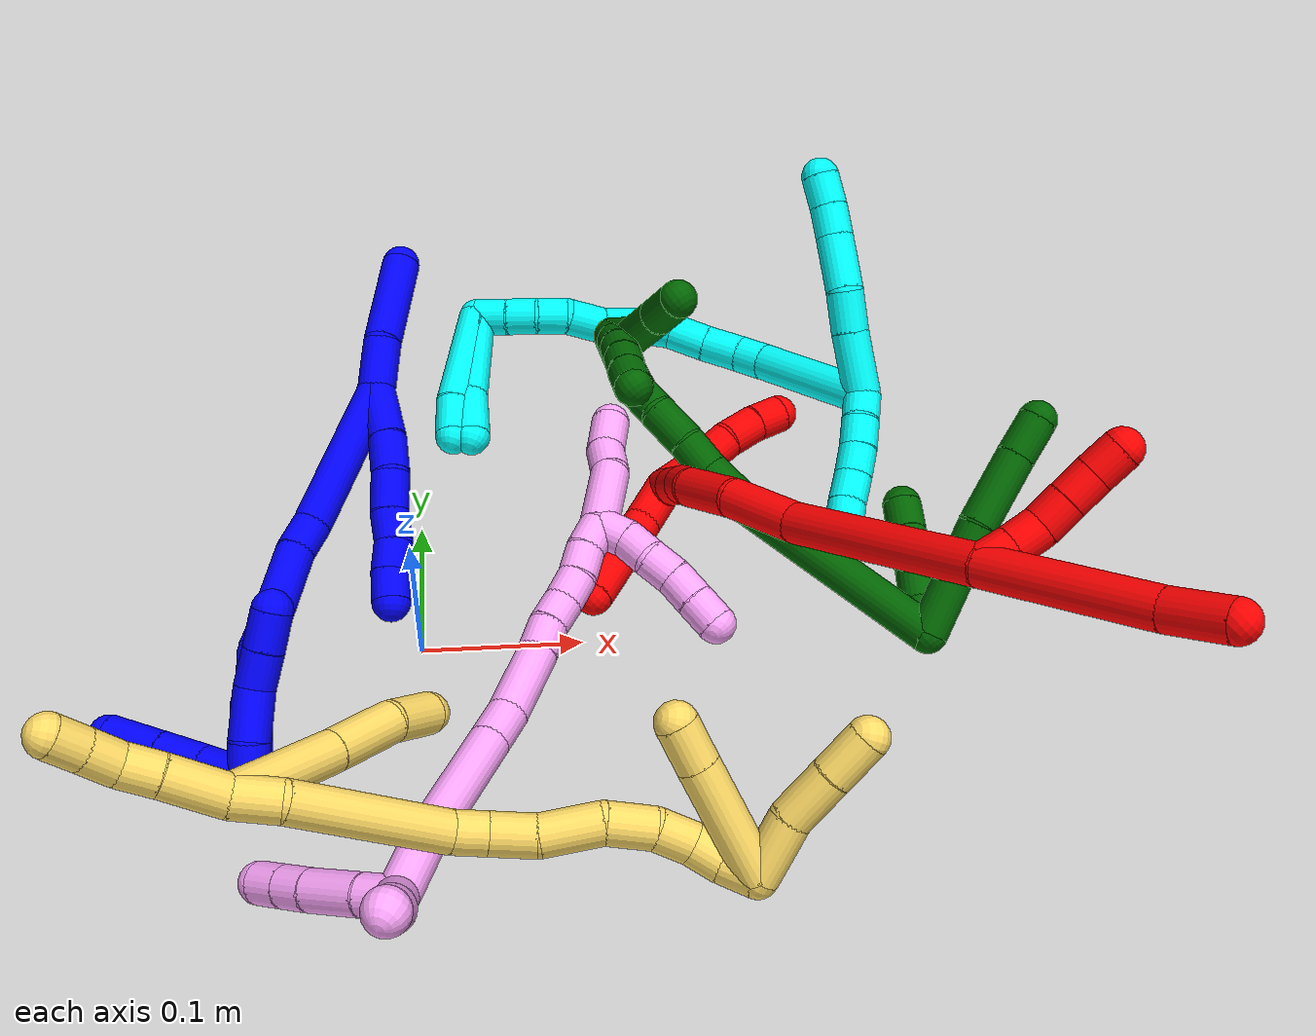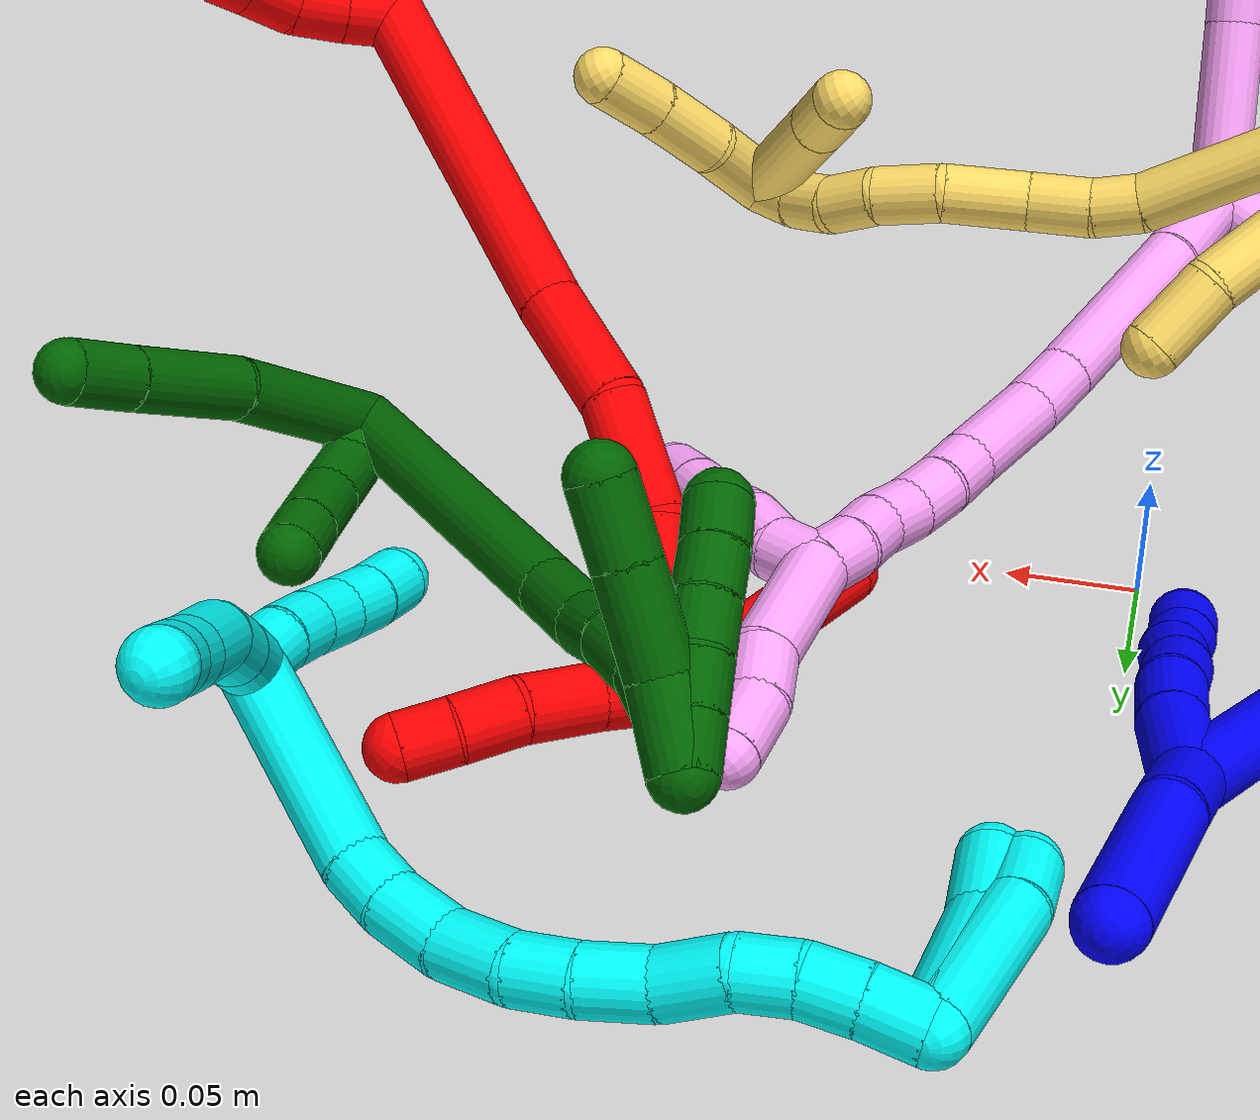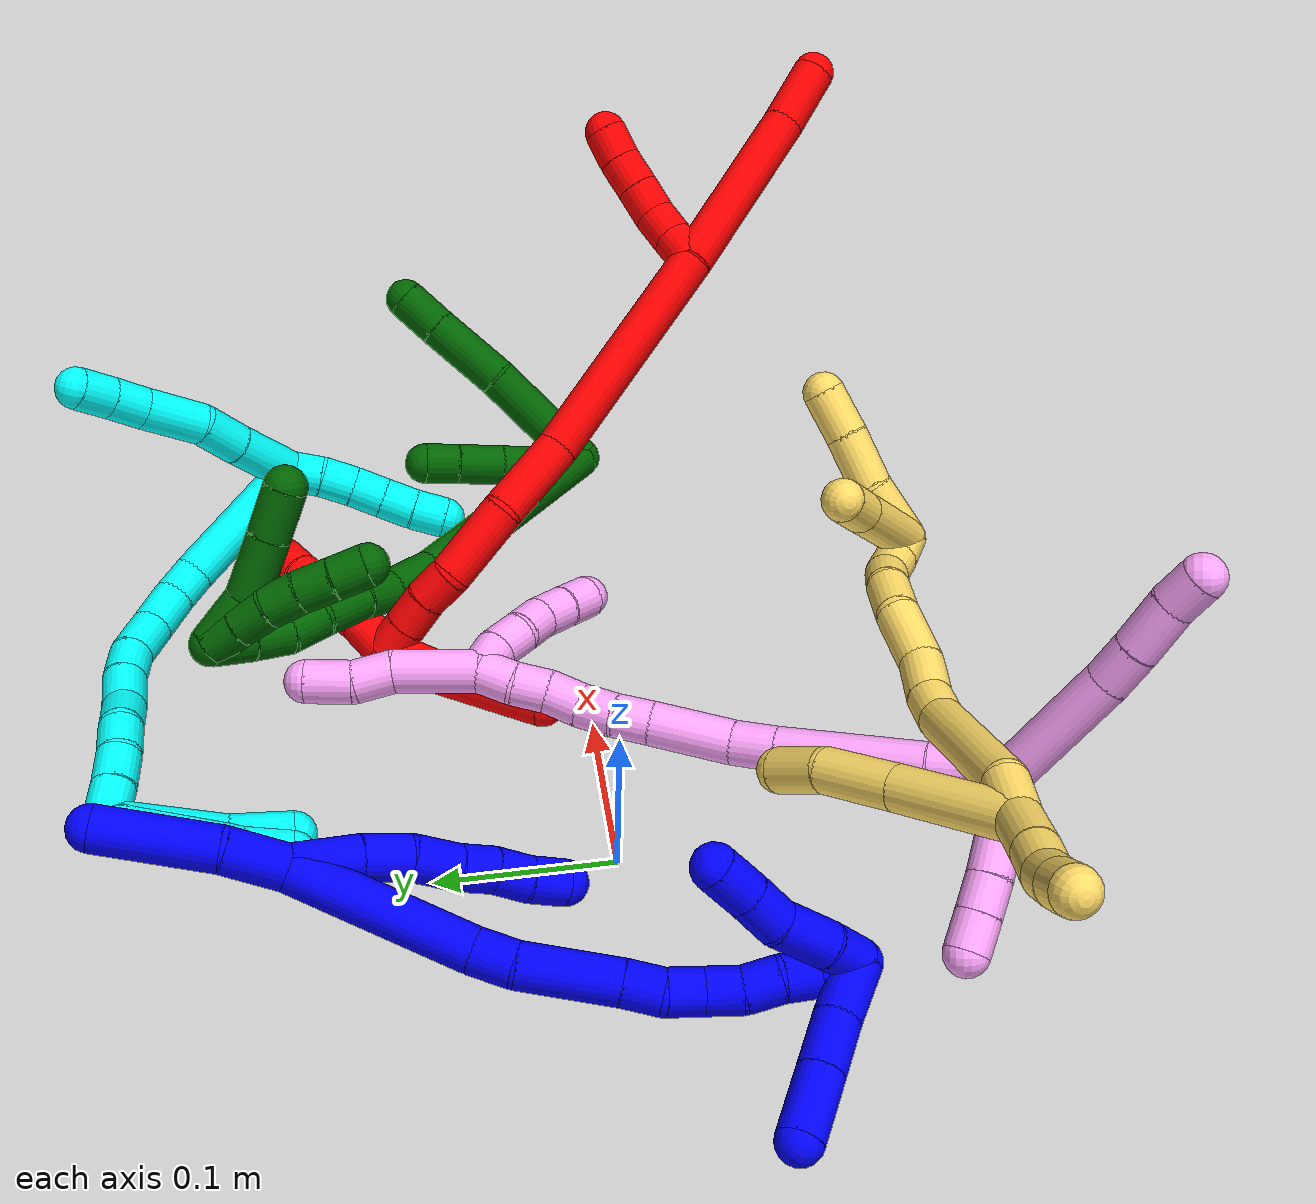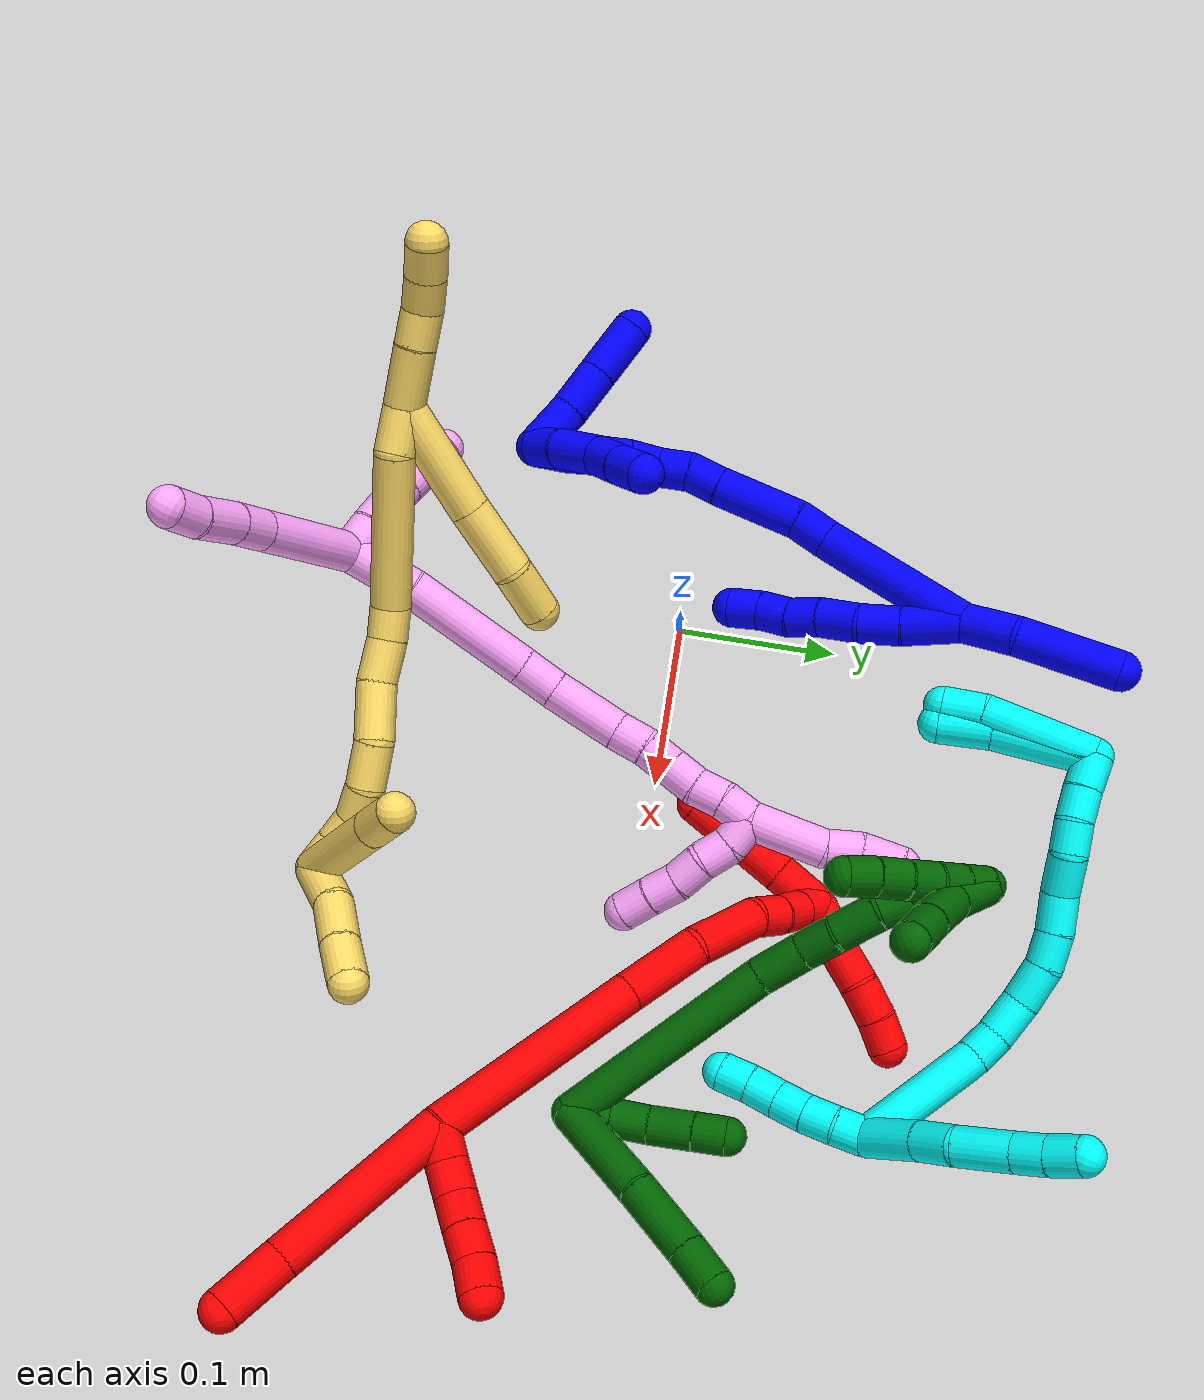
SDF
<sdf version="1.7">
 <world name="default">
  <plugin name="TubeGeneratorPlugin" filename="libtube_generator_plugin.so"/>
  <model name="photoneo_s_sensor">
   <static>1</static>
   <pose>0 0 2 1.57079 1.57079 3.14159</pose>
   <link name="link">
    <inertial><mass>0.1</mass></inertial>
    <sensor name="sensor" type="depth">
     <update_rate>30</update_rate>
     <camera>
      <horizontal_fov>1.22</horizontal_fov>
      <image><width>1920</width><height>1200</height><format>B8G8R8</format></image>
      <clip><near>0.1</near><far>4</far></clip>
      <depth_camera><output>points</output></depth_camera>
     </camera>
     <plugin name="camera_plugin" filename="libgazebo_ros_depth_camera.so">
      <baseline>0.2</baseline>
      <alwaysOn>1</alwaysOn>
      <updateRate>0.0</updateRate>
      <cameraName>camera_ir</cameraName>
      <imageTopicName>/camera/color/image_raw</imageTopicName>
      <cameraInfoTopicName>/camera/color/camera_info</cameraInfoTopicName>
      <depthImageTopicName>/camera/depth/image_raw</depthImageTopicName>
      <depthImageCameraInfoTopicName>/camera/depth/camera_info</depthImageCameraInfoTopicName>
      <pointCloudTopicName>/camera/depth/points</pointCloudTopicName>
      <frameName>fr_optical</frameName>
      <pointCloudCutoff>0.1</pointCloudCutoff>
      <pointCloudCutoffMax>2.0</pointCloudCutoffMax>
      <distortionK1>0</distortionK1>
      <distortionK2>0</distortionK2>
      <distortionK3>0</distortionK3>
      <distortionT1>0</distortionT1>
      <distortionT2>0</distortionT2>
      <CxPrime>0</CxPrime>
      <Cx>0</Cx>
      <Cy>0</Cy>
      <focalLength>0</focalLength>
      <hackBaseline>0</hackBaseline>
     </plugin>
    </sensor>
   </link>
  </model>
  <gravity>0 0 -9.8</gravity>
  <magnetic_field>6e-06 2.3e-05 -4.2e-05</magnetic_field>
  <atmosphere type="adiabatic"/>
  <physics name="default_physics" default="0" type="ode">
   <max_step_size>0.003</max_step_size>
   <real_time_factor>1</real_time_factor>
   <real_time_update_rate>1000</real_time_update_rate>
   <max_contacts>10000</max_contacts>
   <ode>
    <solver>
     <type>quick</type>
     <iters>100</iters>
     <sor>1.3</sor>
     <use_dynamic_moi_rescaling>0</use_dynamic_moi_rescaling>
    </solver>
    <constraints>
     <contact_max_correcting_vel>0</contact_max_correcting_vel>
     <contact_surface_layer>0.001</contact_surface_layer>
     <cfm>0</cfm>
     <erp>0.2</erp>
    </constraints>
   </ode>
  </physics>
  <scene><ambient>0.4 0.4 0.4 1</ambient><background>0.7 0.7 0.7 1</background><shadows>0</shadows></scene>
  <audio><device>default</device></audio>
  <spherical_coordinates>
   <surface_model>EARTH_WGS84</surface_model>
   <latitude_deg>0</latitude_deg>
   <longitude_deg>0</longitude_deg>
   <elevation>0</elevation>
   <heading_deg>0</heading_deg>
  </spherical_coordinates>
  <model name="bin">
   <static>1</static>
   <link name="bottom">
    <collision name="collision-bottom">
     <pose>0 0 -0.01 0 -0 0</pose>
     <geometry><box><size>0.8 0.6 0.02</size></box></geometry>
     <surface>
      <friction><ode><mu>100</mu><mu2>100</mu2></ode></friction>
      <contact><collide_bitmask>65535</collide_bitmask></contact>
     </surface>
    </collision>
   </link>
   <link name="west_wall">
    <collision name="collision-west_wall">
     <pose>-0.41 0 0.1 0 -0 0</pose>
     <geometry><box><size>0.02 0.6 0.2</size></box></geometry>
     <surface>
      <friction><ode><mu>100</mu><mu2>100</mu2></ode></friction>
      <contact><collide_bitmask>65535</collide_bitmask></contact>
     </surface>
    </collision>
   </link>
   <link name="east_wall">
    <collision name="collision-east_wall">
     <pose>0.41 0 0.1 0 -0 0</pose>
     <geometry><box><size>0.02 0.6 0.2</size></box></geometry>
     <surface>
      <friction><ode><mu>100</mu><mu2>100</mu2></ode></friction>
      <contact><collide_bitmask>65535</collide_bitmask></contact>
     </surface>
    </collision>
   </link>
   <link name="south_wall">
    <collision name="collision-south_wall">
     <pose>0 -0.31 0.1 0 -0 0</pose>
     <geometry><box><size>0.8 0.02 0.2</size></box></geometry>
     <surface>
      <friction><ode><mu>100</mu><mu2>100</mu2></ode></friction>
      <contact><collide_bitmask>65535</collide_bitmask></contact>
     </surface>
    </collision>
   </link>
   <link name="north_wall">
    <collision name="collision-north_wall">
     <pose>0 0.31 0.1 0 -0 0</pose>
     <geometry><box><size>0.8 0.02 0.2</size></box></geometry>
     <surface>
      <friction><ode><mu>100</mu><mu2>100</mu2></ode></friction>
      <contact><collide_bitmask>65535</collide_bitmask></contact>
     </surface>
    </collision>
   </link>
  </model>
  <model name="1">
   <static>0</static>
   <link name="1">
    <collision name="collision-cylinder-e_1_2_8">
     <pose>0.006575 -0.00136 -0.017717 3.06496 0.354384 2.71982</pose>
     <geometry><cylinder><radius>0.0125</radius><length>0.037893</length></cylinder></geometry>
     <surface>
      <friction><ode><mu>1.16</mu><mu2>1.16</mu2><slip1>0</slip1><slip2>0</slip2></ode></friction>
      <contact><ode><kp>1e+06</kp><kd>1</kd><max_vel>0</max_vel><min_depth>0.001</min_depth></ode></contact>
     </surface>
    </collision>
    <visual name="visual-cylinder-e_1_2_8">
     <pose>0.006575 -0.00136 -0.017717 3.06496 0.354384 2.71982</pose>
     <geometry><cylinder><radius>0.0125</radius><length>0.037893</length></cylinder></geometry>
     <material><ambient>0 0 1 1</ambient></material>
    </visual>
    <collision name="collision-cylinder-e_2_8_9">
     <pose>0.016116 -0.004175 -0.047985 3.02623 0.230641 2.21671</pose>
     <geometry><cylinder><radius>0.0125</radius><length>0.025958</length></cylinder></geometry>
     <surface>
      <friction><ode><mu>1.16</mu><mu2>1.16</mu2><slip1>0</slip1><slip2>0</slip2></ode></friction>
      <contact><ode><kp>1e+06</kp><kd>1</kd><max_vel>0</max_vel><min_depth>0.001</min_depth></ode></contact>
     </surface>
    </collision>
    <visual name="visual-cylinder-e_2_8_9">
     <pose>0.016116 -0.004175 -0.047985 3.02623 0.230641 2.21671</pose>
     <geometry><cylinder><radius>0.0125</radius><length>0.025958</length></cylinder></geometry>
     <material><ambient>0 0 1 1</ambient></material>
    </visual>
    <collision name="collision-cylinder-e_3_9_10">
     <pose>0.019458 -0.005854 -0.073402 3.12411 0.029086 2.05923</pose>
     <geometry><cylinder><radius>0.0125</radius><length>0.025745</length></cylinder></geometry>
     <surface>
      <friction><ode><mu>1.16</mu><mu2>1.16</mu2><slip1>0</slip1><slip2>0</slip2></ode></friction>
      <contact><ode><kp>1e+06</kp><kd>1</kd><max_vel>0</max_vel><min_depth>0.001</min_depth></ode></contact>
     </surface>
    </collision>
    <visual name="visual-cylinder-e_3_9_10">
     <pose>0.019458 -0.005854 -0.073402 3.12411 0.029086 2.05923</pose>
     <geometry><cylinder><radius>0.0125</radius><length>0.025745</length></cylinder></geometry>
     <material><ambient>0 0 1 1</ambient></material>
    </visual>
    <collision name="collision-cylinder-e_4_10_11">
     <pose>0.0215 -0.005412 -0.096281 -3.07506 0.164712 -2.37512</pose>
     <geometry><cylinder><radius>0.0125</radius><length>0.020349</length></cylinder></geometry>
     <surface>
      <friction><ode><mu>1.16</mu><mu2>1.16</mu2><slip1>0</slip1><slip2>0</slip2></ode></friction>
      <contact><ode><kp>1e+06</kp><kd>1</kd><max_vel>0</max_vel><min_depth>0.001</min_depth></ode></contact>
     </surface>
    </collision>
    <visual name="visual-cylinder-e_4_10_11">
     <pose>0.0215 -0.005412 -0.096281 -3.07506 0.164712 -2.37512</pose>
     <geometry><cylinder><radius>0.0125</radius><length>0.020349</length></cylinder></geometry>
     <material><ambient>0 0 1 1</ambient></material>
    </visual>
    <collision name="collision-cylinder-e_5_11_12">
     <pose>0.022927 -0.00556 -0.116279 3.06006 -0.024073 -0.573949</pose>
     <geometry><cylinder><radius>0.0125</radius><length>0.020038</length></cylinder></geometry>
     <surface>
      <friction><ode><mu>1.16</mu><mu2>1.16</mu2><slip1>0</slip1><slip2>0</slip2></ode></friction>
      <contact><ode><kp>1e+06</kp><kd>1</kd><max_vel>0</max_vel><min_depth>0.001</min_depth></ode></contact>
     </surface>
    </collision>
    <visual name="visual-cylinder-e_5_11_12">
     <pose>0.022927 -0.00556 -0.116279 3.06006 -0.024073 -0.573949</pose>
     <geometry><cylinder><radius>0.0125</radius><length>0.020038</length></cylinder></geometry>
     <material><ambient>0 0 1 1</ambient></material>
    </visual>
    <collision name="collision-cylinder-e_6_12_6">
     <pose>0.024022 -0.006961 -0.136163 3.08262 0.133871 2.31264</pose>
     <geometry><cylinder><radius>0.0125</radius><length>0.020017</length></cylinder></geometry>
     <surface>
      <friction><ode><mu>1.16</mu><mu2>1.16</mu2><slip1>0</slip1><slip2>0</slip2></ode></friction>
      <contact><ode><kp>1e+06</kp><kd>1</kd><max_vel>0</max_vel><min_depth>0.001</min_depth></ode></contact>
     </surface>
    </collision>
    <visual name="visual-cylinder-e_6_12_6">
     <pose>0.024022 -0.006961 -0.136163 3.08262 0.133871 2.31264</pose>
     <geometry><cylinder><radius>0.0125</radius><length>0.020017</length></cylinder></geometry>
     <material><ambient>0 0 1 1</ambient></material>
    </visual>
    <collision name="collision-cylinder-e_1_2_13">
     <pose>0.00074 0.001197 0.017377 -0.068751 0.042487 -0.001461</pose>
     <geometry><cylinder><radius>0.0125</radius><length>0.034867</length></cylinder></geometry>
     <surface>
      <friction><ode><mu>1.16</mu><mu2>1.16</mu2><slip1>0</slip1><slip2>0</slip2></ode></friction>
      <contact><ode><kp>1e+06</kp><kd>1</kd><max_vel>0</max_vel><min_depth>0.001</min_depth></ode></contact>
     </surface>
    </collision>
    <visual name="visual-cylinder-e_1_2_13">
     <pose>0.00074 0.001197 0.017377 -0.068751 0.042487 -0.001461</pose>
     <geometry><cylinder><radius>0.0125</radius><length>0.034867</length></cylinder></geometry>
     <material><ambient>0 0 1 1</ambient></material>
    </visual>
    <collision name="collision-cylinder-e_2_13_5">
     <pose>0.000281 0.011952 0.065862 -0.29812 -0.036841 0.005533</pose>
     <geometry><cylinder><radius>0.0125</radius><length>0.065133</length></cylinder></geometry>
     <surface>
      <friction><ode><mu>1.16</mu><mu2>1.16</mu2><slip1>0</slip1><slip2>0</slip2></ode></friction>
      <contact><ode><kp>1e+06</kp><kd>1</kd><max_vel>0</max_vel><min_depth>0.001</min_depth></ode></contact>
     </surface>
    </collision>
    <visual name="visual-cylinder-e_2_13_5">
     <pose>0.000281 0.011952 0.065862 -0.29812 -0.036841 0.005533</pose>
     <geometry><cylinder><radius>0.0125</radius><length>0.065133</length></cylinder></geometry>
     <material><ambient>0 0 1 1</ambient></material>
    </visual>
    <collision name="collision-cylinder-e_1_2_14">
     <pose>-0.011248 -0.015532 -0.047216 2.82379 -0.222553 -1.21778</pose>
     <geometry><cylinder><radius>0.0125</radius><length>0.101923</length></cylinder></geometry>
     <surface>
      <friction><ode><mu>1.16</mu><mu2>1.16</mu2><slip1>0</slip1><slip2>0</slip2></ode></friction>
      <contact><ode><kp>1e+06</kp><kd>1</kd><max_vel>0</max_vel><min_depth>0.001</min_depth></ode></contact>
     </surface>
    </collision>
    <visual name="visual-cylinder-e_1_2_14">
     <pose>-0.011248 -0.015532 -0.047216 2.82379 -0.222553 -1.21778</pose>
     <geometry><cylinder><radius>0.0125</radius><length>0.101923</length></cylinder></geometry>
     <material><ambient>0 0 1 1</ambient></material>
    </visual>
    <collision name="collision-cylinder-e_2_14_15">
     <pose>-0.024251 -0.036373 -0.104368 2.65081 -0.154476 -0.599437</pose>
     <geometry><cylinder><radius>0.0125</radius><length>0.022806</length></cylinder></geometry>
     <surface>
      <friction><ode><mu>1.16</mu><mu2>1.16</mu2><slip1>0</slip1><slip2>0</slip2></ode></friction>
      <contact><ode><kp>1e+06</kp><kd>1</kd><max_vel>0</max_vel><min_depth>0.001</min_depth></ode></contact>
     </surface>
    </collision>
    <visual name="visual-cylinder-e_2_14_15">
     <pose>-0.024251 -0.036373 -0.104368 2.65081 -0.154476 -0.599437</pose>
     <geometry><cylinder><radius>0.0125</radius><length>0.022806</length></cylinder></geometry>
     <material><ambient>0 0 1 1</ambient></material>
    </visual>
    <collision name="collision-cylinder-e_3_15_16">
     <pose>-0.025507 -0.052169 -0.139265 2.74387 0.018422 0.091351</pose>
     <geometry><cylinder><radius>0.0125</radius><length>0.054155</length></cylinder></geometry>
     <surface>
      <friction><ode><mu>1.16</mu><mu2>1.16</mu2><slip1>0</slip1><slip2>0</slip2></ode></friction>
      <contact><ode><kp>1e+06</kp><kd>1</kd><max_vel>0</max_vel><min_depth>0.001</min_depth></ode></contact>
     </surface>
    </collision>
    <visual name="visual-cylinder-e_3_15_16">
     <pose>-0.025507 -0.052169 -0.139265 2.74387 0.018422 0.091351</pose>
     <geometry><cylinder><radius>0.0125</radius><length>0.054155</length></cylinder></geometry>
     <material><ambient>0 0 1 1</ambient></material>
    </visual>
    <collision name="collision-cylinder-e_4_16_17">
     <pose>-0.025484 -0.066839 -0.173775 2.72872 -0.045625 -0.217044</pose>
     <geometry><cylinder><radius>0.0125</radius><length>0.020875</length></cylinder></geometry>
     <surface>
      <friction><ode><mu>1.16</mu><mu2>1.16</mu2><slip1>0</slip1><slip2>0</slip2></ode></friction>
      <contact><ode><kp>1e+06</kp><kd>1</kd><max_vel>0</max_vel><min_depth>0.001</min_depth></ode></contact>
     </surface>
    </collision>
    <visual name="visual-cylinder-e_4_16_17">
     <pose>-0.025484 -0.066839 -0.173775 2.72872 -0.045625 -0.217044</pose>
     <geometry><cylinder><radius>0.0125</radius><length>0.020875</length></cylinder></geometry>
     <material><ambient>0 0 1 1</ambient></material>
    </visual>
    <collision name="collision-cylinder-e_5_17_18">
     <pose>-0.023749 -0.073414 -0.192864 2.89592 0.221193 1.46508</pose>
     <geometry><cylinder><radius>0.0125</radius><length>0.020157</length></cylinder></geometry>
     <surface>
      <friction><ode><mu>1.16</mu><mu2>1.16</mu2><slip1>0</slip1><slip2>0</slip2></ode></friction>
      <contact><ode><kp>1e+06</kp><kd>1</kd><max_vel>0</max_vel><min_depth>0.001</min_depth></ode></contact>
     </surface>
    </collision>
    <visual name="visual-cylinder-e_5_17_18">
     <pose>-0.023749 -0.073414 -0.192864 2.89592 0.221193 1.46508</pose>
     <geometry><cylinder><radius>0.0125</radius><length>0.020157</length></cylinder></geometry>
     <material><ambient>0 0 1 1</ambient></material>
    </visual>
    <collision name="collision-cylinder-e_6_18_19">
     <pose>-0.019508 -0.079798 -0.21136 2.72237 0.204044 0.897066</pose>
     <geometry><cylinder><radius>0.0125</radius><length>0.020032</length></cylinder></geometry>
     <surface>
      <friction><ode><mu>1.16</mu><mu2>1.16</mu2><slip1>0</slip1><slip2>0</slip2></ode></friction>
      <contact><ode><kp>1e+06</kp><kd>1</kd><max_vel>0</max_vel><min_depth>0.001</min_depth></ode></contact>
     </surface>
    </collision>
    <visual name="visual-cylinder-e_6_18_19">
     <pose>-0.019508 -0.079798 -0.21136 2.72237 0.204044 0.897066</pose>
     <geometry><cylinder><radius>0.0125</radius><length>0.020032</length></cylinder></geometry>
     <material><ambient>0 0 1 1</ambient></material>
    </visual>
    <collision name="collision-cylinder-e_7_19_20">
     <pose>-0.013048 -0.088067 -0.228213 2.64507 0.458371 1.48782</pose>
     <geometry><cylinder><radius>0.0125</radius><length>0.020023</length></cylinder></geometry>
     <surface>
      <friction><ode><mu>1.16</mu><mu2>1.16</mu2><slip1>0</slip1><slip2>0</slip2></ode></friction>
      <contact><ode><kp>1e+06</kp><kd>1</kd><max_vel>0</max_vel><min_depth>0.001</min_depth></ode></contact>
     </surface>
    </collision>
    <visual name="visual-cylinder-e_7_19_20">
     <pose>-0.013048 -0.088067 -0.228213 2.64507 0.458371 1.48782</pose>
     <geometry><cylinder><radius>0.0125</radius><length>0.020023</length></cylinder></geometry>
     <material><ambient>0 0 1 1</ambient></material>
    </visual>
    <collision name="collision-cylinder-e_8_20_21">
     <pose>-0.005304 -0.094934 -0.245181 2.86357 0.337809 1.76738</pose>
     <geometry><cylinder><radius>0.0125</radius><length>0.020003</length></cylinder></geometry>
     <surface>
      <friction><ode><mu>1.16</mu><mu2>1.16</mu2><slip1>0</slip1><slip2>0</slip2></ode></friction>
      <contact><ode><kp>1e+06</kp><kd>1</kd><max_vel>0</max_vel><min_depth>0.001</min_depth></ode></contact>
     </surface>
    </collision>
    <visual name="visual-cylinder-e_8_20_21">
     <pose>-0.005304 -0.094934 -0.245181 2.86357 0.337809 1.76738</pose>
     <geometry><cylinder><radius>0.0125</radius><length>0.020003</length></cylinder></geometry>
     <material><ambient>0 0 1 1</ambient></material>
    </visual>
    <collision name="collision-cylinder-e_9_21_1">
     <pose>0.002205 -0.102726 -0.261712 2.53248 0.43222 1.21932</pose>
     <geometry><cylinder><radius>0.0125</radius><length>0.020026</length></cylinder></geometry>
     <surface>
      <friction><ode><mu>1.16</mu><mu2>1.16</mu2><slip1>0</slip1><slip2>0</slip2></ode></friction>
      <contact><ode><kp>1e+06</kp><kd>1</kd><max_vel>0</max_vel><min_depth>0.001</min_depth></ode></contact>
     </surface>
    </collision>
    <visual name="visual-cylinder-e_9_21_1">
     <pose>0.002205 -0.102726 -0.261712 2.53248 0.43222 1.21932</pose>
     <geometry><cylinder><radius>0.0125</radius><length>0.020026</length></cylinder></geometry>
     <material><ambient>0 0 1 1</ambient></material>
    </visual>
    <collision name="collision-cylinder-e_1_1_22">
     <pose>-0.008772 -0.110297 -0.264132 0.439613 -1.21917 -0.309527</pose>
     <geometry><cylinder><radius>0.0125</radius><length>0.03232</length></cylinder></geometry>
     <surface>
      <friction><ode><mu>1.16</mu><mu2>1.16</mu2><slip1>0</slip1><slip2>0</slip2></ode></friction>
      <contact><ode><kp>1e+06</kp><kd>1</kd><max_vel>0</max_vel><min_depth>0.001</min_depth></ode></contact>
     </surface>
    </collision>
    <visual name="visual-cylinder-e_1_1_22">
     <pose>-0.008772 -0.110297 -0.264132 0.439613 -1.21917 -0.309527</pose>
     <geometry><cylinder><radius>0.0125</radius><length>0.03232</length></cylinder></geometry>
     <material><ambient>0 0 1 1</ambient></material>
    </visual>
    <collision name="collision-cylinder-e_2_22_23">
     <pose>-0.037955 -0.11662 -0.254485 0.708927 -1.16174 -0.476638</pose>
     <geometry><cylinder><radius>0.0125</radius><length>0.030543</length></cylinder></geometry>
     <surface>
      <friction><ode><mu>1.16</mu><mu2>1.16</mu2><slip1>0</slip1><slip2>0</slip2></ode></friction>
      <contact><ode><kp>1e+06</kp><kd>1</kd><max_vel>0</max_vel><min_depth>0.001</min_depth></ode></contact>
     </surface>
    </collision>
    <visual name="visual-cylinder-e_2_22_23">
     <pose>-0.037955 -0.11662 -0.254485 0.708927 -1.16174 -0.476638</pose>
     <geometry><cylinder><radius>0.0125</radius><length>0.030543</length></cylinder></geometry>
     <material><ambient>0 0 1 1</ambient></material>
    </visual>
    <collision name="collision-cylinder-e_3_23_4">
     <pose>-0.069046 -0.125242 -0.244284 0.695706 -1.16773 -0.470278</pose>
     <geometry><cylinder><radius>0.0125</radius><length>0.037137</length></cylinder></geometry>
     <surface>
      <friction><ode><mu>1.16</mu><mu2>1.16</mu2><slip1>0</slip1><slip2>0</slip2></ode></friction>
      <contact><ode><kp>1e+06</kp><kd>1</kd><max_vel>0</max_vel><min_depth>0.001</min_depth></ode></contact>
     </surface>
    </collision>
    <visual name="visual-cylinder-e_3_23_4">
     <pose>-0.069046 -0.125242 -0.244284 0.695706 -1.16773 -0.470278</pose>
     <geometry><cylinder><radius>0.0125</radius><length>0.037137</length></cylinder></geometry>
     <material><ambient>0 0 1 1</ambient></material>
    </visual>
    <collision name="collision-cylinder-e_1_1_24">
     <pose>0.008171 -0.110596 -0.25846 0.244172 0.159116 0.019564</pose>
     <geometry><cylinder><radius>0.0125</radius><length>0.022356</length></cylinder></geometry>
     <surface>
      <friction><ode><mu>1.16</mu><mu2>1.16</mu2><slip1>0</slip1><slip2>0</slip2></ode></friction>
      <contact><ode><kp>1e+06</kp><kd>1</kd><max_vel>0</max_vel><min_depth>0.001</min_depth></ode></contact>
     </surface>
    </collision>
    <visual name="visual-cylinder-e_1_1_24">
     <pose>0.008171 -0.110596 -0.25846 0.244172 0.159116 0.019564</pose>
     <geometry><cylinder><radius>0.0125</radius><length>0.022356</length></cylinder></geometry>
     <material><ambient>0 0 1 1</ambient></material>
    </visual>
    <collision name="collision-cylinder-e_2_24_25">
     <pose>0.012051 -0.114559 -0.232332 0.083784 0.135482 0.005688</pose>
     <geometry><cylinder><radius>0.0125</radius><length>0.031232</length></cylinder></geometry>
     <surface>
      <friction><ode><mu>1.16</mu><mu2>1.16</mu2><slip1>0</slip1><slip2>0</slip2></ode></friction>
      <contact><ode><kp>1e+06</kp><kd>1</kd><max_vel>0</max_vel><min_depth>0.001</min_depth></ode></contact>
     </surface>
    </collision>
    <visual name="visual-cylinder-e_2_24_25">
     <pose>0.012051 -0.114559 -0.232332 0.083784 0.135482 0.005688</pose>
     <geometry><cylinder><radius>0.0125</radius><length>0.031232</length></cylinder></geometry>
     <material><ambient>0 0 1 1</ambient></material>
    </visual>
    <collision name="collision-cylinder-e_3_25_26">
     <pose>0.018641 -0.117805 -0.206556 0.186197 0.401937 0.038037</pose>
     <geometry><cylinder><radius>0.0125</radius><length>0.022906</length></cylinder></geometry>
     <surface>
      <friction><ode><mu>1.16</mu><mu2>1.16</mu2><slip1>0</slip1><slip2>0</slip2></ode></friction>
      <contact><ode><kp>1e+06</kp><kd>1</kd><max_vel>0</max_vel><min_depth>0.001</min_depth></ode></contact>
     </surface>
    </collision>
    <visual name="visual-cylinder-e_3_25_26">
     <pose>0.018641 -0.117805 -0.206556 0.186197 0.401937 0.038037</pose>
     <geometry><cylinder><radius>0.0125</radius><length>0.022906</length></cylinder></geometry>
     <material><ambient>0 0 1 1</ambient></material>
    </visual>
    <collision name="collision-cylinder-e_4_26_3">
     <pose>0.027261 -0.121741 -0.185378 0.181371 0.359988 0.033091</pose>
     <geometry><cylinder><radius>0.0125</radius><length>0.023507</length></cylinder></geometry>
     <surface>
      <friction><ode><mu>1.16</mu><mu2>1.16</mu2><slip1>0</slip1><slip2>0</slip2></ode></friction>
      <contact><ode><kp>1e+06</kp><kd>1</kd><max_vel>0</max_vel><min_depth>0.001</min_depth></ode></contact>
     </surface>
    </collision>
    <visual name="visual-cylinder-e_4_26_3">
     <pose>0.027261 -0.121741 -0.185378 0.181371 0.359988 0.033091</pose>
     <geometry><cylinder><radius>0.0125</radius><length>0.023507</length></cylinder></geometry>
     <material><ambient>0 0 1 1</ambient></material>
    </visual>
    <collision name="collision-sphere-3">
     <pose>0.031402 -0.123725 -0.174559 0 -0 0</pose>
     <geometry><sphere><radius>0.0125</radius></sphere></geometry>
     <surface>
      <friction><ode><mu>1.16</mu><mu2>1.16</mu2><slip1>0</slip1><slip2>0</slip2></ode></friction>
      <contact><ode><kp>1e+06</kp><kd>1</kd><max_vel>0</max_vel><min_depth>0.001</min_depth></ode></contact>
     </surface>
    </collision>
    <visual name="visual-sphere-3">
     <pose>0.031402 -0.123725 -0.174559 0 -0 0</pose>
     <geometry><sphere><radius>0.0125</radius></sphere></geometry>
     <material><ambient>0 0 1 1</ambient></material>
    </visual>
    <collision name="collision-sphere-26">
     <pose>0.023121 -0.119756 -0.196198 0 -0 0</pose>
     <geometry><sphere><radius>0.0125</radius></sphere></geometry>
     <surface>
      <friction><ode><mu>1.16</mu><mu2>1.16</mu2><slip1>0</slip1><slip2>0</slip2></ode></friction>
      <contact><ode><kp>1e+06</kp><kd>1</kd><max_vel>0</max_vel><min_depth>0.001</min_depth></ode></contact>
     </surface>
    </collision>
    <visual name="visual-sphere-26">
     <pose>0.023121 -0.119756 -0.196198 0 -0 0</pose>
     <geometry><sphere><radius>0.0125</radius></sphere></geometry>
     <material><ambient>0 0 1 1</ambient></material>
    </visual>
    <collision name="collision-sphere-25">
     <pose>0.01416 -0.115854 -0.216914 0 -0 0</pose>
     <geometry><sphere><radius>0.0125</radius></sphere></geometry>
     <surface>
      <friction><ode><mu>1.16</mu><mu2>1.16</mu2><slip1>0</slip1><slip2>0</slip2></ode></friction>
      <contact><ode><kp>1e+06</kp><kd>1</kd><max_vel>0</max_vel><min_depth>0.001</min_depth></ode></contact>
     </surface>
    </collision>
    <visual name="visual-sphere-25">
     <pose>0.01416 -0.115854 -0.216914 0 -0 0</pose>
     <geometry><sphere><radius>0.0125</radius></sphere></geometry>
     <material><ambient>0 0 1 1</ambient></material>
    </visual>
    <collision name="collision-sphere-24">
     <pose>0.009942 -0.113264 -0.247751 0 -0 0</pose>
     <geometry><sphere><radius>0.0125</radius></sphere></geometry>
     <surface>
      <friction><ode><mu>1.16</mu><mu2>1.16</mu2><slip1>0</slip1><slip2>0</slip2></ode></friction>
      <contact><ode><kp>1e+06</kp><kd>1</kd><max_vel>0</max_vel><min_depth>0.001</min_depth></ode></contact>
     </surface>
    </collision>
    <visual name="visual-sphere-24">
     <pose>0.009942 -0.113264 -0.247751 0 -0 0</pose>
     <geometry><sphere><radius>0.0125</radius></sphere></geometry>
     <material><ambient>0 0 1 1</ambient></material>
    </visual>
    <collision name="collision-sphere-4">
     <pose>-0.086127 -0.12991 -0.238693 0 -0 0</pose>
     <geometry><sphere><radius>0.0125</radius></sphere></geometry>
     <surface>
      <friction><ode><mu>1.16</mu><mu2>1.16</mu2><slip1>0</slip1><slip2>0</slip2></ode></friction>
      <contact><ode><kp>1e+06</kp><kd>1</kd><max_vel>0</max_vel><min_depth>0.001</min_depth></ode></contact>
     </surface>
    </collision>
    <visual name="visual-sphere-4">
     <pose>-0.086127 -0.12991 -0.238693 0 -0 0</pose>
     <geometry><sphere><radius>0.0125</radius></sphere></geometry>
     <material><ambient>0 0 1 1</ambient></material>
    </visual>
    <collision name="collision-sphere-23">
     <pose>-0.051966 -0.120574 -0.249874 0 -0 0</pose>
     <geometry><sphere><radius>0.0125</radius></sphere></geometry>
     <surface>
      <friction><ode><mu>1.16</mu><mu2>1.16</mu2><slip1>0</slip1><slip2>0</slip2></ode></friction>
      <contact><ode><kp>1e+06</kp><kd>1</kd><max_vel>0</max_vel><min_depth>0.001</min_depth></ode></contact>
     </surface>
    </collision>
    <visual name="visual-sphere-23">
     <pose>-0.051966 -0.120574 -0.249874 0 -0 0</pose>
     <geometry><sphere><radius>0.0125</radius></sphere></geometry>
     <material><ambient>0 0 1 1</ambient></material>
    </visual>
    <collision name="collision-sphere-22">
     <pose>-0.023943 -0.112666 -0.259096 0 -0 0</pose>
     <geometry><sphere><radius>0.0125</radius></sphere></geometry>
     <surface>
      <friction><ode><mu>1.16</mu><mu2>1.16</mu2><slip1>0</slip1><slip2>0</slip2></ode></friction>
      <contact><ode><kp>1e+06</kp><kd>1</kd><max_vel>0</max_vel><min_depth>0.001</min_depth></ode></contact>
     </surface>
    </collision>
    <visual name="visual-sphere-22">
     <pose>-0.023943 -0.112666 -0.259096 0 -0 0</pose>
     <geometry><sphere><radius>0.0125</radius></sphere></geometry>
     <material><ambient>0 0 1 1</ambient></material>
    </visual>
    <collision name="collision-sphere-1">
     <pose>0.0064 -0.107928 -0.269169 0 -0 0</pose>
     <geometry><sphere><radius>0.0125</radius></sphere></geometry>
     <surface>
      <friction><ode><mu>1.16</mu><mu2>1.16</mu2><slip1>0</slip1><slip2>0</slip2></ode></friction>
      <contact><ode><kp>1e+06</kp><kd>1</kd><max_vel>0</max_vel><min_depth>0.001</min_depth></ode></contact>
     </surface>
    </collision>
    <visual name="visual-sphere-1">
     <pose>0.0064 -0.107928 -0.269169 0 -0 0</pose>
     <geometry><sphere><radius>0.0125</radius></sphere></geometry>
     <material><ambient>0 0 1 1</ambient></material>
    </visual>
    <collision name="collision-sphere-21">
     <pose>-0.001989 -0.097524 -0.254255 0 -0 0</pose>
     <geometry><sphere><radius>0.0125</radius></sphere></geometry>
     <surface>
      <friction><ode><mu>1.16</mu><mu2>1.16</mu2><slip1>0</slip1><slip2>0</slip2></ode></friction>
      <contact><ode><kp>1e+06</kp><kd>1</kd><max_vel>0</max_vel><min_depth>0.001</min_depth></ode></contact>
     </surface>
    </collision>
    <visual name="visual-sphere-21">
     <pose>-0.001989 -0.097524 -0.254255 0 -0 0</pose>
     <geometry><sphere><radius>0.0125</radius></sphere></geometry>
     <material><ambient>0 0 1 1</ambient></material>
    </visual>
    <collision name="collision-sphere-12">
     <pose>0.022686 -0.006376 -0.126262 0 -0 0</pose>
     <geometry><sphere><radius>0.0125</radius></sphere></geometry>
     <surface>
      <friction><ode><mu>1.16</mu><mu2>1.16</mu2><slip1>0</slip1><slip2>0</slip2></ode></friction>
      <contact><ode><kp>1e+06</kp><kd>1</kd><max_vel>0</max_vel><min_depth>0.001</min_depth></ode></contact>
     </surface>
    </collision>
    <visual name="visual-sphere-12">
     <pose>0.022686 -0.006376 -0.126262 0 -0 0</pose>
     <geometry><sphere><radius>0.0125</radius></sphere></geometry>
     <material><ambient>0 0 1 1</ambient></material>
    </visual>
    <collision name="collision-sphere-11">
     <pose>0.023169 -0.004745 -0.106296 0 -0 0</pose>
     <geometry><sphere><radius>0.0125</radius></sphere></geometry>
     <surface>
      <friction><ode><mu>1.16</mu><mu2>1.16</mu2><slip1>0</slip1><slip2>0</slip2></ode></friction>
      <contact><ode><kp>1e+06</kp><kd>1</kd><max_vel>0</max_vel><min_depth>0.001</min_depth></ode></contact>
     </surface>
    </collision>
    <visual name="visual-sphere-11">
     <pose>0.023169 -0.004745 -0.106296 0 -0 0</pose>
     <geometry><sphere><radius>0.0125</radius></sphere></geometry>
     <material><ambient>0 0 1 1</ambient></material>
    </visual>
    <collision name="collision-sphere-10">
     <pose>0.019832 -0.006079 -0.086267 0 -0 0</pose>
     <geometry><sphere><radius>0.0125</radius></sphere></geometry>
     <surface>
      <friction><ode><mu>1.16</mu><mu2>1.16</mu2><slip1>0</slip1><slip2>0</slip2></ode></friction>
      <contact><ode><kp>1e+06</kp><kd>1</kd><max_vel>0</max_vel><min_depth>0.001</min_depth></ode></contact>
     </surface>
    </collision>
    <visual name="visual-sphere-10">
     <pose>0.019832 -0.006079 -0.086267 0 -0 0</pose>
     <geometry><sphere><radius>0.0125</radius></sphere></geometry>
     <material><ambient>0 0 1 1</ambient></material>
    </visual>
    <collision name="collision-sphere-9">
     <pose>0.019083 -0.005629 -0.060536 0 -0 0</pose>
     <geometry><sphere><radius>0.0125</radius></sphere></geometry>
     <surface>
      <friction><ode><mu>1.16</mu><mu2>1.16</mu2><slip1>0</slip1><slip2>0</slip2></ode></friction>
      <contact><ode><kp>1e+06</kp><kd>1</kd><max_vel>0</max_vel><min_depth>0.001</min_depth></ode></contact>
     </surface>
    </collision>
    <visual name="visual-sphere-9">
     <pose>0.019083 -0.005629 -0.060536 0 -0 0</pose>
     <geometry><sphere><radius>0.0125</radius></sphere></geometry>
     <material><ambient>0 0 1 1</ambient></material>
    </visual>
    <collision name="collision-sphere-2">
     <geometry><sphere><radius>0.0125</radius></sphere></geometry>
     <surface>
      <friction><ode><mu>1.16</mu><mu2>1.16</mu2><slip1>0</slip1><slip2>0</slip2></ode></friction>
      <contact><ode><kp>1e+06</kp><kd>1</kd><max_vel>0</max_vel><min_depth>0.001</min_depth></ode></contact>
     </surface>
    </collision>
    <visual name="visual-sphere-2">
     <geometry><sphere><radius>0.0125</radius></sphere></geometry>
     <material><ambient>0 0 1 1</ambient></material>
    </visual>
    <collision name="collision-sphere-19">
     <pose>-0.017478 -0.08379 -0.220319 0 -0 0</pose>
     <geometry><sphere><radius>0.0125</radius></sphere></geometry>
     <surface>
      <friction><ode><mu>1.16</mu><mu2>1.16</mu2><slip1>0</slip1><slip2>0</slip2></ode></friction>
      <contact><ode><kp>1e+06</kp><kd>1</kd><max_vel>0</max_vel><min_depth>0.001</min_depth></ode></contact>
     </surface>
    </collision>
    <visual name="visual-sphere-19">
     <pose>-0.017478 -0.08379 -0.220319 0 -0 0</pose>
     <geometry><sphere><radius>0.0125</radius></sphere></geometry>
     <material><ambient>0 0 1 1</ambient></material>
    </visual>
    <collision name="collision-sphere-8">
     <pose>0.013149 -0.002721 -0.035434 0 -0 0</pose>
     <geometry><sphere><radius>0.0125</radius></sphere></geometry>
     <surface>
      <friction><ode><mu>1.16</mu><mu2>1.16</mu2><slip1>0</slip1><slip2>0</slip2></ode></friction>
      <contact><ode><kp>1e+06</kp><kd>1</kd><max_vel>0</max_vel><min_depth>0.001</min_depth></ode></contact>
     </surface>
    </collision>
    <visual name="visual-sphere-8">
     <pose>0.013149 -0.002721 -0.035434 0 -0 0</pose>
     <geometry><sphere><radius>0.0125</radius></sphere></geometry>
     <material><ambient>0 0 1 1</ambient></material>
    </visual>
    <collision name="collision-sphere-6">
     <pose>0.025358 -0.007545 -0.146065 0 -0 0</pose>
     <geometry><sphere><radius>0.0125</radius></sphere></geometry>
     <surface>
      <friction><ode><mu>1.16</mu><mu2>1.16</mu2><slip1>0</slip1><slip2>0</slip2></ode></friction>
      <contact><ode><kp>1e+06</kp><kd>1</kd><max_vel>0</max_vel><min_depth>0.001</min_depth></ode></contact>
     </surface>
    </collision>
    <visual name="visual-sphere-6">
     <pose>0.025358 -0.007545 -0.146065 0 -0 0</pose>
     <geometry><sphere><radius>0.0125</radius></sphere></geometry>
     <material><ambient>0 0 1 1</ambient></material>
    </visual>
    <collision name="collision-sphere-13">
     <pose>0.001481 0.002393 0.034753 0 -0 0</pose>
     <geometry><sphere><radius>0.0125</radius></sphere></geometry>
     <surface>
      <friction><ode><mu>1.16</mu><mu2>1.16</mu2><slip1>0</slip1><slip2>0</slip2></ode></friction>
      <contact><ode><kp>1e+06</kp><kd>1</kd><max_vel>0</max_vel><min_depth>0.001</min_depth></ode></contact>
     </surface>
    </collision>
    <visual name="visual-sphere-13">
     <pose>0.001481 0.002393 0.034753 0 -0 0</pose>
     <geometry><sphere><radius>0.0125</radius></sphere></geometry>
     <material><ambient>0 0 1 1</ambient></material>
    </visual>
    <collision name="collision-sphere-5">
     <pose>-0.000918 0.021511 0.096971 0 -0 0</pose>
     <geometry><sphere><radius>0.0125</radius></sphere></geometry>
     <surface>
      <friction><ode><mu>1.16</mu><mu2>1.16</mu2><slip1>0</slip1><slip2>0</slip2></ode></friction>
      <contact><ode><kp>1e+06</kp><kd>1</kd><max_vel>0</max_vel><min_depth>0.001</min_depth></ode></contact>
     </surface>
    </collision>
    <visual name="visual-sphere-5">
     <pose>-0.000918 0.021511 0.096971 0 -0 0</pose>
     <geometry><sphere><radius>0.0125</radius></sphere></geometry>
     <material><ambient>0 0 1 1</ambient></material>
    </visual>
    <collision name="collision-sphere-14">
     <pose>-0.022496 -0.031063 -0.094431 0 -0 0</pose>
     <geometry><sphere><radius>0.0125</radius></sphere></geometry>
     <surface>
      <friction><ode><mu>1.16</mu><mu2>1.16</mu2><slip1>0</slip1><slip2>0</slip2></ode></friction>
      <contact><ode><kp>1e+06</kp><kd>1</kd><max_vel>0</max_vel><min_depth>0.001</min_depth></ode></contact>
     </surface>
    </collision>
    <visual name="visual-sphere-14">
     <pose>-0.022496 -0.031063 -0.094431 0 -0 0</pose>
     <geometry><sphere><radius>0.0125</radius></sphere></geometry>
     <material><ambient>0 0 1 1</ambient></material>
    </visual>
    <collision name="collision-sphere-15">
     <pose>-0.026005 -0.041684 -0.114305 0 -0 0</pose>
     <geometry><sphere><radius>0.0125</radius></sphere></geometry>
     <surface>
      <friction><ode><mu>1.16</mu><mu2>1.16</mu2><slip1>0</slip1><slip2>0</slip2></ode></friction>
      <contact><ode><kp>1e+06</kp><kd>1</kd><max_vel>0</max_vel><min_depth>0.001</min_depth></ode></contact>
     </surface>
    </collision>
    <visual name="visual-sphere-15">
     <pose>-0.026005 -0.041684 -0.114305 0 -0 0</pose>
     <geometry><sphere><radius>0.0125</radius></sphere></geometry>
     <material><ambient>0 0 1 1</ambient></material>
    </visual>
    <collision name="collision-sphere-16">
     <pose>-0.025008 -0.062655 -0.164225 0 -0 0</pose>
     <geometry><sphere><radius>0.0125</radius></sphere></geometry>
     <surface>
      <friction><ode><mu>1.16</mu><mu2>1.16</mu2><slip1>0</slip1><slip2>0</slip2></ode></friction>
      <contact><ode><kp>1e+06</kp><kd>1</kd><max_vel>0</max_vel><min_depth>0.001</min_depth></ode></contact>
     </surface>
    </collision>
    <visual name="visual-sphere-16">
     <pose>-0.025008 -0.062655 -0.164225 0 -0 0</pose>
     <geometry><sphere><radius>0.0125</radius></sphere></geometry>
     <material><ambient>0 0 1 1</ambient></material>
    </visual>
    <collision name="collision-sphere-17">
     <pose>-0.02596 -0.071022 -0.183326 0 -0 0</pose>
     <geometry><sphere><radius>0.0125</radius></sphere></geometry>
     <surface>
      <friction><ode><mu>1.16</mu><mu2>1.16</mu2><slip1>0</slip1><slip2>0</slip2></ode></friction>
      <contact><ode><kp>1e+06</kp><kd>1</kd><max_vel>0</max_vel><min_depth>0.001</min_depth></ode></contact>
     </surface>
    </collision>
    <visual name="visual-sphere-17">
     <pose>-0.02596 -0.071022 -0.183326 0 -0 0</pose>
     <geometry><sphere><radius>0.0125</radius></sphere></geometry>
     <material><ambient>0 0 1 1</ambient></material>
    </visual>
    <collision name="collision-sphere-18">
     <pose>-0.021538 -0.075805 -0.202402 0 -0 0</pose>
     <geometry><sphere><radius>0.0125</radius></sphere></geometry>
     <surface>
      <friction><ode><mu>1.16</mu><mu2>1.16</mu2><slip1>0</slip1><slip2>0</slip2></ode></friction>
      <contact><ode><kp>1e+06</kp><kd>1</kd><max_vel>0</max_vel><min_depth>0.001</min_depth></ode></contact>
     </surface>
    </collision>
    <visual name="visual-sphere-18">
     <pose>-0.021538 -0.075805 -0.202402 0 -0 0</pose>
     <geometry><sphere><radius>0.0125</radius></sphere></geometry>
     <material><ambient>0 0 1 1</ambient></material>
    </visual>
    <collision name="collision-sphere-20">
     <pose>-0.008618 -0.092344 -0.236107 0 -0 0</pose>
     <geometry><sphere><radius>0.0125</radius></sphere></geometry>
     <surface>
      <friction><ode><mu>1.16</mu><mu2>1.16</mu2><slip1>0</slip1><slip2>0</slip2></ode></friction>
      <contact><ode><kp>1e+06</kp><kd>1</kd><max_vel>0</max_vel><min_depth>0.001</min_depth></ode></contact>
     </surface>
    </collision>
    <visual name="visual-sphere-20">
     <pose>-0.008618 -0.092344 -0.236107 0 -0 0</pose>
     <geometry><sphere><radius>0.0125</radius></sphere></geometry>
     <material><ambient>0 0 1 1</ambient></material>
    </visual>
    <inertial>
     <pose>-0.006127 -0.051561 -0.126172 0 -0 0</pose>
     <mass>0.75</mass>
     <inertia><ixx>9e-06</ixx><ixy>0</ixy><ixz>0</ixz><iyy>-6.5e-05</iyy><iyz>0</iyz><izz>4.6e-05</izz></inertia>
    </inertial>
   </link>
   <pose>-0.025469 0.171781 0.058042 -1.05231 -0.495155 -0.339718</pose>
  </model>
  <model name="2">
   <static>0</static>
   <link name="2">
    <collision name="collision-cylinder-e_1_2_8">
     <pose>0.04283 -0.016993 0.030333 0.510645 0.888906 0.247342</pose>
     <geometry><cylinder><radius>0.0125</radius><length>0.110332</length></cylinder></geometry>
     <surface>
      <friction><ode><mu>1.16</mu><mu2>1.16</mu2><slip1>0</slip1><slip2>0</slip2></ode></friction>
      <contact><ode><kp>1e+06</kp><kd>1</kd><max_vel>0</max_vel><min_depth>0.001</min_depth></ode></contact>
     </surface>
    </collision>
    <visual name="visual-cylinder-e_1_2_8">
     <pose>0.04283 -0.016993 0.030333 0.510645 0.888906 0.247342</pose>
     <geometry><cylinder><radius>0.0125</radius><length>0.110332</length></cylinder></geometry>
     <material><ambient>1 0 0 1</ambient></material>
    </visual>
    <collision name="collision-cylinder-e_2_8_6">
     <pose>0.099934 -0.041153 0.072426 0.547367 0.803361 0.237372</pose>
     <geometry><cylinder><radius>0.0125</radius><length>0.039668</length></cylinder></geometry>
     <surface>
      <friction><ode><mu>1.16</mu><mu2>1.16</mu2><slip1>0</slip1><slip2>0</slip2></ode></friction>
      <contact><ode><kp>1e+06</kp><kd>1</kd><max_vel>0</max_vel><min_depth>0.001</min_depth></ode></contact>
     </surface>
    </collision>
    <visual name="visual-cylinder-e_2_8_6">
     <pose>0.099934 -0.041153 0.072426 0.547367 0.803361 0.237372</pose>
     <geometry><cylinder><radius>0.0125</radius><length>0.039668</length></cylinder></geometry>
     <material><ambient>1 0 0 1</ambient></material>
    </visual>
    <collision name="collision-cylinder-e_1_2_9">
     <pose>0.00094 0.004238 0.009009 -0.439677 0.094181 -0.02106</pose>
     <geometry><cylinder><radius>0.0125</radius><length>0.02</length></cylinder></geometry>
     <surface>
      <friction><ode><mu>1.16</mu><mu2>1.16</mu2><slip1>0</slip1><slip2>0</slip2></ode></friction>
      <contact><ode><kp>1e+06</kp><kd>1</kd><max_vel>0</max_vel><min_depth>0.001</min_depth></ode></contact>
     </surface>
    </collision>
    <visual name="visual-cylinder-e_1_2_9">
     <pose>0.00094 0.004238 0.009009 -0.439677 0.094181 -0.02106</pose>
     <geometry><cylinder><radius>0.0125</radius><length>0.02</length></cylinder></geometry>
     <material><ambient>1 0 0 1</ambient></material>
    </visual>
    <collision name="collision-cylinder-e_2_9_10">
     <pose>0.002327 0.012092 0.02733 -0.370421 0.044677 -0.008372</pose>
     <geometry><cylinder><radius>0.0125</radius><length>0.02</length></cylinder></geometry>
     <surface>
      <friction><ode><mu>1.16</mu><mu2>1.16</mu2><slip1>0</slip1><slip2>0</slip2></ode></friction>
      <contact><ode><kp>1e+06</kp><kd>1</kd><max_vel>0</max_vel><min_depth>0.001</min_depth></ode></contact>
     </surface>
    </collision>
    <visual name="visual-cylinder-e_2_9_10">
     <pose>0.002327 0.012092 0.02733 -0.370421 0.044677 -0.008372</pose>
     <geometry><cylinder><radius>0.0125</radius><length>0.02</length></cylinder></geometry>
     <material><ambient>1 0 0 1</ambient></material>
    </visual>
    <collision name="collision-cylinder-e_3_10_11">
     <pose>0.001979 0.016929 0.046536 -0.122815 -0.079602 0.004897</pose>
     <geometry><cylinder><radius>0.0125</radius><length>0.02</length></cylinder></geometry>
     <surface>
      <friction><ode><mu>1.16</mu><mu2>1.16</mu2><slip1>0</slip1><slip2>0</slip2></ode></friction>
      <contact><ode><kp>1e+06</kp><kd>1</kd><max_vel>0</max_vel><min_depth>0.001</min_depth></ode></contact>
     </surface>
    </collision>
    <visual name="visual-cylinder-e_3_10_11">
     <pose>0.001979 0.016929 0.046536 -0.122815 -0.079602 0.004897</pose>
     <geometry><cylinder><radius>0.0125</radius><length>0.02</length></cylinder></geometry>
     <material><ambient>1 0 0 1</ambient></material>
    </visual>
    <collision name="collision-cylinder-e_4_11_12">
     <pose>0.000401 0.019597 0.066293 -0.145611 -0.078373 0.005719</pose>
     <geometry><cylinder><radius>0.0125</radius><length>0.02</length></cylinder></geometry>
     <surface>
      <friction><ode><mu>1.16</mu><mu2>1.16</mu2><slip1>0</slip1><slip2>0</slip2></ode></friction>
      <contact><ode><kp>1e+06</kp><kd>1</kd><max_vel>0</max_vel><min_depth>0.001</min_depth></ode></contact>
     </surface>
    </collision>
    <visual name="visual-cylinder-e_4_11_12">
     <pose>0.000401 0.019597 0.066293 -0.145611 -0.078373 0.005719</pose>
     <geometry><cylinder><radius>0.0125</radius><length>0.02</length></cylinder></geometry>
     <material><ambient>1 0 0 1</ambient></material>
    </visual>
    <collision name="collision-cylinder-e_5_12_5">
     <pose>-0.000575 0.021652 0.086136 -0.060909 -0.019316 0.000588</pose>
     <geometry><cylinder><radius>0.0125</radius><length>0.02</length></cylinder></geometry>
     <surface>
      <friction><ode><mu>1.16</mu><mu2>1.16</mu2><slip1>0</slip1><slip2>0</slip2></ode></friction>
      <contact><ode><kp>1e+06</kp><kd>1</kd><max_vel>0</max_vel><min_depth>0.001</min_depth></ode></contact>
     </surface>
    </collision>
    <visual name="visual-cylinder-e_5_12_5">
     <pose>-0.000575 0.021652 0.086136 -0.060909 -0.019316 0.000588</pose>
     <geometry><cylinder><radius>0.0125</radius><length>0.02</length></cylinder></geometry>
     <material><ambient>1 0 0 1</ambient></material>
    </visual>
    <collision name="collision-cylinder-e_1_2_13">
     <pose>-0.051811 0.029633 -0.036976 -2.466 -0.829991 1.79546</pose>
     <geometry><cylinder><radius>0.0125</radius><length>0.140424</length></cylinder></geometry>
     <surface>
      <friction><ode><mu>1.16</mu><mu2>1.16</mu2><slip1>0</slip1><slip2>0</slip2></ode></friction>
      <contact><ode><kp>1e+06</kp><kd>1</kd><max_vel>0</max_vel><min_depth>0.001</min_depth></ode></contact>
     </surface>
    </collision>
    <visual name="visual-cylinder-e_1_2_13">
     <pose>-0.051811 0.029633 -0.036976 -2.466 -0.829991 1.79546</pose>
     <geometry><cylinder><radius>0.0125</radius><length>0.140424</length></cylinder></geometry>
     <material><ambient>1 0 0 1</ambient></material>
    </visual>
    <collision name="collision-cylinder-e_2_13_14">
     <pose>-0.124629 0.067376 -0.085166 -2.51538 -0.988261 2.0593</pose>
     <geometry><cylinder><radius>0.0125</radius><length>0.05031</length></cylinder></geometry>
     <surface>
      <friction><ode><mu>1.16</mu><mu2>1.16</mu2><slip1>0</slip1><slip2>0</slip2></ode></friction>
      <contact><ode><kp>1e+06</kp><kd>1</kd><max_vel>0</max_vel><min_depth>0.001</min_depth></ode></contact>
     </surface>
    </collision>
    <visual name="visual-cylinder-e_2_13_14">
     <pose>-0.124629 0.067376 -0.085166 -2.51538 -0.988261 2.0593</pose>
     <geometry><cylinder><radius>0.0125</radius><length>0.05031</length></cylinder></geometry>
     <material><ambient>1 0 0 1</ambient></material>
    </visual>
    <collision name="collision-cylinder-e_3_14_15">
     <pose>-0.161831 0.08896 -0.107447 -2.25847 -0.748512 1.38663</pose>
     <geometry><cylinder><radius>0.0125</radius><length>0.047596</length></cylinder></geometry>
     <surface>
      <friction><ode><mu>1.16</mu><mu2>1.16</mu2><slip1>0</slip1><slip2>0</slip2></ode></friction>
      <contact><ode><kp>1e+06</kp><kd>1</kd><max_vel>0</max_vel><min_depth>0.001</min_depth></ode></contact>
     </surface>
    </collision>
    <visual name="visual-cylinder-e_3_14_15">
     <pose>-0.161831 0.08896 -0.107447 -2.25847 -0.748512 1.38663</pose>
     <geometry><cylinder><radius>0.0125</radius><length>0.047596</length></cylinder></geometry>
     <material><ambient>1 0 0 1</ambient></material>
    </visual>
    <collision name="collision-cylinder-e_4_15_16">
     <pose>-0.183366 0.110964 -0.121892 -1.94781 -0.527026 0.755814</pose>
     <geometry><cylinder><radius>0.0125</radius><length>0.02123</length></cylinder></geometry>
     <surface>
      <friction><ode><mu>1.16</mu><mu2>1.16</mu2><slip1>0</slip1><slip2>0</slip2></ode></friction>
      <contact><ode><kp>1e+06</kp><kd>1</kd><max_vel>0</max_vel><min_depth>0.001</min_depth></ode></contact>
     </surface>
    </collision>
    <visual name="visual-cylinder-e_4_15_16">
     <pose>-0.183366 0.110964 -0.121892 -1.94781 -0.527026 0.755814</pose>
     <geometry><cylinder><radius>0.0125</radius><length>0.02123</length></cylinder></geometry>
     <material><ambient>1 0 0 1</ambient></material>
    </visual>
    <collision name="collision-cylinder-e_5_16_17">
     <pose>-0.193099 0.127517 -0.129796 -2.08451 -0.445156 0.739501</pose>
     <geometry><cylinder><radius>0.0125</radius><length>0.020412</length></cylinder></geometry>
     <surface>
      <friction><ode><mu>1.16</mu><mu2>1.16</mu2><slip1>0</slip1><slip2>0</slip2></ode></friction>
      <contact><ode><kp>1e+06</kp><kd>1</kd><max_vel>0</max_vel><min_depth>0.001</min_depth></ode></contact>
     </surface>
    </collision>
    <visual name="visual-cylinder-e_5_16_17">
     <pose>-0.193099 0.127517 -0.129796 -2.08451 -0.445156 0.739501</pose>
     <geometry><cylinder><radius>0.0125</radius><length>0.020412</length></cylinder></geometry>
     <material><ambient>1 0 0 1</ambient></material>
    </visual>
    <collision name="collision-cylinder-e_6_17_1">
     <pose>-0.201836 0.143403 -0.138749 -2.08345 -0.448502 0.743906</pose>
     <geometry><cylinder><radius>0.0125</radius><length>0.020027</length></cylinder></geometry>
     <surface>
      <friction><ode><mu>1.16</mu><mu2>1.16</mu2><slip1>0</slip1><slip2>0</slip2></ode></friction>
      <contact><ode><kp>1e+06</kp><kd>1</kd><max_vel>0</max_vel><min_depth>0.001</min_depth></ode></contact>
     </surface>
    </collision>
    <visual name="visual-cylinder-e_6_17_1">
     <pose>-0.201836 0.143403 -0.138749 -2.08345 -0.448502 0.743906</pose>
     <geometry><cylinder><radius>0.0125</radius><length>0.020027</length></cylinder></geometry>
     <material><ambient>1 0 0 1</ambient></material>
    </visual>
    <collision name="collision-cylinder-e_1_1_18">
     <pose>-0.199552 0.142049 -0.154223 2.44629 0.431601 1.0881</pose>
     <geometry><cylinder><radius>0.0125</radius><length>0.031682</length></cylinder></geometry>
     <surface>
      <friction><ode><mu>1.16</mu><mu2>1.16</mu2><slip1>0</slip1><slip2>0</slip2></ode></friction>
      <contact><ode><kp>1e+06</kp><kd>1</kd><max_vel>0</max_vel><min_depth>0.001</min_depth></ode></contact>
     </surface>
    </collision>
    <visual name="visual-cylinder-e_1_1_18">
     <pose>-0.199552 0.142049 -0.154223 2.44629 0.431601 1.0881</pose>
     <geometry><cylinder><radius>0.0125</radius><length>0.031682</length></cylinder></geometry>
     <material><ambient>1 0 0 1</ambient></material>
    </visual>
    <collision name="collision-cylinder-e_2_18_4">
     <pose>-0.178913 0.1101 -0.186573 2.32375 0.422679 0.919409</pose>
     <geometry><cylinder><radius>0.0125</radius><length>0.068318</length></cylinder></geometry>
     <surface>
      <friction><ode><mu>1.16</mu><mu2>1.16</mu2><slip1>0</slip1><slip2>0</slip2></ode></friction>
      <contact><ode><kp>1e+06</kp><kd>1</kd><max_vel>0</max_vel><min_depth>0.001</min_depth></ode></contact>
     </surface>
    </collision>
    <visual name="visual-cylinder-e_2_18_4">
     <pose>-0.178913 0.1101 -0.186573 2.32375 0.422679 0.919409</pose>
     <geometry><cylinder><radius>0.0125</radius><length>0.068318</length></cylinder></geometry>
     <material><ambient>1 0 0 1</ambient></material>
    </visual>
    <collision name="collision-cylinder-e_1_1_19">
     <pose>-0.20634 0.157933 -0.132265 -0.548534 -0.012693 0.003571</pose>
     <geometry><cylinder><radius>0.0125</radius><length>0.025574</length></cylinder></geometry>
     <surface>
      <friction><ode><mu>1.16</mu><mu2>1.16</mu2><slip1>0</slip1><slip2>0</slip2></ode></friction>
      <contact><ode><kp>1e+06</kp><kd>1</kd><max_vel>0</max_vel><min_depth>0.001</min_depth></ode></contact>
     </surface>
    </collision>
    <visual name="visual-cylinder-e_1_1_19">
     <pose>-0.20634 0.157933 -0.132265 -0.548534 -0.012693 0.003571</pose>
     <geometry><cylinder><radius>0.0125</radius><length>0.025574</length></cylinder></geometry>
     <material><ambient>1 0 0 1</ambient></material>
    </visual>
    <collision name="collision-cylinder-e_2_19_20">
     <pose>-0.208356 0.172373 -0.108715 -0.551352 -0.124249 0.035189</pose>
     <geometry><cylinder><radius>0.0125</radius><length>0.029908</length></cylinder></geometry>
     <surface>
      <friction><ode><mu>1.16</mu><mu2>1.16</mu2><slip1>0</slip1><slip2>0</slip2></ode></friction>
      <contact><ode><kp>1e+06</kp><kd>1</kd><max_vel>0</max_vel><min_depth>0.001</min_depth></ode></contact>
     </surface>
    </collision>
    <visual name="visual-cylinder-e_2_19_20">
     <pose>-0.208356 0.172373 -0.108715 -0.551352 -0.124249 0.035189</pose>
     <geometry><cylinder><radius>0.0125</radius><length>0.029908</length></cylinder></geometry>
     <material><ambient>1 0 0 1</ambient></material>
    </visual>
    <collision name="collision-cylinder-e_3_20_21">
     <pose>-0.210544 0.188274 -0.087241 -0.743812 -0.027886 0.010878</pose>
     <geometry><cylinder><radius>0.0125</radius><length>0.024017</length></cylinder></geometry>
     <surface>
      <friction><ode><mu>1.16</mu><mu2>1.16</mu2><slip1>0</slip1><slip2>0</slip2></ode></friction>
      <contact><ode><kp>1e+06</kp><kd>1</kd><max_vel>0</max_vel><min_depth>0.001</min_depth></ode></contact>
     </surface>
    </collision>
    <visual name="visual-cylinder-e_3_20_21">
     <pose>-0.210544 0.188274 -0.087241 -0.743812 -0.027886 0.010878</pose>
     <geometry><cylinder><radius>0.0125</radius><length>0.024017</length></cylinder></geometry>
     <material><ambient>1 0 0 1</ambient></material>
    </visual>
    <collision name="collision-cylinder-e_4_21_3">
     <pose>-0.20988 0.203621 -0.071199 -0.786134 0.097603 -0.040497</pose>
     <geometry><cylinder><radius>0.0125</radius><length>0.020501</length></cylinder></geometry>
     <surface>
      <friction><ode><mu>1.16</mu><mu2>1.16</mu2><slip1>0</slip1><slip2>0</slip2></ode></friction>
      <contact><ode><kp>1e+06</kp><kd>1</kd><max_vel>0</max_vel><min_depth>0.001</min_depth></ode></contact>
     </surface>
    </collision>
    <visual name="visual-cylinder-e_4_21_3">
     <pose>-0.20988 0.203621 -0.071199 -0.786134 0.097603 -0.040497</pose>
     <geometry><cylinder><radius>0.0125</radius><length>0.020501</length></cylinder></geometry>
     <material><ambient>1 0 0 1</ambient></material>
    </visual>
    <collision name="collision-sphere-3">
     <pose>-0.208881 0.21084 -0.063991 0 -0 0</pose>
     <geometry><sphere><radius>0.0125</radius></sphere></geometry>
     <surface>
      <friction><ode><mu>1.16</mu><mu2>1.16</mu2><slip1>0</slip1><slip2>0</slip2></ode></friction>
      <contact><ode><kp>1e+06</kp><kd>1</kd><max_vel>0</max_vel><min_depth>0.001</min_depth></ode></contact>
     </surface>
    </collision>
    <visual name="visual-sphere-3">
     <pose>-0.208881 0.21084 -0.063991 0 -0 0</pose>
     <geometry><sphere><radius>0.0125</radius></sphere></geometry>
     <material><ambient>1 0 0 1</ambient></material>
    </visual>
    <collision name="collision-sphere-21">
     <pose>-0.210879 0.196402 -0.078408 0 -0 0</pose>
     <geometry><sphere><radius>0.0125</radius></sphere></geometry>
     <surface>
      <friction><ode><mu>1.16</mu><mu2>1.16</mu2><slip1>0</slip1><slip2>0</slip2></ode></friction>
      <contact><ode><kp>1e+06</kp><kd>1</kd><max_vel>0</max_vel><min_depth>0.001</min_depth></ode></contact>
     </surface>
    </collision>
    <visual name="visual-sphere-21">
     <pose>-0.210879 0.196402 -0.078408 0 -0 0</pose>
     <geometry><sphere><radius>0.0125</radius></sphere></geometry>
     <material><ambient>1 0 0 1</ambient></material>
    </visual>
    <collision name="collision-sphere-20">
     <pose>-0.210209 0.180146 -0.096075 0 -0 0</pose>
     <geometry><sphere><radius>0.0125</radius></sphere></geometry>
     <surface>
      <friction><ode><mu>1.16</mu><mu2>1.16</mu2><slip1>0</slip1><slip2>0</slip2></ode></friction>
      <contact><ode><kp>1e+06</kp><kd>1</kd><max_vel>0</max_vel><min_depth>0.001</min_depth></ode></contact>
     </surface>
    </collision>
    <visual name="visual-sphere-20">
     <pose>-0.210209 0.180146 -0.096075 0 -0 0</pose>
     <geometry><sphere><radius>0.0125</radius></sphere></geometry>
     <material><ambient>1 0 0 1</ambient></material>
    </visual>
    <collision name="collision-sphere-19">
     <pose>-0.206503 0.1646 -0.121355 0 -0 0</pose>
     <geometry><sphere><radius>0.0125</radius></sphere></geometry>
     <surface>
      <friction><ode><mu>1.16</mu><mu2>1.16</mu2><slip1>0</slip1><slip2>0</slip2></ode></friction>
      <contact><ode><kp>1e+06</kp><kd>1</kd><max_vel>0</max_vel><min_depth>0.001</min_depth></ode></contact>
     </surface>
    </collision>
    <visual name="visual-sphere-19">
     <pose>-0.206503 0.1646 -0.121355 0 -0 0</pose>
     <geometry><sphere><radius>0.0125</radius></sphere></geometry>
     <material><ambient>1 0 0 1</ambient></material>
    </visual>
    <collision name="collision-sphere-11">
     <pose>0.001184 0.018151 0.056429 0 -0 0</pose>
     <geometry><sphere><radius>0.0125</radius></sphere></geometry>
     <surface>
      <friction><ode><mu>1.16</mu><mu2>1.16</mu2><slip1>0</slip1><slip2>0</slip2></ode></friction>
      <contact><ode><kp>1e+06</kp><kd>1</kd><max_vel>0</max_vel><min_depth>0.001</min_depth></ode></contact>
     </surface>
    </collision>
    <visual name="visual-sphere-11">
     <pose>0.001184 0.018151 0.056429 0 -0 0</pose>
     <geometry><sphere><radius>0.0125</radius></sphere></geometry>
     <material><ambient>1 0 0 1</ambient></material>
    </visual>
    <collision name="collision-sphere-10">
     <pose>0.002774 0.015708 0.036642 0 -0 0</pose>
     <geometry><sphere><radius>0.0125</radius></sphere></geometry>
     <surface>
      <friction><ode><mu>1.16</mu><mu2>1.16</mu2><slip1>0</slip1><slip2>0</slip2></ode></friction>
      <contact><ode><kp>1e+06</kp><kd>1</kd><max_vel>0</max_vel><min_depth>0.001</min_depth></ode></contact>
     </surface>
    </collision>
    <visual name="visual-sphere-10">
     <pose>0.002774 0.015708 0.036642 0 -0 0</pose>
     <geometry><sphere><radius>0.0125</radius></sphere></geometry>
     <material><ambient>1 0 0 1</ambient></material>
    </visual>
    <collision name="collision-sphere-6">
     <pose>0.114209 -0.04832 0.084184 0 -0 0</pose>
     <geometry><sphere><radius>0.0125</radius></sphere></geometry>
     <surface>
      <friction><ode><mu>1.16</mu><mu2>1.16</mu2><slip1>0</slip1><slip2>0</slip2></ode></friction>
      <contact><ode><kp>1e+06</kp><kd>1</kd><max_vel>0</max_vel><min_depth>0.001</min_depth></ode></contact>
     </surface>
    </collision>
    <visual name="visual-sphere-6">
     <pose>0.114209 -0.04832 0.084184 0 -0 0</pose>
     <geometry><sphere><radius>0.0125</radius></sphere></geometry>
     <material><ambient>1 0 0 1</ambient></material>
    </visual>
    <collision name="collision-sphere-9">
     <pose>0.001881 0.008475 0.018018 0 -0 0</pose>
     <geometry><sphere><radius>0.0125</radius></sphere></geometry>
     <surface>
      <friction><ode><mu>1.16</mu><mu2>1.16</mu2><slip1>0</slip1><slip2>0</slip2></ode></friction>
      <contact><ode><kp>1e+06</kp><kd>1</kd><max_vel>0</max_vel><min_depth>0.001</min_depth></ode></contact>
     </surface>
    </collision>
    <visual name="visual-sphere-9">
     <pose>0.001881 0.008475 0.018018 0 -0 0</pose>
     <geometry><sphere><radius>0.0125</radius></sphere></geometry>
     <material><ambient>1 0 0 1</ambient></material>
    </visual>
    <collision name="collision-sphere-2">
     <geometry><sphere><radius>0.0125</radius></sphere></geometry>
     <surface>
      <friction><ode><mu>1.16</mu><mu2>1.16</mu2><slip1>0</slip1><slip2>0</slip2></ode></friction>
      <contact><ode><kp>1e+06</kp><kd>1</kd><max_vel>0</max_vel><min_depth>0.001</min_depth></ode></contact>
     </surface>
    </collision>
    <visual name="visual-sphere-2">
     <geometry><sphere><radius>0.0125</radius></sphere></geometry>
     <material><ambient>1 0 0 1</ambient></material>
    </visual>
    <collision name="collision-sphere-8">
     <pose>0.08566 -0.033986 0.060667 0 -0 0</pose>
     <geometry><sphere><radius>0.0125</radius></sphere></geometry>
     <surface>
      <friction><ode><mu>1.16</mu><mu2>1.16</mu2><slip1>0</slip1><slip2>0</slip2></ode></friction>
      <contact><ode><kp>1e+06</kp><kd>1</kd><max_vel>0</max_vel><min_depth>0.001</min_depth></ode></contact>
     </surface>
    </collision>
    <visual name="visual-sphere-8">
     <pose>0.08566 -0.033986 0.060667 0 -0 0</pose>
     <geometry><sphere><radius>0.0125</radius></sphere></geometry>
     <material><ambient>1 0 0 1</ambient></material>
    </visual>
    <collision name="collision-sphere-12">
     <pose>-0.000382 0.021044 0.076157 0 -0 0</pose>
     <geometry><sphere><radius>0.0125</radius></sphere></geometry>
     <surface>
      <friction><ode><mu>1.16</mu><mu2>1.16</mu2><slip1>0</slip1><slip2>0</slip2></ode></friction>
      <contact><ode><kp>1e+06</kp><kd>1</kd><max_vel>0</max_vel><min_depth>0.001</min_depth></ode></contact>
     </surface>
    </collision>
    <visual name="visual-sphere-12">
     <pose>-0.000382 0.021044 0.076157 0 -0 0</pose>
     <geometry><sphere><radius>0.0125</radius></sphere></geometry>
     <material><ambient>1 0 0 1</ambient></material>
    </visual>
    <collision name="collision-sphere-5">
     <pose>-0.000768 0.022261 0.096116 0 -0 0</pose>
     <geometry><sphere><radius>0.0125</radius></sphere></geometry>
     <surface>
      <friction><ode><mu>1.16</mu><mu2>1.16</mu2><slip1>0</slip1><slip2>0</slip2></ode></friction>
      <contact><ode><kp>1e+06</kp><kd>1</kd><max_vel>0</max_vel><min_depth>0.001</min_depth></ode></contact>
     </surface>
    </collision>
    <visual name="visual-sphere-5">
     <pose>-0.000768 0.022261 0.096116 0 -0 0</pose>
     <geometry><sphere><radius>0.0125</radius></sphere></geometry>
     <material><ambient>1 0 0 1</ambient></material>
    </visual>
    <collision name="collision-sphere-13">
     <pose>-0.103623 0.059265 -0.073953 0 -0 0</pose>
     <geometry><sphere><radius>0.0125</radius></sphere></geometry>
     <surface>
      <friction><ode><mu>1.16</mu><mu2>1.16</mu2><slip1>0</slip1><slip2>0</slip2></ode></friction>
      <contact><ode><kp>1e+06</kp><kd>1</kd><max_vel>0</max_vel><min_depth>0.001</min_depth></ode></contact>
     </surface>
    </collision>
    <visual name="visual-sphere-13">
     <pose>-0.103623 0.059265 -0.073953 0 -0 0</pose>
     <geometry><sphere><radius>0.0125</radius></sphere></geometry>
     <material><ambient>1 0 0 1</ambient></material>
    </visual>
    <collision name="collision-sphere-14">
     <pose>-0.145635 0.075486 -0.096379 0 -0 0</pose>
     <geometry><sphere><radius>0.0125</radius></sphere></geometry>
     <surface>
      <friction><ode><mu>1.16</mu><mu2>1.16</mu2><slip1>0</slip1><slip2>0</slip2></ode></friction>
      <contact><ode><kp>1e+06</kp><kd>1</kd><max_vel>0</max_vel><min_depth>0.001</min_depth></ode></contact>
     </surface>
    </collision>
    <visual name="visual-sphere-14">
     <pose>-0.145635 0.075486 -0.096379 0 -0 0</pose>
     <geometry><sphere><radius>0.0125</radius></sphere></geometry>
     <material><ambient>1 0 0 1</ambient></material>
    </visual>
    <collision name="collision-sphere-15">
     <pose>-0.178027 0.102434 -0.118515 0 -0 0</pose>
     <geometry><sphere><radius>0.0125</radius></sphere></geometry>
     <surface>
      <friction><ode><mu>1.16</mu><mu2>1.16</mu2><slip1>0</slip1><slip2>0</slip2></ode></friction>
      <contact><ode><kp>1e+06</kp><kd>1</kd><max_vel>0</max_vel><min_depth>0.001</min_depth></ode></contact>
     </surface>
    </collision>
    <visual name="visual-sphere-15">
     <pose>-0.178027 0.102434 -0.118515 0 -0 0</pose>
     <geometry><sphere><radius>0.0125</radius></sphere></geometry>
     <material><ambient>1 0 0 1</ambient></material>
    </visual>
    <collision name="collision-sphere-16">
     <pose>-0.188704 0.119495 -0.12527 0 -0 0</pose>
     <geometry><sphere><radius>0.0125</radius></sphere></geometry>
     <surface>
      <friction><ode><mu>1.16</mu><mu2>1.16</mu2><slip1>0</slip1><slip2>0</slip2></ode></friction>
      <contact><ode><kp>1e+06</kp><kd>1</kd><max_vel>0</max_vel><min_depth>0.001</min_depth></ode></contact>
     </surface>
    </collision>
    <visual name="visual-sphere-16">
     <pose>-0.188704 0.119495 -0.12527 0 -0 0</pose>
     <geometry><sphere><radius>0.0125</radius></sphere></geometry>
     <material><ambient>1 0 0 1</ambient></material>
    </visual>
    <collision name="collision-sphere-17">
     <pose>-0.197494 0.13554 -0.134323 0 -0 0</pose>
     <geometry><sphere><radius>0.0125</radius></sphere></geometry>
     <surface>
      <friction><ode><mu>1.16</mu><mu2>1.16</mu2><slip1>0</slip1><slip2>0</slip2></ode></friction>
      <contact><ode><kp>1e+06</kp><kd>1</kd><max_vel>0</max_vel><min_depth>0.001</min_depth></ode></contact>
     </surface>
    </collision>
    <visual name="visual-sphere-17">
     <pose>-0.197494 0.13554 -0.134323 0 -0 0</pose>
     <geometry><sphere><radius>0.0125</radius></sphere></geometry>
     <material><ambient>1 0 0 1</ambient></material>
    </visual>
    <collision name="collision-sphere-1">
     <pose>-0.206178 0.151266 -0.143175 0 -0 0</pose>
     <geometry><sphere><radius>0.0125</radius></sphere></geometry>
     <surface>
      <friction><ode><mu>1.16</mu><mu2>1.16</mu2><slip1>0</slip1><slip2>0</slip2></ode></friction>
      <contact><ode><kp>1e+06</kp><kd>1</kd><max_vel>0</max_vel><min_depth>0.001</min_depth></ode></contact>
     </surface>
    </collision>
    <visual name="visual-sphere-1">
     <pose>-0.206178 0.151266 -0.143175 0 -0 0</pose>
     <geometry><sphere><radius>0.0125</radius></sphere></geometry>
     <material><ambient>1 0 0 1</ambient></material>
    </visual>
    <collision name="collision-sphere-18">
     <pose>-0.192925 0.132832 -0.165271 0 -0 0</pose>
     <geometry><sphere><radius>0.0125</radius></sphere></geometry>
     <surface>
      <friction><ode><mu>1.16</mu><mu2>1.16</mu2><slip1>0</slip1><slip2>0</slip2></ode></friction>
      <contact><ode><kp>1e+06</kp><kd>1</kd><max_vel>0</max_vel><min_depth>0.001</min_depth></ode></contact>
     </surface>
    </collision>
    <visual name="visual-sphere-18">
     <pose>-0.192925 0.132832 -0.165271 0 -0 0</pose>
     <geometry><sphere><radius>0.0125</radius></sphere></geometry>
     <material><ambient>1 0 0 1</ambient></material>
    </visual>
    <collision name="collision-sphere-4">
     <pose>-0.1649 0.087369 -0.207876 0 -0 0</pose>
     <geometry><sphere><radius>0.0125</radius></sphere></geometry>
     <surface>
      <friction><ode><mu>1.16</mu><mu2>1.16</mu2><slip1>0</slip1><slip2>0</slip2></ode></friction>
      <contact><ode><kp>1e+06</kp><kd>1</kd><max_vel>0</max_vel><min_depth>0.001</min_depth></ode></contact>
     </surface>
    </collision>
    <visual name="visual-sphere-4">
     <pose>-0.1649 0.087369 -0.207876 0 -0 0</pose>
     <geometry><sphere><radius>0.0125</radius></sphere></geometry>
     <material><ambient>1 0 0 1</ambient></material>
    </visual>
    <inertial>
     <pose>-0.084996 0.063348 -0.05267 0 -0 0</pose>
     <mass>0.75</mass>
     <inertia>
      <ixx>0.000287</ixx>
      <ixy>0</ixy>
      <ixz>0</ixz>
      <iyy>0.000511</iyy>
      <iyz>0</iyz>
      <izz>2.9e-05</izz>
     </inertia>
    </inertial>
   </link>
   <pose>0.312332 -0.088162 0.164126 -0.87636 0.25525 -0.975783</pose>
  </model>
  <model name="3">
   <static>0</static>
   <link name="3">
    <collision name="collision-cylinder-e_1_2_8">
     <pose>-0.010745 -0.009549 0.015903 0.540749 -0.525013 -0.148676</pose>
     <geometry><cylinder><radius>0.0125</radius><length>0.042874</length></cylinder></geometry>
     <surface>
      <friction><ode><mu>1.16</mu><mu2>1.16</mu2><slip1>0</slip1><slip2>0</slip2></ode></friction>
      <contact><ode><kp>1e+06</kp><kd>1</kd><max_vel>0</max_vel><min_depth>0.001</min_depth></ode></contact>
     </surface>
    </collision>
    <visual name="visual-cylinder-e_1_2_8">
     <pose>-0.010745 -0.009549 0.015903 0.540749 -0.525013 -0.148676</pose>
     <geometry><cylinder><radius>0.0125</radius><length>0.042874</length></cylinder></geometry>
     <material><ambient>0.003922 1 0.996078 1</ambient></material>
    </visual>
    <collision name="collision-cylinder-e_2_8_9">
     <pose>-0.027675 -0.025591 0.042115 0.562085 -0.469816 -0.13796</pose>
     <geometry><cylinder><radius>0.0125</radius><length>0.027328</length></cylinder></geometry>
     <surface>
      <friction><ode><mu>1.16</mu><mu2>1.16</mu2><slip1>0</slip1><slip2>0</slip2></ode></friction>
      <contact><ode><kp>1e+06</kp><kd>1</kd><max_vel>0</max_vel><min_depth>0.001</min_depth></ode></contact>
     </surface>
    </collision>
    <visual name="visual-cylinder-e_2_8_9">
     <pose>-0.027675 -0.025591 0.042115 0.562085 -0.469816 -0.13796</pose>
     <geometry><cylinder><radius>0.0125</radius><length>0.027328</length></cylinder></geometry>
     <material><ambient>0.003922 1 0.996078 1</ambient></material>
    </visual>
    <collision name="collision-cylinder-e_3_9_10">
     <pose>-0.041749 -0.036235 0.068823 0.247873 -0.436341 -0.055222</pose>
     <geometry><cylinder><radius>0.0125</radius><length>0.037328</length></cylinder></geometry>
     <surface>
      <friction><ode><mu>1.16</mu><mu2>1.16</mu2><slip1>0</slip1><slip2>0</slip2></ode></friction>
      <contact><ode><kp>1e+06</kp><kd>1</kd><max_vel>0</max_vel><min_depth>0.001</min_depth></ode></contact>
     </surface>
    </collision>
    <visual name="visual-cylinder-e_3_9_10">
     <pose>-0.041749 -0.036235 0.068823 0.247873 -0.436341 -0.055222</pose>
     <geometry><cylinder><radius>0.0125</radius><length>0.037328</length></cylinder></geometry>
     <material><ambient>0.003922 1 0.996078 1</ambient></material>
    </visual>
    <collision name="collision-cylinder-e_4_10_11">
     <pose>-0.054437 -0.043285 0.094201 0.312396 -0.470477 -0.075453</pose>
     <geometry><cylinder><radius>0.0125</radius><length>0.021175</length></cylinder></geometry>
     <surface>
      <friction><ode><mu>1.16</mu><mu2>1.16</mu2><slip1>0</slip1><slip2>0</slip2></ode></friction>
      <contact><ode><kp>1e+06</kp><kd>1</kd><max_vel>0</max_vel><min_depth>0.001</min_depth></ode></contact>
     </surface>
    </collision>
    <visual name="visual-cylinder-e_4_10_11">
     <pose>-0.054437 -0.043285 0.094201 0.312396 -0.470477 -0.075453</pose>
     <geometry><cylinder><radius>0.0125</radius><length>0.021175</length></cylinder></geometry>
     <material><ambient>0.003922 1 0.996078 1</ambient></material>
    </visual>
    <collision name="collision-cylinder-e_5_11_6">
     <pose>-0.064778 -0.049085 0.111799 0.324627 -0.547416 -0.091884</pose>
     <geometry><cylinder><radius>0.0125</radius><length>0.021295</length></cylinder></geometry>
     <surface>
      <friction><ode><mu>1.16</mu><mu2>1.16</mu2><slip1>0</slip1><slip2>0</slip2></ode></friction>
      <contact><ode><kp>1e+06</kp><kd>1</kd><max_vel>0</max_vel><min_depth>0.001</min_depth></ode></contact>
     </surface>
    </collision>
    <visual name="visual-cylinder-e_5_11_6">
     <pose>-0.064778 -0.049085 0.111799 0.324627 -0.547416 -0.091884</pose>
     <geometry><cylinder><radius>0.0125</radius><length>0.021295</length></cylinder></geometry>
     <material><ambient>0.003922 1 0.996078 1</ambient></material>
    </visual>
    <collision name="collision-cylinder-e_1_2_12">
     <pose>0.000766 -0.000299 -0.009966 3.1116 0.076675 2.39621</pose>
     <geometry><cylinder><radius>0.0125</radius><length>0.02</length></cylinder></geometry>
     <surface>
      <friction><ode><mu>1.16</mu><mu2>1.16</mu2><slip1>0</slip1><slip2>0</slip2></ode></friction>
      <contact><ode><kp>1e+06</kp><kd>1</kd><max_vel>0</max_vel><min_depth>0.001</min_depth></ode></contact>
     </surface>
    </collision>
    <visual name="visual-cylinder-e_1_2_12">
     <pose>0.000766 -0.000299 -0.009966 3.1116 0.076675 2.39621</pose>
     <geometry><cylinder><radius>0.0125</radius><length>0.02</length></cylinder></geometry>
     <material><ambient>0.003922 1 0.996078 1</ambient></material>
    </visual>
    <collision name="collision-cylinder-e_2_12_13">
     <pose>0.00269 0.00066 -0.029785 -3.01455 0.116085 -1.48053</pose>
     <geometry><cylinder><radius>0.0125</radius><length>0.02</length></cylinder></geometry>
     <surface>
      <friction><ode><mu>1.16</mu><mu2>1.16</mu2><slip1>0</slip1><slip2>0</slip2></ode></friction>
      <contact><ode><kp>1e+06</kp><kd>1</kd><max_vel>0</max_vel><min_depth>0.001</min_depth></ode></contact>
     </surface>
    </collision>
    <visual name="visual-cylinder-e_2_12_13">
     <pose>0.00269 0.00066 -0.029785 -3.01455 0.116085 -1.48053</pose>
     <geometry><cylinder><radius>0.0125</radius><length>0.02</length></cylinder></geometry>
     <material><ambient>0.003922 1 0.996078 1</ambient></material>
    </visual>
    <collision name="collision-cylinder-e_3_13_14">
     <pose>0.004221 0.00353 -0.0495 -2.97967 0.037255 -0.451386</pose>
     <geometry><cylinder><radius>0.0125</radius><length>0.02</length></cylinder></geometry>
     <surface>
      <friction><ode><mu>1.16</mu><mu2>1.16</mu2><slip1>0</slip1><slip2>0</slip2></ode></friction>
      <contact><ode><kp>1e+06</kp><kd>1</kd><max_vel>0</max_vel><min_depth>0.001</min_depth></ode></contact>
     </surface>
    </collision>
    <visual name="visual-cylinder-e_3_13_14">
     <pose>0.004221 0.00353 -0.0495 -2.97967 0.037255 -0.451386</pose>
     <geometry><cylinder><radius>0.0125</radius><length>0.02</length></cylinder></geometry>
     <material><ambient>0.003922 1 0.996078 1</ambient></material>
    </visual>
    <collision name="collision-cylinder-e_4_14_15">
     <pose>0.004504 0.006423 -0.069279 -3.01299 -0.008903 0.13804</pose>
     <geometry><cylinder><radius>0.0125</radius><length>0.02</length></cylinder></geometry>
     <surface>
      <friction><ode><mu>1.16</mu><mu2>1.16</mu2><slip1>0</slip1><slip2>0</slip2></ode></friction>
      <contact><ode><kp>1e+06</kp><kd>1</kd><max_vel>0</max_vel><min_depth>0.001</min_depth></ode></contact>
     </surface>
    </collision>
    <visual name="visual-cylinder-e_4_14_15">
     <pose>0.004504 0.006423 -0.069279 -3.01299 -0.008903 0.13804</pose>
     <geometry><cylinder><radius>0.0125</radius><length>0.02</length></cylinder></geometry>
     <material><ambient>0.003922 1 0.996078 1</ambient></material>
    </visual>
    <collision name="collision-cylinder-e_5_15_5">
     <pose>0.005038 0.0083 -0.089159 -3.08202 0.062335 -1.61612</pose>
     <geometry><cylinder><radius>0.0125</radius><length>0.02</length></cylinder></geometry>
     <surface>
      <friction><ode><mu>1.16</mu><mu2>1.16</mu2><slip1>0</slip1><slip2>0</slip2></ode></friction>
      <contact><ode><kp>1e+06</kp><kd>1</kd><max_vel>0</max_vel><min_depth>0.001</min_depth></ode></contact>
     </surface>
    </collision>
    <visual name="visual-cylinder-e_5_15_5">
     <pose>0.005038 0.0083 -0.089159 -3.08202 0.062335 -1.61612</pose>
     <geometry><cylinder><radius>0.0125</radius><length>0.02</length></cylinder></geometry>
     <material><ambient>0.003922 1 0.996078 1</ambient></material>
    </visual>
    <collision name="collision-cylinder-e_1_2_16">
     <pose>-0.027995 0.02764 0.019232 -0.962895 -0.693585 0.373232</pose>
     <geometry><cylinder><radius>0.0125</radius><length>0.087579</length></cylinder></geometry>
     <surface>
      <friction><ode><mu>1.16</mu><mu2>1.16</mu2><slip1>0</slip1><slip2>0</slip2></ode></friction>
      <contact><ode><kp>1e+06</kp><kd>1</kd><max_vel>0</max_vel><min_depth>0.001</min_depth></ode></contact>
     </surface>
    </collision>
    <visual name="visual-cylinder-e_1_2_16">
     <pose>-0.027995 0.02764 0.019232 -0.962895 -0.693585 0.373232</pose>
     <geometry><cylinder><radius>0.0125</radius><length>0.087579</length></cylinder></geometry>
     <material><ambient>0.003922 1 0.996078 1</ambient></material>
    </visual>
    <collision name="collision-cylinder-e_2_16_17">
     <pose>-0.063937 0.06041 0.041884 -0.982725 -0.911045 0.512774</pose>
     <geometry><cylinder><radius>0.0125</radius><length>0.020118</length></cylinder></geometry>
     <surface>
      <friction><ode><mu>1.16</mu><mu2>1.16</mu2><slip1>0</slip1><slip2>0</slip2></ode></friction>
      <contact><ode><kp>1e+06</kp><kd>1</kd><max_vel>0</max_vel><min_depth>0.001</min_depth></ode></contact>
     </surface>
    </collision>
    <visual name="visual-cylinder-e_2_16_17">
     <pose>-0.063937 0.06041 0.041884 -0.982725 -0.911045 0.512774</pose>
     <geometry><cylinder><radius>0.0125</radius><length>0.020118</length></cylinder></geometry>
     <material><ambient>0.003922 1 0.996078 1</ambient></material>
    </visual>
    <collision name="collision-cylinder-e_3_17_18">
     <pose>-0.083685 0.070762 0.048442 -1.02982 -1.09413 0.663765</pose>
     <geometry><cylinder><radius>0.0125</radius><length>0.026559</length></cylinder></geometry>
     <surface>
      <friction><ode><mu>1.16</mu><mu2>1.16</mu2><slip1>0</slip1><slip2>0</slip2></ode></friction>
      <contact><ode><kp>1e+06</kp><kd>1</kd><max_vel>0</max_vel><min_depth>0.001</min_depth></ode></contact>
     </surface>
    </collision>
    <visual name="visual-cylinder-e_3_17_18">
     <pose>-0.083685 0.070762 0.048442 -1.02982 -1.09413 0.663765</pose>
     <geometry><cylinder><radius>0.0125</radius><length>0.026559</length></cylinder></geometry>
     <material><ambient>0.003922 1 0.996078 1</ambient></material>
    </visual>
    <collision name="collision-cylinder-e_4_18_19">
     <pose>-0.10867 0.078556 0.053717 -0.877165 -1.32252 0.699912</pose>
     <geometry><cylinder><radius>0.0125</radius><length>0.027208</length></cylinder></geometry>
     <surface>
      <friction><ode><mu>1.16</mu><mu2>1.16</mu2><slip1>0</slip1><slip2>0</slip2></ode></friction>
      <contact><ode><kp>1e+06</kp><kd>1</kd><max_vel>0</max_vel><min_depth>0.001</min_depth></ode></contact>
     </surface>
    </collision>
    <visual name="visual-cylinder-e_4_18_19">
     <pose>-0.10867 0.078556 0.053717 -0.877165 -1.32252 0.699912</pose>
     <geometry><cylinder><radius>0.0125</radius><length>0.027208</length></cylinder></geometry>
     <material><ambient>0.003922 1 0.996078 1</ambient></material>
    </visual>
    <collision name="collision-cylinder-e_5_19_20">
     <pose>-0.13295 0.083051 0.054617 -2.14205 -1.36736 1.96079</pose>
     <geometry><cylinder><radius>0.0125</radius><length>0.022652</length></cylinder></geometry>
     <surface>
      <friction><ode><mu>1.16</mu><mu2>1.16</mu2><slip1>0</slip1><slip2>0</slip2></ode></friction>
      <contact><ode><kp>1e+06</kp><kd>1</kd><max_vel>0</max_vel><min_depth>0.001</min_depth></ode></contact>
     </surface>
    </collision>
    <visual name="visual-cylinder-e_5_19_20">
     <pose>-0.13295 0.083051 0.054617 -2.14205 -1.36736 1.96079</pose>
     <geometry><cylinder><radius>0.0125</radius><length>0.022652</length></cylinder></geometry>
     <material><ambient>0.003922 1 0.996078 1</ambient></material>
    </visual>
    <collision name="collision-cylinder-e_6_20_21">
     <pose>-0.156198 0.086904 0.049938 -2.63101 -1.25702 2.45213</pose>
     <geometry><cylinder><radius>0.0125</radius><length>0.025559</length></cylinder></geometry>
     <surface>
      <friction><ode><mu>1.16</mu><mu2>1.16</mu2><slip1>0</slip1><slip2>0</slip2></ode></friction>
      <contact><ode><kp>1e+06</kp><kd>1</kd><max_vel>0</max_vel><min_depth>0.001</min_depth></ode></contact>
     </surface>
    </collision>
    <visual name="visual-cylinder-e_6_20_21">
     <pose>-0.156198 0.086904 0.049938 -2.63101 -1.25702 2.45213</pose>
     <geometry><cylinder><radius>0.0125</radius><length>0.025559</length></cylinder></geometry>
     <material><ambient>0.003922 1 0.996078 1</ambient></material>
    </visual>
    <collision name="collision-cylinder-e_7_21_22">
     <pose>-0.181382 0.087032 0.044165 2.48443 -1.34847 -2.33511</pose>
     <geometry><cylinder><radius>0.0125</radius><length>0.026715</length></cylinder></geometry>
     <surface>
      <friction><ode><mu>1.16</mu><mu2>1.16</mu2><slip1>0</slip1><slip2>0</slip2></ode></friction>
      <contact><ode><kp>1e+06</kp><kd>1</kd><max_vel>0</max_vel><min_depth>0.001</min_depth></ode></contact>
     </surface>
    </collision>
    <visual name="visual-cylinder-e_7_21_22">
     <pose>-0.181382 0.087032 0.044165 2.48443 -1.34847 -2.33511</pose>
     <geometry><cylinder><radius>0.0125</radius><length>0.026715</length></cylinder></geometry>
     <material><ambient>0.003922 1 0.996078 1</ambient></material>
    </visual>
    <collision name="collision-cylinder-e_8_22_23">
     <pose>-0.204275 0.08733 0.039385 -2.43334 -1.25495 2.19873</pose>
     <geometry><cylinder><radius>0.0125</radius><length>0.020754</length></cylinder></geometry>
     <surface>
      <friction><ode><mu>1.16</mu><mu2>1.16</mu2><slip1>0</slip1><slip2>0</slip2></ode></friction>
      <contact><ode><kp>1e+06</kp><kd>1</kd><max_vel>0</max_vel><min_depth>0.001</min_depth></ode></contact>
     </surface>
    </collision>
    <visual name="visual-cylinder-e_8_22_23">
     <pose>-0.204275 0.08733 0.039385 -2.43334 -1.25495 2.19873</pose>
     <geometry><cylinder><radius>0.0125</radius><length>0.020754</length></cylinder></geometry>
     <material><ambient>0.003922 1 0.996078 1</ambient></material>
    </visual>
    <collision name="collision-cylinder-e_9_23_24">
     <pose>-0.223512 0.093411 0.035335 -1.95301 -1.14118 1.51922</pose>
     <geometry><cylinder><radius>0.0125</radius><length>0.020621</length></cylinder></geometry>
     <surface>
      <friction><ode><mu>1.16</mu><mu2>1.16</mu2><slip1>0</slip1><slip2>0</slip2></ode></friction>
      <contact><ode><kp>1e+06</kp><kd>1</kd><max_vel>0</max_vel><min_depth>0.001</min_depth></ode></contact>
     </surface>
    </collision>
    <visual name="visual-cylinder-e_9_23_24">
     <pose>-0.223512 0.093411 0.035335 -1.95301 -1.14118 1.51922</pose>
     <geometry><cylinder><radius>0.0125</radius><length>0.020621</length></cylinder></geometry>
     <material><ambient>0.003922 1 0.996078 1</ambient></material>
    </visual>
    <collision name="collision-cylinder-e_10_24_1">
     <pose>-0.242856 0.102218 0.032765 -1.76886 -1.11251 1.29837</pose>
     <geometry><cylinder><radius>0.0125</radius><length>0.022234</length></cylinder></geometry>
     <surface>
      <friction><ode><mu>1.16</mu><mu2>1.16</mu2><slip1>0</slip1><slip2>0</slip2></ode></friction>
      <contact><ode><kp>1e+06</kp><kd>1</kd><max_vel>0</max_vel><min_depth>0.001</min_depth></ode></contact>
     </surface>
    </collision>
    <visual name="visual-cylinder-e_10_24_1">
     <pose>-0.242856 0.102218 0.032765 -1.76886 -1.11251 1.29837</pose>
     <geometry><cylinder><radius>0.0125</radius><length>0.022234</length></cylinder></geometry>
     <material><ambient>0.003922 1 0.996078 1</ambient></material>
    </visual>
    <collision name="collision-cylinder-e_1_1_25">
     <pose>-0.247996 0.106242 -0.000359 3.11678 0.14903 2.81224</pose>
     <geometry><cylinder><radius>0.0125</radius><length>0.065054</length></cylinder></geometry>
     <surface>
      <friction><ode><mu>1.16</mu><mu2>1.16</mu2><slip1>0</slip1><slip2>0</slip2></ode></friction>
      <contact><ode><kp>1e+06</kp><kd>1</kd><max_vel>0</max_vel><min_depth>0.001</min_depth></ode></contact>
     </surface>
    </collision>
    <visual name="visual-cylinder-e_1_1_25">
     <pose>-0.247996 0.106242 -0.000359 3.11678 0.14903 2.81224</pose>
     <geometry><cylinder><radius>0.0125</radius><length>0.065054</length></cylinder></geometry>
     <material><ambient>0.003922 1 0.996078 1</ambient></material>
    </visual>
    <collision name="collision-cylinder-e_2_25_4">
     <pose>-0.238976 0.102475 -0.049217 2.96567 0.242162 1.88726</pose>
     <geometry><cylinder><radius>0.0125</radius><length>0.034946</length></cylinder></geometry>
     <surface>
      <friction><ode><mu>1.16</mu><mu2>1.16</mu2><slip1>0</slip1><slip2>0</slip2></ode></friction>
      <contact><ode><kp>1e+06</kp><kd>1</kd><max_vel>0</max_vel><min_depth>0.001</min_depth></ode></contact>
     </surface>
    </collision>
    <visual name="visual-cylinder-e_2_25_4">
     <pose>-0.238976 0.102475 -0.049217 2.96567 0.242162 1.88726</pose>
     <geometry><cylinder><radius>0.0125</radius><length>0.034946</length></cylinder></geometry>
     <material><ambient>0.003922 1 0.996078 1</ambient></material>
    </visual>
    <collision name="collision-cylinder-e_1_1_26">
     <pose>-0.252296 0.10596 -0.004869 3.11213 0.014433 0.911072</pose>
     <geometry><cylinder><radius>0.0125</radius><length>0.073373</length></cylinder></geometry>
     <surface>
      <friction><ode><mu>1.16</mu><mu2>1.16</mu2><slip1>0</slip1><slip2>0</slip2></ode></friction>
      <contact><ode><kp>1e+06</kp><kd>1</kd><max_vel>0</max_vel><min_depth>0.001</min_depth></ode></contact>
     </surface>
    </collision>
    <visual name="visual-cylinder-e_1_1_26">
     <pose>-0.252296 0.10596 -0.004869 3.11213 0.014433 0.911072</pose>
     <geometry><cylinder><radius>0.0125</radius><length>0.073373</length></cylinder></geometry>
     <material><ambient>0.003922 1 0.996078 1</ambient></material>
    </visual>
    <collision name="collision-cylinder-e_2_26_3">
     <pose>-0.249 0.103981 -0.054527 3.07253 0.20934 2.5062</pose>
     <geometry><cylinder><radius>0.0125</radius><length>0.026627</length></cylinder></geometry>
     <surface>
      <friction><ode><mu>1.16</mu><mu2>1.16</mu2><slip1>0</slip1><slip2>0</slip2></ode></friction>
      <contact><ode><kp>1e+06</kp><kd>1</kd><max_vel>0</max_vel><min_depth>0.001</min_depth></ode></contact>
     </surface>
    </collision>
    <visual name="visual-cylinder-e_2_26_3">
     <pose>-0.249 0.103981 -0.054527 3.07253 0.20934 2.5062</pose>
     <geometry><cylinder><radius>0.0125</radius><length>0.026627</length></cylinder></geometry>
     <material><ambient>0.003922 1 0.996078 1</ambient></material>
    </visual>
    <collision name="collision-sphere-3">
     <pose>-0.246233 0.103082 -0.067519 0 -0 0</pose>
     <geometry><sphere><radius>0.0125</radius></sphere></geometry>
     <surface>
      <friction><ode><mu>1.16</mu><mu2>1.16</mu2><slip1>0</slip1><slip2>0</slip2></ode></friction>
      <contact><ode><kp>1e+06</kp><kd>1</kd><max_vel>0</max_vel><min_depth>0.001</min_depth></ode></contact>
     </surface>
    </collision>
    <visual name="visual-sphere-3">
     <pose>-0.246233 0.103082 -0.067519 0 -0 0</pose>
     <geometry><sphere><radius>0.0125</radius></sphere></geometry>
     <material><ambient>0.003922 1 0.996078 1</ambient></material>
    </visual>
    <collision name="collision-sphere-26">
     <pose>-0.251767 0.104879 -0.041535 0 -0 0</pose>
     <geometry><sphere><radius>0.0125</radius></sphere></geometry>
     <surface>
      <friction><ode><mu>1.16</mu><mu2>1.16</mu2><slip1>0</slip1><slip2>0</slip2></ode></friction>
      <contact><ode><kp>1e+06</kp><kd>1</kd><max_vel>0</max_vel><min_depth>0.001</min_depth></ode></contact>
     </surface>
    </collision>
    <visual name="visual-sphere-26">
     <pose>-0.251767 0.104879 -0.041535 0 -0 0</pose>
     <geometry><sphere><radius>0.0125</radius></sphere></geometry>
     <material><ambient>0.003922 1 0.996078 1</ambient></material>
    </visual>
    <collision name="collision-sphere-4">
     <pose>-0.234786 0.099507 -0.065918 0 -0 0</pose>
     <geometry><sphere><radius>0.0125</radius></sphere></geometry>
     <surface>
      <friction><ode><mu>1.16</mu><mu2>1.16</mu2><slip1>0</slip1><slip2>0</slip2></ode></friction>
      <contact><ode><kp>1e+06</kp><kd>1</kd><max_vel>0</max_vel><min_depth>0.001</min_depth></ode></contact>
     </surface>
    </collision>
    <visual name="visual-sphere-4">
     <pose>-0.234786 0.099507 -0.065918 0 -0 0</pose>
     <geometry><sphere><radius>0.0125</radius></sphere></geometry>
     <material><ambient>0.003922 1 0.996078 1</ambient></material>
    </visual>
    <collision name="collision-sphere-25">
     <pose>-0.243167 0.105444 -0.032516 0 -0 0</pose>
     <geometry><sphere><radius>0.0125</radius></sphere></geometry>
     <surface>
      <friction><ode><mu>1.16</mu><mu2>1.16</mu2><slip1>0</slip1><slip2>0</slip2></ode></friction>
      <contact><ode><kp>1e+06</kp><kd>1</kd><max_vel>0</max_vel><min_depth>0.001</min_depth></ode></contact>
     </surface>
    </collision>
    <visual name="visual-sphere-25">
     <pose>-0.243167 0.105444 -0.032516 0 -0 0</pose>
     <geometry><sphere><radius>0.0125</radius></sphere></geometry>
     <material><ambient>0.003922 1 0.996078 1</ambient></material>
    </visual>
    <collision name="collision-sphere-1">
     <pose>-0.252826 0.10704 0.031798 0 -0 0</pose>
     <geometry><sphere><radius>0.0125</radius></sphere></geometry>
     <surface>
      <friction><ode><mu>1.16</mu><mu2>1.16</mu2><slip1>0</slip1><slip2>0</slip2></ode></friction>
      <contact><ode><kp>1e+06</kp><kd>1</kd><max_vel>0</max_vel><min_depth>0.001</min_depth></ode></contact>
     </surface>
    </collision>
    <visual name="visual-sphere-1">
     <pose>-0.252826 0.10704 0.031798 0 -0 0</pose>
     <geometry><sphere><radius>0.0125</radius></sphere></geometry>
     <material><ambient>0.003922 1 0.996078 1</ambient></material>
    </visual>
    <collision name="collision-sphere-24">
     <pose>-0.232886 0.097396 0.033733 0 -0 0</pose>
     <geometry><sphere><radius>0.0125</radius></sphere></geometry>
     <surface>
      <friction><ode><mu>1.16</mu><mu2>1.16</mu2><slip1>0</slip1><slip2>0</slip2></ode></friction>
      <contact><ode><kp>1e+06</kp><kd>1</kd><max_vel>0</max_vel><min_depth>0.001</min_depth></ode></contact>
     </surface>
    </collision>
    <visual name="visual-sphere-24">
     <pose>-0.232886 0.097396 0.033733 0 -0 0</pose>
     <geometry><sphere><radius>0.0125</radius></sphere></geometry>
     <material><ambient>0.003922 1 0.996078 1</ambient></material>
    </visual>
    <collision name="collision-sphere-23">
     <pose>-0.214139 0.089426 0.036937 0 -0 0</pose>
     <geometry><sphere><radius>0.0125</radius></sphere></geometry>
     <surface>
      <friction><ode><mu>1.16</mu><mu2>1.16</mu2><slip1>0</slip1><slip2>0</slip2></ode></friction>
      <contact><ode><kp>1e+06</kp><kd>1</kd><max_vel>0</max_vel><min_depth>0.001</min_depth></ode></contact>
     </surface>
    </collision>
    <visual name="visual-sphere-23">
     <pose>-0.214139 0.089426 0.036937 0 -0 0</pose>
     <geometry><sphere><radius>0.0125</radius></sphere></geometry>
     <material><ambient>0.003922 1 0.996078 1</ambient></material>
    </visual>
    <collision name="collision-sphere-22">
     <pose>-0.194411 0.085233 0.041833 0 -0 0</pose>
     <geometry><sphere><radius>0.0125</radius></sphere></geometry>
     <surface>
      <friction><ode><mu>1.16</mu><mu2>1.16</mu2><slip1>0</slip1><slip2>0</slip2></ode></friction>
      <contact><ode><kp>1e+06</kp><kd>1</kd><max_vel>0</max_vel><min_depth>0.001</min_depth></ode></contact>
     </surface>
    </collision>
    <visual name="visual-sphere-22">
     <pose>-0.194411 0.085233 0.041833 0 -0 0</pose>
     <geometry><sphere><radius>0.0125</radius></sphere></geometry>
     <material><ambient>0.003922 1 0.996078 1</ambient></material>
    </visual>
    <collision name="collision-sphere-21">
     <pose>-0.168353 0.088831 0.046497 0 -0 0</pose>
     <geometry><sphere><radius>0.0125</radius></sphere></geometry>
     <surface>
      <friction><ode><mu>1.16</mu><mu2>1.16</mu2><slip1>0</slip1><slip2>0</slip2></ode></friction>
      <contact><ode><kp>1e+06</kp><kd>1</kd><max_vel>0</max_vel><min_depth>0.001</min_depth></ode></contact>
     </surface>
    </collision>
    <visual name="visual-sphere-21">
     <pose>-0.168353 0.088831 0.046497 0 -0 0</pose>
     <geometry><sphere><radius>0.0125</radius></sphere></geometry>
     <material><ambient>0.003922 1 0.996078 1</ambient></material>
    </visual>
    <collision name="collision-sphere-6">
     <pose>-0.07032 -0.051985 0.120415 0 -0 0</pose>
     <geometry><sphere><radius>0.0125</radius></sphere></geometry>
     <surface>
      <friction><ode><mu>1.16</mu><mu2>1.16</mu2><slip1>0</slip1><slip2>0</slip2></ode></friction>
      <contact><ode><kp>1e+06</kp><kd>1</kd><max_vel>0</max_vel><min_depth>0.001</min_depth></ode></contact>
     </surface>
    </collision>
    <visual name="visual-sphere-6">
     <pose>-0.07032 -0.051985 0.120415 0 -0 0</pose>
     <geometry><sphere><radius>0.0125</radius></sphere></geometry>
     <material><ambient>0.003922 1 0.996078 1</ambient></material>
    </visual>
    <collision name="collision-sphere-11">
     <pose>-0.059236 -0.046185 0.103182 0 -0 0</pose>
     <geometry><sphere><radius>0.0125</radius></sphere></geometry>
     <surface>
      <friction><ode><mu>1.16</mu><mu2>1.16</mu2><slip1>0</slip1><slip2>0</slip2></ode></friction>
      <contact><ode><kp>1e+06</kp><kd>1</kd><max_vel>0</max_vel><min_depth>0.001</min_depth></ode></contact>
     </surface>
    </collision>
    <visual name="visual-sphere-11">
     <pose>-0.059236 -0.046185 0.103182 0 -0 0</pose>
     <geometry><sphere><radius>0.0125</radius></sphere></geometry>
     <material><ambient>0.003922 1 0.996078 1</ambient></material>
    </visual>
    <collision name="collision-sphere-10">
     <pose>-0.049637 -0.040385 0.085221 0 -0 0</pose>
     <geometry><sphere><radius>0.0125</radius></sphere></geometry>
     <surface>
      <friction><ode><mu>1.16</mu><mu2>1.16</mu2><slip1>0</slip1><slip2>0</slip2></ode></friction>
      <contact><ode><kp>1e+06</kp><kd>1</kd><max_vel>0</max_vel><min_depth>0.001</min_depth></ode></contact>
     </surface>
    </collision>
    <visual name="visual-sphere-10">
     <pose>-0.049637 -0.040385 0.085221 0 -0 0</pose>
     <geometry><sphere><radius>0.0125</radius></sphere></geometry>
     <material><ambient>0.003922 1 0.996078 1</ambient></material>
    </visual>
    <collision name="collision-sphere-9">
     <pose>-0.033861 -0.032085 0.052424 0 -0 0</pose>
     <geometry><sphere><radius>0.0125</radius></sphere></geometry>
     <surface>
      <friction><ode><mu>1.16</mu><mu2>1.16</mu2><slip1>0</slip1><slip2>0</slip2></ode></friction>
      <contact><ode><kp>1e+06</kp><kd>1</kd><max_vel>0</max_vel><min_depth>0.001</min_depth></ode></contact>
     </surface>
    </collision>
    <visual name="visual-sphere-9">
     <pose>-0.033861 -0.032085 0.052424 0 -0 0</pose>
     <geometry><sphere><radius>0.0125</radius></sphere></geometry>
     <material><ambient>0.003922 1 0.996078 1</ambient></material>
    </visual>
    <collision name="collision-sphere-2">
     <geometry><sphere><radius>0.0125</radius></sphere></geometry>
     <surface>
      <friction><ode><mu>1.16</mu><mu2>1.16</mu2><slip1>0</slip1><slip2>0</slip2></ode></friction>
      <contact><ode><kp>1e+06</kp><kd>1</kd><max_vel>0</max_vel><min_depth>0.001</min_depth></ode></contact>
     </surface>
    </collision>
    <visual name="visual-sphere-2">
     <geometry><sphere><radius>0.0125</radius></sphere></geometry>
     <material><ambient>0.003922 1 0.996078 1</ambient></material>
    </visual>
    <collision name="collision-sphere-19">
     <pose>-0.121857 0.081126 0.055854 0 -0 0</pose>
     <geometry><sphere><radius>0.0125</radius></sphere></geometry>
     <surface>
      <friction><ode><mu>1.16</mu><mu2>1.16</mu2><slip1>0</slip1><slip2>0</slip2></ode></friction>
      <contact><ode><kp>1e+06</kp><kd>1</kd><max_vel>0</max_vel><min_depth>0.001</min_depth></ode></contact>
     </surface>
    </collision>
    <visual name="visual-sphere-19">
     <pose>-0.121857 0.081126 0.055854 0 -0 0</pose>
     <geometry><sphere><radius>0.0125</radius></sphere></geometry>
     <material><ambient>0.003922 1 0.996078 1</ambient></material>
    </visual>
    <collision name="collision-sphere-8">
     <pose>-0.021489 -0.019098 0.031806 0 -0 0</pose>
     <geometry><sphere><radius>0.0125</radius></sphere></geometry>
     <surface>
      <friction><ode><mu>1.16</mu><mu2>1.16</mu2><slip1>0</slip1><slip2>0</slip2></ode></friction>
      <contact><ode><kp>1e+06</kp><kd>1</kd><max_vel>0</max_vel><min_depth>0.001</min_depth></ode></contact>
     </surface>
    </collision>
    <visual name="visual-sphere-8">
     <pose>-0.021489 -0.019098 0.031806 0 -0 0</pose>
     <geometry><sphere><radius>0.0125</radius></sphere></geometry>
     <material><ambient>0.003922 1 0.996078 1</ambient></material>
    </visual>
    <collision name="collision-sphere-12">
     <pose>0.001532 -0.000598 -0.019932 0 -0 0</pose>
     <geometry><sphere><radius>0.0125</radius></sphere></geometry>
     <surface>
      <friction><ode><mu>1.16</mu><mu2>1.16</mu2><slip1>0</slip1><slip2>0</slip2></ode></friction>
      <contact><ode><kp>1e+06</kp><kd>1</kd><max_vel>0</max_vel><min_depth>0.001</min_depth></ode></contact>
     </surface>
    </collision>
    <visual name="visual-sphere-12">
     <pose>0.001532 -0.000598 -0.019932 0 -0 0</pose>
     <geometry><sphere><radius>0.0125</radius></sphere></geometry>
     <material><ambient>0.003922 1 0.996078 1</ambient></material>
    </visual>
    <collision name="collision-sphere-13">
     <pose>0.003848 0.001919 -0.039638 0 -0 0</pose>
     <geometry><sphere><radius>0.0125</radius></sphere></geometry>
     <surface>
      <friction><ode><mu>1.16</mu><mu2>1.16</mu2><slip1>0</slip1><slip2>0</slip2></ode></friction>
      <contact><ode><kp>1e+06</kp><kd>1</kd><max_vel>0</max_vel><min_depth>0.001</min_depth></ode></contact>
     </surface>
    </collision>
    <visual name="visual-sphere-13">
     <pose>0.003848 0.001919 -0.039638 0 -0 0</pose>
     <geometry><sphere><radius>0.0125</radius></sphere></geometry>
     <material><ambient>0.003922 1 0.996078 1</ambient></material>
    </visual>
    <collision name="collision-sphere-14">
     <pose>0.004593 0.005141 -0.059362 0 -0 0</pose>
     <geometry><sphere><radius>0.0125</radius></sphere></geometry>
     <surface>
      <friction><ode><mu>1.16</mu><mu2>1.16</mu2><slip1>0</slip1><slip2>0</slip2></ode></friction>
      <contact><ode><kp>1e+06</kp><kd>1</kd><max_vel>0</max_vel><min_depth>0.001</min_depth></ode></contact>
     </surface>
    </collision>
    <visual name="visual-sphere-14">
     <pose>0.004593 0.005141 -0.059362 0 -0 0</pose>
     <geometry><sphere><radius>0.0125</radius></sphere></geometry>
     <material><ambient>0.003922 1 0.996078 1</ambient></material>
    </visual>
    <collision name="collision-sphere-15">
     <pose>0.004415 0.007706 -0.079196 0 -0 0</pose>
     <geometry><sphere><radius>0.0125</radius></sphere></geometry>
     <surface>
      <friction><ode><mu>1.16</mu><mu2>1.16</mu2><slip1>0</slip1><slip2>0</slip2></ode></friction>
      <contact><ode><kp>1e+06</kp><kd>1</kd><max_vel>0</max_vel><min_depth>0.001</min_depth></ode></contact>
     </surface>
    </collision>
    <visual name="visual-sphere-15">
     <pose>0.004415 0.007706 -0.079196 0 -0 0</pose>
     <geometry><sphere><radius>0.0125</radius></sphere></geometry>
     <material><ambient>0.003922 1 0.996078 1</ambient></material>
    </visual>
    <collision name="collision-sphere-5">
     <pose>0.005661 0.008894 -0.099122 0 -0 0</pose>
     <geometry><sphere><radius>0.0125</radius></sphere></geometry>
     <surface>
      <friction><ode><mu>1.16</mu><mu2>1.16</mu2><slip1>0</slip1><slip2>0</slip2></ode></friction>
      <contact><ode><kp>1e+06</kp><kd>1</kd><max_vel>0</max_vel><min_depth>0.001</min_depth></ode></contact>
     </surface>
    </collision>
    <visual name="visual-sphere-5">
     <pose>0.005661 0.008894 -0.099122 0 -0 0</pose>
     <geometry><sphere><radius>0.0125</radius></sphere></geometry>
     <material><ambient>0.003922 1 0.996078 1</ambient></material>
    </visual>
    <collision name="collision-sphere-16">
     <pose>-0.055989 0.05528 0.038464 0 -0 0</pose>
     <geometry><sphere><radius>0.0125</radius></sphere></geometry>
     <surface>
      <friction><ode><mu>1.16</mu><mu2>1.16</mu2><slip1>0</slip1><slip2>0</slip2></ode></friction>
      <contact><ode><kp>1e+06</kp><kd>1</kd><max_vel>0</max_vel><min_depth>0.001</min_depth></ode></contact>
     </surface>
    </collision>
    <visual name="visual-sphere-16">
     <pose>-0.055989 0.05528 0.038464 0 -0 0</pose>
     <geometry><sphere><radius>0.0125</radius></sphere></geometry>
     <material><ambient>0.003922 1 0.996078 1</ambient></material>
    </visual>
    <collision name="collision-sphere-17">
     <pose>-0.071885 0.065539 0.045304 0 -0 0</pose>
     <geometry><sphere><radius>0.0125</radius></sphere></geometry>
     <surface>
      <friction><ode><mu>1.16</mu><mu2>1.16</mu2><slip1>0</slip1><slip2>0</slip2></ode></friction>
      <contact><ode><kp>1e+06</kp><kd>1</kd><max_vel>0</max_vel><min_depth>0.001</min_depth></ode></contact>
     </surface>
    </collision>
    <visual name="visual-sphere-17">
     <pose>-0.071885 0.065539 0.045304 0 -0 0</pose>
     <geometry><sphere><radius>0.0125</radius></sphere></geometry>
     <material><ambient>0.003922 1 0.996078 1</ambient></material>
    </visual>
    <collision name="collision-sphere-18">
     <pose>-0.095484 0.075985 0.05158 0 -0 0</pose>
     <geometry><sphere><radius>0.0125</radius></sphere></geometry>
     <surface>
      <friction><ode><mu>1.16</mu><mu2>1.16</mu2><slip1>0</slip1><slip2>0</slip2></ode></friction>
      <contact><ode><kp>1e+06</kp><kd>1</kd><max_vel>0</max_vel><min_depth>0.001</min_depth></ode></contact>
     </surface>
    </collision>
    <visual name="visual-sphere-18">
     <pose>-0.095484 0.075985 0.05158 0 -0 0</pose>
     <geometry><sphere><radius>0.0125</radius></sphere></geometry>
     <material><ambient>0.003922 1 0.996078 1</ambient></material>
    </visual>
    <collision name="collision-sphere-20">
     <pose>-0.144042 0.084976 0.05338 0 -0 0</pose>
     <geometry><sphere><radius>0.0125</radius></sphere></geometry>
     <surface>
      <friction><ode><mu>1.16</mu><mu2>1.16</mu2><slip1>0</slip1><slip2>0</slip2></ode></friction>
      <contact><ode><kp>1e+06</kp><kd>1</kd><max_vel>0</max_vel><min_depth>0.001</min_depth></ode></contact>
     </surface>
    </collision>
    <visual name="visual-sphere-20">
     <pose>-0.144042 0.084976 0.05338 0 -0 0</pose>
     <geometry><sphere><radius>0.0125</radius></sphere></geometry>
     <material><ambient>0.003922 1 0.996078 1</ambient></material>
    </visual>
    <inertial>
     <pose>-0.119473 0.049436 0.015352 0 -0 0</pose>
     <mass>0.75</mass>
     <inertia><ixx>9.3e-05</ixx><ixy>0</ixy><ixz>0</ixz><iyy>0.000146</iyy><iyz>0</iyz><izz>1.4e-05</izz></inertia>
    </inertial>
   </link>
   <pose>0.295844 0.162289 0.042201 -1.35966 0.323259 -0.201293</pose>
  </model>
  <model name="4">
   <static>0</static>
   <link name="4">
    <collision name="collision-cylinder-e_1_2_8">
     <pose>0.025571 0.010379 0.024933 -0.394476 0.758094 -0.158858</pose>
     <geometry><cylinder><radius>0.0125</radius><length>0.074384</length></cylinder></geometry>
     <surface>
      <friction><ode><mu>1.16</mu><mu2>1.16</mu2><slip1>0</slip1><slip2>0</slip2></ode></friction>
      <contact><ode><kp>1e+06</kp><kd>1</kd><max_vel>0</max_vel><min_depth>0.001</min_depth></ode></contact>
     </surface>
    </collision>
    <visual name="visual-cylinder-e_1_2_8">
     <pose>0.025571 0.010379 0.024933 -0.394476 0.758094 -0.158858</pose>
     <geometry><cylinder><radius>0.0125</radius><length>0.074384</length></cylinder></geometry>
     <material><ambient>1 0.65098 0.996078 1</ambient></material>
    </visual>
    <collision name="collision-cylinder-e_2_8_9">
     <pose>0.059832 0.024693 0.05709 -0.498692 0.812765 -0.218296</pose>
     <geometry><cylinder><radius>0.0125</radius><length>0.023932</length></cylinder></geometry>
     <surface>
      <friction><ode><mu>1.16</mu><mu2>1.16</mu2><slip1>0</slip1><slip2>0</slip2></ode></friction>
      <contact><ode><kp>1e+06</kp><kd>1</kd><max_vel>0</max_vel><min_depth>0.001</min_depth></ode></contact>
     </surface>
    </collision>
    <visual name="visual-cylinder-e_2_8_9">
     <pose>0.059832 0.024693 0.05709 -0.498692 0.812765 -0.218296</pose>
     <geometry><cylinder><radius>0.0125</radius><length>0.023932</length></cylinder></geometry>
     <material><ambient>1 0.65098 0.996078 1</ambient></material>
    </visual>
    <collision name="collision-cylinder-e_3_9_10">
     <pose>0.080115 0.033007 0.073196 -0.458071 0.863944 -0.214125</pose>
     <geometry><cylinder><radius>0.0125</radius><length>0.030495</length></cylinder></geometry>
     <surface>
      <friction><ode><mu>1.16</mu><mu2>1.16</mu2><slip1>0</slip1><slip2>0</slip2></ode></friction>
      <contact><ode><kp>1e+06</kp><kd>1</kd><max_vel>0</max_vel><min_depth>0.001</min_depth></ode></contact>
     </surface>
    </collision>
    <visual name="visual-cylinder-e_3_9_10">
     <pose>0.080115 0.033007 0.073196 -0.458071 0.863944 -0.214125</pose>
     <geometry><cylinder><radius>0.0125</radius><length>0.030495</length></cylinder></geometry>
     <material><ambient>1 0.65098 0.996078 1</ambient></material>
    </visual>
    <collision name="collision-cylinder-e_4_10_6">
     <pose>0.098649 0.041114 0.089162 -0.484396 0.714231 -0.183834</pose>
     <geometry><cylinder><radius>0.0125</radius><length>0.021189</length></cylinder></geometry>
     <surface>
      <friction><ode><mu>1.16</mu><mu2>1.16</mu2><slip1>0</slip1><slip2>0</slip2></ode></friction>
      <contact><ode><kp>1e+06</kp><kd>1</kd><max_vel>0</max_vel><min_depth>0.001</min_depth></ode></contact>
     </surface>
    </collision>
    <visual name="visual-cylinder-e_4_10_6">
     <pose>0.098649 0.041114 0.089162 -0.484396 0.714231 -0.183834</pose>
     <geometry><cylinder><radius>0.0125</radius><length>0.021189</length></cylinder></geometry>
     <material><ambient>1 0.65098 0.996078 1</ambient></material>
    </visual>
    <collision name="collision-cylinder-e_1_2_11">
     <pose>-0.009153 0.005418 -0.001226 -1.79329 -1.02529 1.22734</pose>
     <geometry><cylinder><radius>0.0125</radius><length>0.021414</length></cylinder></geometry>
     <surface>
      <friction><ode><mu>1.16</mu><mu2>1.16</mu2><slip1>0</slip1><slip2>0</slip2></ode></friction>
      <contact><ode><kp>1e+06</kp><kd>1</kd><max_vel>0</max_vel><min_depth>0.001</min_depth></ode></contact>
     </surface>
    </collision>
    <visual name="visual-cylinder-e_1_2_11">
     <pose>-0.009153 0.005418 -0.001226 -1.79329 -1.02529 1.22734</pose>
     <geometry><cylinder><radius>0.0125</radius><length>0.021414</length></cylinder></geometry>
     <material><ambient>1 0.65098 0.996078 1</ambient></material>
    </visual>
    <collision name="collision-cylinder-e_2_11_12">
     <pose>-0.034924 0.018747 -0.005738 -1.96451 -1.09485 1.48021</pose>
     <geometry><cylinder><radius>0.0125</radius><length>0.03739</length></cylinder></geometry>
     <surface>
      <friction><ode><mu>1.16</mu><mu2>1.16</mu2><slip1>0</slip1><slip2>0</slip2></ode></friction>
      <contact><ode><kp>1e+06</kp><kd>1</kd><max_vel>0</max_vel><min_depth>0.001</min_depth></ode></contact>
     </surface>
    </collision>
    <visual name="visual-cylinder-e_2_11_12">
     <pose>-0.034924 0.018747 -0.005738 -1.96451 -1.09485 1.48021</pose>
     <geometry><cylinder><radius>0.0125</radius><length>0.03739</length></cylinder></geometry>
     <material><ambient>1 0.65098 0.996078 1</ambient></material>
    </visual>
    <collision name="collision-cylinder-e_3_12_13">
     <pose>-0.06053 0.030657 -0.011455 -2.117 -1.09079 1.64673</pose>
     <geometry><cylinder><radius>0.0125</radius><length>0.020269</length></cylinder></geometry>
     <surface>
      <friction><ode><mu>1.16</mu><mu2>1.16</mu2><slip1>0</slip1><slip2>0</slip2></ode></friction>
      <contact><ode><kp>1e+06</kp><kd>1</kd><max_vel>0</max_vel><min_depth>0.001</min_depth></ode></contact>
     </surface>
    </collision>
    <visual name="visual-cylinder-e_3_12_13">
     <pose>-0.06053 0.030657 -0.011455 -2.117 -1.09079 1.64673</pose>
     <geometry><cylinder><radius>0.0125</radius><length>0.020269</length></cylinder></geometry>
     <material><ambient>1 0.65098 0.996078 1</ambient></material>
    </visual>
    <collision name="collision-cylinder-e_4_13_5">
     <pose>-0.078798 0.038717 -0.01651 -2.14453 -1.09041 1.67866</pose>
     <geometry><cylinder><radius>0.0125</radius><length>0.020926</length></cylinder></geometry>
     <surface>
      <friction><ode><mu>1.16</mu><mu2>1.16</mu2><slip1>0</slip1><slip2>0</slip2></ode></friction>
      <contact><ode><kp>1e+06</kp><kd>1</kd><max_vel>0</max_vel><min_depth>0.001</min_depth></ode></contact>
     </surface>
    </collision>
    <visual name="visual-cylinder-e_4_13_5">
     <pose>-0.078798 0.038717 -0.01651 -2.14453 -1.09041 1.67866</pose>
     <geometry><cylinder><radius>0.0125</radius><length>0.020926</length></cylinder></geometry>
     <material><ambient>1 0.65098 0.996078 1</ambient></material>
    </visual>
    <collision name="collision-cylinder-e_1_2_14">
     <pose>0.001059 0.000261 -0.021933 -3.12972 0.048244 -2.65892</pose>
     <geometry><cylinder><radius>0.0125</radius><length>0.04392</length></cylinder></geometry>
     <surface>
      <friction><ode><mu>1.16</mu><mu2>1.16</mu2><slip1>0</slip1><slip2>0</slip2></ode></friction>
      <contact><ode><kp>1e+06</kp><kd>1</kd><max_vel>0</max_vel><min_depth>0.001</min_depth></ode></contact>
     </surface>
    </collision>
    <visual name="visual-cylinder-e_1_2_14">
     <pose>0.001059 0.000261 -0.021933 -3.12972 0.048244 -2.65892</pose>
     <geometry><cylinder><radius>0.0125</radius><length>0.04392</length></cylinder></geometry>
     <material><ambient>1 0.65098 0.996078 1</ambient></material>
    </visual>
    <collision name="collision-cylinder-e_2_14_15">
     <pose>0.004589 -0.003429 -0.085016 3.0459 0.059706 1.11527</pose>
     <geometry><cylinder><radius>0.0125</radius><length>0.082828</length></cylinder></geometry>
     <surface>
      <friction><ode><mu>1.16</mu><mu2>1.16</mu2><slip1>0</slip1><slip2>0</slip2></ode></friction>
      <contact><ode><kp>1e+06</kp><kd>1</kd><max_vel>0</max_vel><min_depth>0.001</min_depth></ode></contact>
     </surface>
    </collision>
    <visual name="visual-cylinder-e_2_14_15">
     <pose>0.004589 -0.003429 -0.085016 3.0459 0.059706 1.11527</pose>
     <geometry><cylinder><radius>0.0125</radius><length>0.082828</length></cylinder></geometry>
     <material><ambient>1 0.65098 0.996078 1</ambient></material>
    </visual>
    <collision name="collision-cylinder-e_3_15_16">
     <pose>0.008354 -0.008367 -0.13872 3.06301 0.102412 1.83296</pose>
     <geometry><cylinder><radius>0.0125</radius><length>0.025317</length></cylinder></geometry>
     <surface>
      <friction><ode><mu>1.16</mu><mu2>1.16</mu2><slip1>0</slip1><slip2>0</slip2></ode></friction>
      <contact><ode><kp>1e+06</kp><kd>1</kd><max_vel>0</max_vel><min_depth>0.001</min_depth></ode></contact>
     </surface>
    </collision>
    <visual name="visual-cylinder-e_3_15_16">
     <pose>0.008354 -0.008367 -0.13872 3.06301 0.102412 1.83296</pose>
     <geometry><cylinder><radius>0.0125</radius><length>0.025317</length></cylinder></geometry>
     <material><ambient>1 0.65098 0.996078 1</ambient></material>
    </visual>
    <collision name="collision-cylinder-e_4_16_17">
     <pose>0.014537 -0.00779 -0.174189 -3.07338 0.209715 -2.51458</pose>
     <geometry><cylinder><radius>0.0125</radius><length>0.046968</length></cylinder></geometry>
     <surface>
      <friction><ode><mu>1.16</mu><mu2>1.16</mu2><slip1>0</slip1><slip2>0</slip2></ode></friction>
      <contact><ode><kp>1e+06</kp><kd>1</kd><max_vel>0</max_vel><min_depth>0.001</min_depth></ode></contact>
     </surface>
    </collision>
    <visual name="visual-cylinder-e_4_16_17">
     <pose>0.014537 -0.00779 -0.174189 -3.07338 0.209715 -2.51458</pose>
     <geometry><cylinder><radius>0.0125</radius><length>0.046968</length></cylinder></geometry>
     <material><ambient>1 0.65098 0.996078 1</ambient></material>
    </visual>
    <collision name="collision-cylinder-e_5_17_18">
     <pose>0.021577 -0.004663 -0.207242 -2.9888 0.206704 -1.87004</pose>
     <geometry><cylinder><radius>0.0125</radius><length>0.020958</length></cylinder></geometry>
     <surface>
      <friction><ode><mu>1.16</mu><mu2>1.16</mu2><slip1>0</slip1><slip2>0</slip2></ode></friction>
      <contact><ode><kp>1e+06</kp><kd>1</kd><max_vel>0</max_vel><min_depth>0.001</min_depth></ode></contact>
     </surface>
    </collision>
    <visual name="visual-cylinder-e_5_17_18">
     <pose>0.021577 -0.004663 -0.207242 -2.9888 0.206704 -1.87004</pose>
     <geometry><cylinder><radius>0.0125</radius><length>0.020958</length></cylinder></geometry>
     <material><ambient>1 0.65098 0.996078 1</ambient></material>
    </visual>
    <collision name="collision-cylinder-e_6_18_19">
     <pose>0.026193 -0.003342 -0.227069 3.11689 0.249056 2.9449</pose>
     <geometry><cylinder><radius>0.0125</radius><length>0.020007</length></cylinder></geometry>
     <surface>
      <friction><ode><mu>1.16</mu><mu2>1.16</mu2><slip1>0</slip1><slip2>0</slip2></ode></friction>
      <contact><ode><kp>1e+06</kp><kd>1</kd><max_vel>0</max_vel><min_depth>0.001</min_depth></ode></contact>
     </surface>
    </collision>
    <visual name="visual-cylinder-e_6_18_19">
     <pose>0.026193 -0.003342 -0.227069 3.11689 0.249056 2.9449</pose>
     <geometry><cylinder><radius>0.0125</radius><length>0.020007</length></cylinder></geometry>
     <material><ambient>1 0.65098 0.996078 1</ambient></material>
    </visual>
    <collision name="collision-cylinder-e_7_19_20">
     <pose>0.032403 -0.002795 -0.246001 -3.0567 0.383756 -2.71109</pose>
     <geometry><cylinder><radius>0.0125</radius><length>0.020001</length></cylinder></geometry>
     <surface>
      <friction><ode><mu>1.16</mu><mu2>1.16</mu2><slip1>0</slip1><slip2>0</slip2></ode></friction>
      <contact><ode><kp>1e+06</kp><kd>1</kd><max_vel>0</max_vel><min_depth>0.001</min_depth></ode></contact>
     </surface>
    </collision>
    <visual name="visual-cylinder-e_7_19_20">
     <pose>0.032403 -0.002795 -0.246001 -3.0567 0.383756 -2.71109</pose>
     <geometry><cylinder><radius>0.0125</radius><length>0.020001</length></cylinder></geometry>
     <material><ambient>1 0.65098 0.996078 1</ambient></material>
    </visual>
    <collision name="collision-cylinder-e_8_20_21">
     <pose>0.038455 0.000366 -0.264677 -2.89502 0.232829 -1.51294</pose>
     <geometry><cylinder><radius>0.0125</radius><length>0.020001</length></cylinder></geometry>
     <surface>
      <friction><ode><mu>1.16</mu><mu2>1.16</mu2><slip1>0</slip1><slip2>0</slip2></ode></friction>
      <contact><ode><kp>1e+06</kp><kd>1</kd><max_vel>0</max_vel><min_depth>0.001</min_depth></ode></contact>
     </surface>
    </collision>
    <visual name="visual-cylinder-e_8_20_21">
     <pose>0.038455 0.000366 -0.264677 -2.89502 0.232829 -1.51294</pose>
     <geometry><cylinder><radius>0.0125</radius><length>0.020001</length></cylinder></geometry>
     <material><ambient>1 0.65098 0.996078 1</ambient></material>
    </visual>
    <collision name="collision-cylinder-e_9_21_1">
     <pose>0.044082 0.003398 -0.283524 -3.07189 0.338364 -2.73891</pose>
     <geometry><cylinder><radius>0.0125</radius><length>0.020003</length></cylinder></geometry>
     <surface>
      <friction><ode><mu>1.16</mu><mu2>1.16</mu2><slip1>0</slip1><slip2>0</slip2></ode></friction>
      <contact><ode><kp>1e+06</kp><kd>1</kd><max_vel>0</max_vel><min_depth>0.001</min_depth></ode></contact>
     </surface>
    </collision>
    <visual name="visual-cylinder-e_9_21_1">
     <pose>0.044082 0.003398 -0.283524 -3.07189 0.338364 -2.73891</pose>
     <geometry><cylinder><radius>0.0125</radius><length>0.020003</length></cylinder></geometry>
     <material><ambient>1 0.65098 0.996078 1</ambient></material>
    </visual>
    <collision name="collision-cylinder-e_1_1_22">
     <pose>0.047309 0.008229 -0.317271 -2.97174 -0.003777 0.04436</pose>
     <geometry><cylinder><radius>0.0125</radius><length>0.049381</length></cylinder></geometry>
     <surface>
      <friction><ode><mu>1.16</mu><mu2>1.16</mu2><slip1>0</slip1><slip2>0</slip2></ode></friction>
      <contact><ode><kp>1e+06</kp><kd>1</kd><max_vel>0</max_vel><min_depth>0.001</min_depth></ode></contact>
     </surface>
    </collision>
    <visual name="visual-cylinder-e_1_1_22">
     <pose>0.047309 0.008229 -0.317271 -2.97174 -0.003777 0.04436</pose>
     <geometry><cylinder><radius>0.0125</radius><length>0.049381</length></cylinder></geometry>
     <material><ambient>1 0.65098 0.996078 1</ambient></material>
    </visual>
    <collision name="collision-cylinder-e_2_22_23">
     <pose>0.044264 0.015985 -0.352271 -2.8175 -0.256517 1.33584</pose>
     <geometry><cylinder><radius>0.0125</radius><length>0.023264</length></cylinder></geometry>
     <surface>
      <friction><ode><mu>1.16</mu><mu2>1.16</mu2><slip1>0</slip1><slip2>0</slip2></ode></friction>
      <contact><ode><kp>1e+06</kp><kd>1</kd><max_vel>0</max_vel><min_depth>0.001</min_depth></ode></contact>
     </surface>
    </collision>
    <visual name="visual-cylinder-e_2_22_23">
     <pose>0.044264 0.015985 -0.352271 -2.8175 -0.256517 1.33584</pose>
     <geometry><cylinder><radius>0.0125</radius><length>0.023264</length></cylinder></geometry>
     <material><ambient>1 0.65098 0.996078 1</ambient></material>
    </visual>
    <collision name="collision-cylinder-e_3_23_4">
     <pose>0.041535 0.022517 -0.376291 -2.92427 0.016232 -0.14852</pose>
     <geometry><cylinder><radius>0.0125</radius><length>0.027355</length></cylinder></geometry>
     <surface>
      <friction><ode><mu>1.16</mu><mu2>1.16</mu2><slip1>0</slip1><slip2>0</slip2></ode></friction>
      <contact><ode><kp>1e+06</kp><kd>1</kd><max_vel>0</max_vel><min_depth>0.001</min_depth></ode></contact>
     </surface>
    </collision>
    <visual name="visual-cylinder-e_3_23_4">
     <pose>0.041535 0.022517 -0.376291 -2.92427 0.016232 -0.14852</pose>
     <geometry><cylinder><radius>0.0125</radius><length>0.027355</length></cylinder></geometry>
     <material><ambient>1 0.65098 0.996078 1</ambient></material>
    </visual>
    <collision name="collision-cylinder-e_1_1_24">
     <pose>0.052664 -0.004283 -0.291268 1.37338 0.554128 0.458076</pose>
     <geometry><cylinder><radius>0.0125</radius><length>0.02</length></cylinder></geometry>
     <surface>
      <friction><ode><mu>1.16</mu><mu2>1.16</mu2><slip1>0</slip1><slip2>0</slip2></ode></friction>
      <contact><ode><kp>1e+06</kp><kd>1</kd><max_vel>0</max_vel><min_depth>0.001</min_depth></ode></contact>
     </surface>
    </collision>
    <visual name="visual-cylinder-e_1_1_24">
     <pose>0.052664 -0.004283 -0.291268 1.37338 0.554128 0.458076</pose>
     <geometry><cylinder><radius>0.0125</radius><length>0.02</length></cylinder></geometry>
     <material><ambient>1 0.65098 0.996078 1</ambient></material>
    </visual>
    <collision name="collision-cylinder-e_2_24_25">
     <pose>0.062337 -0.020136 -0.284692 0.992242 0.456782 0.250321</pose>
     <geometry><cylinder><radius>0.0125</radius><length>0.02</length></cylinder></geometry>
     <surface>
      <friction><ode><mu>1.16</mu><mu2>1.16</mu2><slip1>0</slip1><slip2>0</slip2></ode></friction>
      <contact><ode><kp>1e+06</kp><kd>1</kd><max_vel>0</max_vel><min_depth>0.001</min_depth></ode></contact>
     </surface>
    </collision>
    <visual name="visual-cylinder-e_2_24_25">
     <pose>0.062337 -0.020136 -0.284692 0.992242 0.456782 0.250321</pose>
     <geometry><cylinder><radius>0.0125</radius><length>0.02</length></cylinder></geometry>
     <material><ambient>1 0.65098 0.996078 1</ambient></material>
    </visual>
    <collision name="collision-cylinder-e_3_25_26">
     <pose>0.070186 -0.036534 -0.276745 1.24109 0.351031 0.252157</pose>
     <geometry><cylinder><radius>0.0125</radius><length>0.02</length></cylinder></geometry>
     <surface>
      <friction><ode><mu>1.16</mu><mu2>1.16</mu2><slip1>0</slip1><slip2>0</slip2></ode></friction>
      <contact><ode><kp>1e+06</kp><kd>1</kd><max_vel>0</max_vel><min_depth>0.001</min_depth></ode></contact>
     </surface>
    </collision>
    <visual name="visual-cylinder-e_3_25_26">
     <pose>0.070186 -0.036534 -0.276745 1.24109 0.351031 0.252157</pose>
     <geometry><cylinder><radius>0.0125</radius><length>0.02</length></cylinder></geometry>
     <material><ambient>1 0.65098 0.996078 1</ambient></material>
    </visual>
    <collision name="collision-cylinder-e_4_26_27">
     <pose>0.07639 -0.053672 -0.268782 1.03302 0.280179 0.159832</pose>
     <geometry><cylinder><radius>0.0125</radius><length>0.02</length></cylinder></geometry>
     <surface>
      <friction><ode><mu>1.16</mu><mu2>1.16</mu2><slip1>0</slip1><slip2>0</slip2></ode></friction>
      <contact><ode><kp>1e+06</kp><kd>1</kd><max_vel>0</max_vel><min_depth>0.001</min_depth></ode></contact>
     </surface>
    </collision>
    <visual name="visual-cylinder-e_4_26_27">
     <pose>0.07639 -0.053672 -0.268782 1.03302 0.280179 0.159832</pose>
     <geometry><cylinder><radius>0.0125</radius><length>0.02</length></cylinder></geometry>
     <material><ambient>1 0.65098 0.996078 1</ambient></material>
    </visual>
    <collision name="collision-cylinder-e_5_27_3">
     <pose>0.081597 -0.070526 -0.259379 1.09058 0.246729 0.150157</pose>
     <geometry><cylinder><radius>0.0125</radius><length>0.02</length></cylinder></geometry>
     <surface>
      <friction><ode><mu>1.16</mu><mu2>1.16</mu2><slip1>0</slip1><slip2>0</slip2></ode></friction>
      <contact><ode><kp>1e+06</kp><kd>1</kd><max_vel>0</max_vel><min_depth>0.001</min_depth></ode></contact>
     </surface>
    </collision>
    <visual name="visual-cylinder-e_5_27_3">
     <pose>0.081597 -0.070526 -0.259379 1.09058 0.246729 0.150157</pose>
     <geometry><cylinder><radius>0.0125</radius><length>0.02</length></cylinder></geometry>
     <material><ambient>1 0.65098 0.996078 1</ambient></material>
    </visual>
    <collision name="collision-sphere-3">
     <pose>0.08404 -0.079127 -0.2549 0 -0 0</pose>
     <geometry><sphere><radius>0.0125</radius></sphere></geometry>
     <surface>
      <friction><ode><mu>1.16</mu><mu2>1.16</mu2><slip1>0</slip1><slip2>0</slip2></ode></friction>
      <contact><ode><kp>1e+06</kp><kd>1</kd><max_vel>0</max_vel><min_depth>0.001</min_depth></ode></contact>
     </surface>
    </collision>
    <visual name="visual-sphere-3">
     <pose>0.08404 -0.079127 -0.2549 0 -0 0</pose>
     <geometry><sphere><radius>0.0125</radius></sphere></geometry>
     <material><ambient>1 0.65098 0.996078 1</ambient></material>
    </visual>
    <collision name="collision-sphere-27">
     <pose>0.079155 -0.061926 -0.263859 0 -0 0</pose>
     <geometry><sphere><radius>0.0125</radius></sphere></geometry>
     <surface>
      <friction><ode><mu>1.16</mu><mu2>1.16</mu2><slip1>0</slip1><slip2>0</slip2></ode></friction>
      <contact><ode><kp>1e+06</kp><kd>1</kd><max_vel>0</max_vel><min_depth>0.001</min_depth></ode></contact>
     </surface>
    </collision>
    <visual name="visual-sphere-27">
     <pose>0.079155 -0.061926 -0.263859 0 -0 0</pose>
     <geometry><sphere><radius>0.0125</radius></sphere></geometry>
     <material><ambient>1 0.65098 0.996078 1</ambient></material>
    </visual>
    <collision name="collision-sphere-26">
     <pose>0.073625 -0.045419 -0.273704 0 -0 0</pose>
     <geometry><sphere><radius>0.0125</radius></sphere></geometry>
     <surface>
      <friction><ode><mu>1.16</mu><mu2>1.16</mu2><slip1>0</slip1><slip2>0</slip2></ode></friction>
      <contact><ode><kp>1e+06</kp><kd>1</kd><max_vel>0</max_vel><min_depth>0.001</min_depth></ode></contact>
     </surface>
    </collision>
    <visual name="visual-sphere-26">
     <pose>0.073625 -0.045419 -0.273704 0 -0 0</pose>
     <geometry><sphere><radius>0.0125</radius></sphere></geometry>
     <material><ambient>1 0.65098 0.996078 1</ambient></material>
    </visual>
    <collision name="collision-sphere-25">
     <pose>0.066747 -0.02765 -0.279785 0 -0 0</pose>
     <geometry><sphere><radius>0.0125</radius></sphere></geometry>
     <surface>
      <friction><ode><mu>1.16</mu><mu2>1.16</mu2><slip1>0</slip1><slip2>0</slip2></ode></friction>
      <contact><ode><kp>1e+06</kp><kd>1</kd><max_vel>0</max_vel><min_depth>0.001</min_depth></ode></contact>
     </surface>
    </collision>
    <visual name="visual-sphere-25">
     <pose>0.066747 -0.02765 -0.279785 0 -0 0</pose>
     <geometry><sphere><radius>0.0125</radius></sphere></geometry>
     <material><ambient>1 0.65098 0.996078 1</ambient></material>
    </visual>
    <collision name="collision-sphere-24">
     <pose>0.057926 -0.012622 -0.2896 0 -0 0</pose>
     <geometry><sphere><radius>0.0125</radius></sphere></geometry>
     <surface>
      <friction><ode><mu>1.16</mu><mu2>1.16</mu2><slip1>0</slip1><slip2>0</slip2></ode></friction>
      <contact><ode><kp>1e+06</kp><kd>1</kd><max_vel>0</max_vel><min_depth>0.001</min_depth></ode></contact>
     </surface>
    </collision>
    <visual name="visual-sphere-24">
     <pose>0.057926 -0.012622 -0.2896 0 -0 0</pose>
     <geometry><sphere><radius>0.0125</radius></sphere></geometry>
     <material><ambient>1 0.65098 0.996078 1</ambient></material>
    </visual>
    <collision name="collision-sphere-4">
     <pose>0.041757 0.025466 -0.389645 0 -0 0</pose>
     <geometry><sphere><radius>0.0125</radius></sphere></geometry>
     <surface>
      <friction><ode><mu>1.16</mu><mu2>1.16</mu2><slip1>0</slip1><slip2>0</slip2></ode></friction>
      <contact><ode><kp>1e+06</kp><kd>1</kd><max_vel>0</max_vel><min_depth>0.001</min_depth></ode></contact>
     </surface>
    </collision>
    <visual name="visual-sphere-4">
     <pose>0.041757 0.025466 -0.389645 0 -0 0</pose>
     <geometry><sphere><radius>0.0125</radius></sphere></geometry>
     <material><ambient>1 0.65098 0.996078 1</ambient></material>
    </visual>
    <collision name="collision-sphere-23">
     <pose>0.041313 0.019568 -0.362937 0 -0 0</pose>
     <geometry><sphere><radius>0.0125</radius></sphere></geometry>
     <surface>
      <friction><ode><mu>1.16</mu><mu2>1.16</mu2><slip1>0</slip1><slip2>0</slip2></ode></friction>
      <contact><ode><kp>1e+06</kp><kd>1</kd><max_vel>0</max_vel><min_depth>0.001</min_depth></ode></contact>
     </surface>
    </collision>
    <visual name="visual-sphere-23">
     <pose>0.041313 0.019568 -0.362937 0 -0 0</pose>
     <geometry><sphere><radius>0.0125</radius></sphere></geometry>
     <material><ambient>1 0.65098 0.996078 1</ambient></material>
    </visual>
    <collision name="collision-sphere-22">
     <pose>0.047215 0.012402 -0.341606 0 -0 0</pose>
     <geometry><sphere><radius>0.0125</radius></sphere></geometry>
     <surface>
      <friction><ode><mu>1.16</mu><mu2>1.16</mu2><slip1>0</slip1><slip2>0</slip2></ode></friction>
      <contact><ode><kp>1e+06</kp><kd>1</kd><max_vel>0</max_vel><min_depth>0.001</min_depth></ode></contact>
     </surface>
    </collision>
    <visual name="visual-sphere-22">
     <pose>0.047215 0.012402 -0.341606 0 -0 0</pose>
     <geometry><sphere><radius>0.0125</radius></sphere></geometry>
     <material><ambient>1 0.65098 0.996078 1</ambient></material>
    </visual>
    <collision name="collision-sphere-1">
     <pose>0.047402 0.004055 -0.292936 0 -0 0</pose>
     <geometry><sphere><radius>0.0125</radius></sphere></geometry>
     <surface>
      <friction><ode><mu>1.16</mu><mu2>1.16</mu2><slip1>0</slip1><slip2>0</slip2></ode></friction>
      <contact><ode><kp>1e+06</kp><kd>1</kd><max_vel>0</max_vel><min_depth>0.001</min_depth></ode></contact>
     </surface>
    </collision>
    <visual name="visual-sphere-1">
     <pose>0.047402 0.004055 -0.292936 0 -0 0</pose>
     <geometry><sphere><radius>0.0125</radius></sphere></geometry>
     <material><ambient>1 0.65098 0.996078 1</ambient></material>
    </visual>
    <collision name="collision-sphere-21">
     <pose>0.040762 0.002741 -0.274113 0 -0 0</pose>
     <geometry><sphere><radius>0.0125</radius></sphere></geometry>
     <surface>
      <friction><ode><mu>1.16</mu><mu2>1.16</mu2><slip1>0</slip1><slip2>0</slip2></ode></friction>
      <contact><ode><kp>1e+06</kp><kd>1</kd><max_vel>0</max_vel><min_depth>0.001</min_depth></ode></contact>
     </surface>
    </collision>
    <visual name="visual-sphere-21">
     <pose>0.040762 0.002741 -0.274113 0 -0 0</pose>
     <geometry><sphere><radius>0.0125</radius></sphere></geometry>
     <material><ambient>1 0.65098 0.996078 1</ambient></material>
    </visual>
    <collision name="collision-sphere-11">
     <pose>-0.018306 0.010837 -0.002452 0 -0 0</pose>
     <geometry><sphere><radius>0.0125</radius></sphere></geometry>
     <surface>
      <friction><ode><mu>1.16</mu><mu2>1.16</mu2><slip1>0</slip1><slip2>0</slip2></ode></friction>
      <contact><ode><kp>1e+06</kp><kd>1</kd><max_vel>0</max_vel><min_depth>0.001</min_depth></ode></contact>
     </surface>
    </collision>
    <visual name="visual-sphere-11">
     <pose>-0.018306 0.010837 -0.002452 0 -0 0</pose>
     <geometry><sphere><radius>0.0125</radius></sphere></geometry>
     <material><ambient>1 0.65098 0.996078 1</ambient></material>
    </visual>
    <collision name="collision-sphere-6">
     <pose>0.105589 0.044842 0.096246 0 -0 0</pose>
     <geometry><sphere><radius>0.0125</radius></sphere></geometry>
     <surface>
      <friction><ode><mu>1.16</mu><mu2>1.16</mu2><slip1>0</slip1><slip2>0</slip2></ode></friction>
      <contact><ode><kp>1e+06</kp><kd>1</kd><max_vel>0</max_vel><min_depth>0.001</min_depth></ode></contact>
     </surface>
    </collision>
    <visual name="visual-sphere-6">
     <pose>0.105589 0.044842 0.096246 0 -0 0</pose>
     <geometry><sphere><radius>0.0125</radius></sphere></geometry>
     <material><ambient>1 0.65098 0.996078 1</ambient></material>
    </visual>
    <collision name="collision-sphere-10">
     <pose>0.09171 0.037386 0.082078 0 -0 0</pose>
     <geometry><sphere><radius>0.0125</radius></sphere></geometry>
     <surface>
      <friction><ode><mu>1.16</mu><mu2>1.16</mu2><slip1>0</slip1><slip2>0</slip2></ode></friction>
      <contact><ode><kp>1e+06</kp><kd>1</kd><max_vel>0</max_vel><min_depth>0.001</min_depth></ode></contact>
     </surface>
    </collision>
    <visual name="visual-sphere-10">
     <pose>0.09171 0.037386 0.082078 0 -0 0</pose>
     <geometry><sphere><radius>0.0125</radius></sphere></geometry>
     <material><ambient>1 0.65098 0.996078 1</ambient></material>
    </visual>
    <collision name="collision-sphere-9">
     <pose>0.068521 0.028628 0.064315 0 -0 0</pose>
     <geometry><sphere><radius>0.0125</radius></sphere></geometry>
     <surface>
      <friction><ode><mu>1.16</mu><mu2>1.16</mu2><slip1>0</slip1><slip2>0</slip2></ode></friction>
      <contact><ode><kp>1e+06</kp><kd>1</kd><max_vel>0</max_vel><min_depth>0.001</min_depth></ode></contact>
     </surface>
    </collision>
    <visual name="visual-sphere-9">
     <pose>0.068521 0.028628 0.064315 0 -0 0</pose>
     <geometry><sphere><radius>0.0125</radius></sphere></geometry>
     <material><ambient>1 0.65098 0.996078 1</ambient></material>
    </visual>
    <collision name="collision-sphere-2">
     <geometry><sphere><radius>0.0125</radius></sphere></geometry>
     <surface>
      <friction><ode><mu>1.16</mu><mu2>1.16</mu2><slip1>0</slip1><slip2>0</slip2></ode></friction>
      <contact><ode><kp>1e+06</kp><kd>1</kd><max_vel>0</max_vel><min_depth>0.001</min_depth></ode></contact>
     </surface>
    </collision>
    <visual name="visual-sphere-2">
     <geometry><sphere><radius>0.0125</radius></sphere></geometry>
     <material><ambient>1 0.65098 0.996078 1</ambient></material>
    </visual>
    <collision name="collision-sphere-19">
     <pose>0.028659 -0.003581 -0.236761 0 -0 0</pose>
     <geometry><sphere><radius>0.0125</radius></sphere></geometry>
     <surface>
      <friction><ode><mu>1.16</mu><mu2>1.16</mu2><slip1>0</slip1><slip2>0</slip2></ode></friction>
      <contact><ode><kp>1e+06</kp><kd>1</kd><max_vel>0</max_vel><min_depth>0.001</min_depth></ode></contact>
     </surface>
    </collision>
    <visual name="visual-sphere-19">
     <pose>0.028659 -0.003581 -0.236761 0 -0 0</pose>
     <geometry><sphere><radius>0.0125</radius></sphere></geometry>
     <material><ambient>1 0.65098 0.996078 1</ambient></material>
    </visual>
    <collision name="collision-sphere-8">
     <pose>0.051142 0.020759 0.049866 0 -0 0</pose>
     <geometry><sphere><radius>0.0125</radius></sphere></geometry>
     <surface>
      <friction><ode><mu>1.16</mu><mu2>1.16</mu2><slip1>0</slip1><slip2>0</slip2></ode></friction>
      <contact><ode><kp>1e+06</kp><kd>1</kd><max_vel>0</max_vel><min_depth>0.001</min_depth></ode></contact>
     </surface>
    </collision>
    <visual name="visual-sphere-8">
     <pose>0.051142 0.020759 0.049866 0 -0 0</pose>
     <geometry><sphere><radius>0.0125</radius></sphere></geometry>
     <material><ambient>1 0.65098 0.996078 1</ambient></material>
    </visual>
    <collision name="collision-sphere-12">
     <pose>-0.051541 0.026658 -0.009024 0 -0 0</pose>
     <geometry><sphere><radius>0.0125</radius></sphere></geometry>
     <surface>
      <friction><ode><mu>1.16</mu><mu2>1.16</mu2><slip1>0</slip1><slip2>0</slip2></ode></friction>
      <contact><ode><kp>1e+06</kp><kd>1</kd><max_vel>0</max_vel><min_depth>0.001</min_depth></ode></contact>
     </surface>
    </collision>
    <visual name="visual-sphere-12">
     <pose>-0.051541 0.026658 -0.009024 0 -0 0</pose>
     <geometry><sphere><radius>0.0125</radius></sphere></geometry>
     <material><ambient>1 0.65098 0.996078 1</ambient></material>
    </visual>
    <collision name="collision-sphere-13">
     <pose>-0.06952 0.034656 -0.013886 0 -0 0</pose>
     <geometry><sphere><radius>0.0125</radius></sphere></geometry>
     <surface>
      <friction><ode><mu>1.16</mu><mu2>1.16</mu2><slip1>0</slip1><slip2>0</slip2></ode></friction>
      <contact><ode><kp>1e+06</kp><kd>1</kd><max_vel>0</max_vel><min_depth>0.001</min_depth></ode></contact>
     </surface>
    </collision>
    <visual name="visual-sphere-13">
     <pose>-0.06952 0.034656 -0.013886 0 -0 0</pose>
     <geometry><sphere><radius>0.0125</radius></sphere></geometry>
     <material><ambient>1 0.65098 0.996078 1</ambient></material>
    </visual>
    <collision name="collision-sphere-5">
     <pose>-0.088077 0.042778 -0.019135 0 -0 0</pose>
     <geometry><sphere><radius>0.0125</radius></sphere></geometry>
     <surface>
      <friction><ode><mu>1.16</mu><mu2>1.16</mu2><slip1>0</slip1><slip2>0</slip2></ode></friction>
      <contact><ode><kp>1e+06</kp><kd>1</kd><max_vel>0</max_vel><min_depth>0.001</min_depth></ode></contact>
     </surface>
    </collision>
    <visual name="visual-sphere-5">
     <pose>-0.088077 0.042778 -0.019135 0 -0 0</pose>
     <geometry><sphere><radius>0.0125</radius></sphere></geometry>
     <material><ambient>1 0.65098 0.996078 1</ambient></material>
    </visual>
    <collision name="collision-sphere-14">
     <pose>0.002118 0.000521 -0.043865 0 -0 0</pose>
     <geometry><sphere><radius>0.0125</radius></sphere></geometry>
     <surface>
      <friction><ode><mu>1.16</mu><mu2>1.16</mu2><slip1>0</slip1><slip2>0</slip2></ode></friction>
      <contact><ode><kp>1e+06</kp><kd>1</kd><max_vel>0</max_vel><min_depth>0.001</min_depth></ode></contact>
     </surface>
    </collision>
    <visual name="visual-sphere-14">
     <pose>0.002118 0.000521 -0.043865 0 -0 0</pose>
     <geometry><sphere><radius>0.0125</radius></sphere></geometry>
     <material><ambient>1 0.65098 0.996078 1</ambient></material>
    </visual>
    <collision name="collision-sphere-15">
     <pose>0.00706 -0.007379 -0.126167 0 -0 0</pose>
     <geometry><sphere><radius>0.0125</radius></sphere></geometry>
     <surface>
      <friction><ode><mu>1.16</mu><mu2>1.16</mu2><slip1>0</slip1><slip2>0</slip2></ode></friction>
      <contact><ode><kp>1e+06</kp><kd>1</kd><max_vel>0</max_vel><min_depth>0.001</min_depth></ode></contact>
     </surface>
    </collision>
    <visual name="visual-sphere-15">
     <pose>0.00706 -0.007379 -0.126167 0 -0 0</pose>
     <geometry><sphere><radius>0.0125</radius></sphere></geometry>
     <material><ambient>1 0.65098 0.996078 1</ambient></material>
    </visual>
    <collision name="collision-sphere-16">
     <pose>0.009649 -0.009356 -0.151274 0 -0 0</pose>
     <geometry><sphere><radius>0.0125</radius></sphere></geometry>
     <surface>
      <friction><ode><mu>1.16</mu><mu2>1.16</mu2><slip1>0</slip1><slip2>0</slip2></ode></friction>
      <contact><ode><kp>1e+06</kp><kd>1</kd><max_vel>0</max_vel><min_depth>0.001</min_depth></ode></contact>
     </surface>
    </collision>
    <visual name="visual-sphere-16">
     <pose>0.009649 -0.009356 -0.151274 0 -0 0</pose>
     <geometry><sphere><radius>0.0125</radius></sphere></geometry>
     <material><ambient>1 0.65098 0.996078 1</ambient></material>
    </visual>
    <collision name="collision-sphere-17">
     <pose>0.019426 -0.006224 -0.197105 0 -0 0</pose>
     <geometry><sphere><radius>0.0125</radius></sphere></geometry>
     <surface>
      <friction><ode><mu>1.16</mu><mu2>1.16</mu2><slip1>0</slip1><slip2>0</slip2></ode></friction>
      <contact><ode><kp>1e+06</kp><kd>1</kd><max_vel>0</max_vel><min_depth>0.001</min_depth></ode></contact>
     </surface>
    </collision>
    <visual name="visual-sphere-17">
     <pose>0.019426 -0.006224 -0.197105 0 -0 0</pose>
     <geometry><sphere><radius>0.0125</radius></sphere></geometry>
     <material><ambient>1 0.65098 0.996078 1</ambient></material>
    </visual>
    <collision name="collision-sphere-18">
     <pose>0.023728 -0.003103 -0.217378 0 -0 0</pose>
     <geometry><sphere><radius>0.0125</radius></sphere></geometry>
     <surface>
      <friction><ode><mu>1.16</mu><mu2>1.16</mu2><slip1>0</slip1><slip2>0</slip2></ode></friction>
      <contact><ode><kp>1e+06</kp><kd>1</kd><max_vel>0</max_vel><min_depth>0.001</min_depth></ode></contact>
     </surface>
    </collision>
    <visual name="visual-sphere-18">
     <pose>0.023728 -0.003103 -0.217378 0 -0 0</pose>
     <geometry><sphere><radius>0.0125</radius></sphere></geometry>
     <material><ambient>1 0.65098 0.996078 1</ambient></material>
    </visual>
    <collision name="collision-sphere-20">
     <pose>0.036147 -0.002009 -0.255241 0 -0 0</pose>
     <geometry><sphere><radius>0.0125</radius></sphere></geometry>
     <surface>
      <friction><ode><mu>1.16</mu><mu2>1.16</mu2><slip1>0</slip1><slip2>0</slip2></ode></friction>
      <contact><ode><kp>1e+06</kp><kd>1</kd><max_vel>0</max_vel><min_depth>0.001</min_depth></ode></contact>
     </surface>
    </collision>
    <visual name="visual-sphere-20">
     <pose>0.036147 -0.002009 -0.255241 0 -0 0</pose>
     <geometry><sphere><radius>0.0125</radius></sphere></geometry>
     <material><ambient>1 0.65098 0.996078 1</ambient></material>
    </visual>
    <inertial>
     <pose>0.025935 0.002913 -0.132959 0 -0 0</pose>
     <mass>0.75</mass>
     <inertia><ixx>9.9e-05</ixx><ixy>0</ixy><ixz>0</ixz><iyy>7.8e-05</iyy><iyz>0</iyz><izz>-6.4e-05</izz></inertia>
    </inertial>
   </link>
   <pose>-0.01047 -0.207206 0.054568 1.28728 -0.855661 -0.1251</pose>
  </model>
  <model name="5">
   <static>0</static>
   <link name="5">
    <collision name="collision-cylinder-e_1_2_8">
     <pose>0.015552 -0.011822 0.030029 0.375055 0.449058 0.086619</pose>
     <geometry><cylinder><radius>0.0125</radius><length>0.071647</length></cylinder></geometry>
     <surface>
      <friction><ode><mu>1.16</mu><mu2>1.16</mu2><slip1>0</slip1><slip2>0</slip2></ode></friction>
      <contact><ode><kp>1e+06</kp><kd>1</kd><max_vel>0</max_vel><min_depth>0.001</min_depth></ode></contact>
     </surface>
    </collision>
    <visual name="visual-cylinder-e_1_2_8">
     <pose>0.015552 -0.011822 0.030029 0.375055 0.449058 0.086619</pose>
     <geometry><cylinder><radius>0.0125</radius><length>0.071647</length></cylinder></geometry>
     <material><ambient>1 0.858824 0.4 1</ambient></material>
    </visual>
    <collision name="collision-cylinder-e_2_8_9">
     <pose>0.041594 -0.031544 0.078378 0.407127 0.484077 0.101834</pose>
     <geometry><cylinder><radius>0.0125</radius><length>0.045083</length></cylinder></geometry>
     <surface>
      <friction><ode><mu>1.16</mu><mu2>1.16</mu2><slip1>0</slip1><slip2>0</slip2></ode></friction>
      <contact><ode><kp>1e+06</kp><kd>1</kd><max_vel>0</max_vel><min_depth>0.001</min_depth></ode></contact>
     </surface>
    </collision>
    <visual name="visual-cylinder-e_2_8_9">
     <pose>0.041594 -0.031544 0.078378 0.407127 0.484077 0.101834</pose>
     <geometry><cylinder><radius>0.0125</radius><length>0.045083</length></cylinder></geometry>
     <material><ambient>1 0.858824 0.4 1</ambient></material>
    </visual>
    <collision name="collision-cylinder-e_3_9_6">
     <pose>0.055936 -0.046869 0.111078 0.476615 0.233664 0.057007</pose>
     <geometry><cylinder><radius>0.0125</radius><length>0.03327</length></cylinder></geometry>
     <surface>
      <friction><ode><mu>1.16</mu><mu2>1.16</mu2><slip1>0</slip1><slip2>0</slip2></ode></friction>
      <contact><ode><kp>1e+06</kp><kd>1</kd><max_vel>0</max_vel><min_depth>0.001</min_depth></ode></contact>
     </surface>
    </collision>
    <visual name="visual-cylinder-e_3_9_6">
     <pose>0.055936 -0.046869 0.111078 0.476615 0.233664 0.057007</pose>
     <geometry><cylinder><radius>0.0125</radius><length>0.03327</length></cylinder></geometry>
     <material><ambient>1 0.858824 0.4 1</ambient></material>
    </visual>
    <collision name="collision-cylinder-e_1_2_10">
     <pose>0.00092 -0.003994 -0.01815 2.92498 0.04948 0.447537</pose>
     <geometry><cylinder><radius>0.0125</radius><length>0.037214</length></cylinder></geometry>
     <surface>
      <friction><ode><mu>1.16</mu><mu2>1.16</mu2><slip1>0</slip1><slip2>0</slip2></ode></friction>
      <contact><ode><kp>1e+06</kp><kd>1</kd><max_vel>0</max_vel><min_depth>0.001</min_depth></ode></contact>
     </surface>
    </collision>
    <visual name="visual-cylinder-e_1_2_10">
     <pose>0.00092 -0.003994 -0.01815 2.92498 0.04948 0.447537</pose>
     <geometry><cylinder><radius>0.0125</radius><length>0.037214</length></cylinder></geometry>
     <material><ambient>1 0.858824 0.4 1</ambient></material>
    </visual>
    <collision name="collision-cylinder-e_2_10_11">
     <pose>0.001838 -0.010947 -0.046904 2.86952 -0.000272 -0.001986</pose>
     <geometry><cylinder><radius>0.0125</radius><length>0.02202</length></cylinder></geometry>
     <surface>
      <friction><ode><mu>1.16</mu><mu2>1.16</mu2><slip1>0</slip1><slip2>0</slip2></ode></friction>
      <contact><ode><kp>1e+06</kp><kd>1</kd><max_vel>0</max_vel><min_depth>0.001</min_depth></ode></contact>
     </surface>
    </collision>
    <visual name="visual-cylinder-e_2_10_11">
     <pose>0.001838 -0.010947 -0.046904 2.86952 -0.000272 -0.001986</pose>
     <geometry><cylinder><radius>0.0125</radius><length>0.02202</length></cylinder></geometry>
     <material><ambient>1 0.858824 0.4 1</ambient></material>
    </visual>
    <collision name="collision-cylinder-e_3_11_12">
     <pose>0.003561 -0.014154 -0.067693 3.11715 0.1679 2.85313</pose>
     <geometry><cylinder><radius>0.0125</radius><length>0.020664</length></cylinder></geometry>
     <surface>
      <friction><ode><mu>1.16</mu><mu2>1.16</mu2><slip1>0</slip1><slip2>0</slip2></ode></friction>
      <contact><ode><kp>1e+06</kp><kd>1</kd><max_vel>0</max_vel><min_depth>0.001</min_depth></ode></contact>
     </surface>
    </collision>
    <visual name="visual-cylinder-e_3_11_12">
     <pose>0.003561 -0.014154 -0.067693 3.11715 0.1679 2.85313</pose>
     <geometry><cylinder><radius>0.0125</radius><length>0.020664</length></cylinder></geometry>
     <material><ambient>1 0.858824 0.4 1</ambient></material>
    </visual>
    <collision name="collision-cylinder-e_4_12_5">
     <pose>0.006932 -0.013927 -0.087781 -3.09348 0.164327 -2.57308</pose>
     <geometry><cylinder><radius>0.0125</radius><length>0.020103</length></cylinder></geometry>
     <surface>
      <friction><ode><mu>1.16</mu><mu2>1.16</mu2><slip1>0</slip1><slip2>0</slip2></ode></friction>
      <contact><ode><kp>1e+06</kp><kd>1</kd><max_vel>0</max_vel><min_depth>0.001</min_depth></ode></contact>
     </surface>
    </collision>
    <visual name="visual-cylinder-e_4_12_5">
     <pose>0.006932 -0.013927 -0.087781 -3.09348 0.164327 -2.57308</pose>
     <geometry><cylinder><radius>0.0125</radius><length>0.020103</length></cylinder></geometry>
     <material><ambient>1 0.858824 0.4 1</ambient></material>
    </visual>
    <collision name="collision-cylinder-e_1_2_13">
     <pose>0.002616 0.005575 0.012475 -0.420276 0.189141 -0.040457</pose>
     <geometry><cylinder><radius>0.0125</radius><length>0.027825</length></cylinder></geometry>
     <surface>
      <friction><ode><mu>1.16</mu><mu2>1.16</mu2><slip1>0</slip1><slip2>0</slip2></ode></friction>
      <contact><ode><kp>1e+06</kp><kd>1</kd><max_vel>0</max_vel><min_depth>0.001</min_depth></ode></contact>
     </surface>
    </collision>
    <visual name="visual-cylinder-e_1_2_13">
     <pose>0.002616 0.005575 0.012475 -0.420276 0.189141 -0.040457</pose>
     <geometry><cylinder><radius>0.0125</radius><length>0.027825</length></cylinder></geometry>
     <material><ambient>1 0.858824 0.4 1</ambient></material>
    </visual>
    <collision name="collision-cylinder-e_2_13_14">
     <pose>0.00732 0.016041 0.072583 -0.102318 0.043579 -0.002232</pose>
     <geometry><cylinder><radius>0.0125</radius><length>0.095857</length></cylinder></geometry>
     <surface>
      <friction><ode><mu>1.16</mu><mu2>1.16</mu2><slip1>0</slip1><slip2>0</slip2></ode></friction>
      <contact><ode><kp>1e+06</kp><kd>1</kd><max_vel>0</max_vel><min_depth>0.001</min_depth></ode></contact>
     </surface>
    </collision>
    <visual name="visual-cylinder-e_2_13_14">
     <pose>0.00732 0.016041 0.072583 -0.102318 0.043579 -0.002232</pose>
     <geometry><cylinder><radius>0.0125</radius><length>0.095857</length></cylinder></geometry>
     <material><ambient>1 0.858824 0.4 1</ambient></material>
    </visual>
    <collision name="collision-cylinder-e_3_14_15">
     <pose>0.011622 0.024053 0.12984 -0.313544 0.215501 -0.034193</pose>
     <geometry><cylinder><radius>0.0125</radius><length>0.020714</length></cylinder></geometry>
     <surface>
      <friction><ode><mu>1.16</mu><mu2>1.16</mu2><slip1>0</slip1><slip2>0</slip2></ode></friction>
      <contact><ode><kp>1e+06</kp><kd>1</kd><max_vel>0</max_vel><min_depth>0.001</min_depth></ode></contact>
     </surface>
    </collision>
    <visual name="visual-cylinder-e_3_14_15">
     <pose>0.011622 0.024053 0.12984 -0.313544 0.215501 -0.034193</pose>
     <geometry><cylinder><radius>0.0125</radius><length>0.020714</length></cylinder></geometry>
     <material><ambient>1 0.858824 0.4 1</ambient></material>
    </visual>
    <collision name="collision-cylinder-e_4_15_16">
     <pose>0.017268 0.033801 0.150934 -0.523965 0.253393 -0.068286</pose>
     <geometry><cylinder><radius>0.0125</radius><length>0.02737</length></cylinder></geometry>
     <surface>
      <friction><ode><mu>1.16</mu><mu2>1.16</mu2><slip1>0</slip1><slip2>0</slip2></ode></friction>
      <contact><ode><kp>1e+06</kp><kd>1</kd><max_vel>0</max_vel><min_depth>0.001</min_depth></ode></contact>
     </surface>
    </collision>
    <visual name="visual-cylinder-e_4_15_16">
     <pose>0.017268 0.033801 0.150934 -0.523965 0.253393 -0.068286</pose>
     <geometry><cylinder><radius>0.0125</radius><length>0.02737</length></cylinder></geometry>
     <material><ambient>1 0.858824 0.4 1</ambient></material>
    </visual>
    <collision name="collision-cylinder-e_5_16_17">
     <pose>0.029272 0.047648 0.176791 -0.465079 0.489417 -0.118138</pose>
     <geometry><cylinder><radius>0.0125</radius><length>0.036473</length></cylinder></geometry>
     <surface>
      <friction><ode><mu>1.16</mu><mu2>1.16</mu2><slip1>0</slip1><slip2>0</slip2></ode></friction>
      <contact><ode><kp>1e+06</kp><kd>1</kd><max_vel>0</max_vel><min_depth>0.001</min_depth></ode></contact>
     </surface>
    </collision>
    <visual name="visual-cylinder-e_5_16_17">
     <pose>0.029272 0.047648 0.176791 -0.465079 0.489417 -0.118138</pose>
     <geometry><cylinder><radius>0.0125</radius><length>0.036473</length></cylinder></geometry>
     <material><ambient>1 0.858824 0.4 1</ambient></material>
    </visual>
    <collision name="collision-cylinder-e_6_17_18">
     <pose>0.040237 0.060243 0.204177 -0.392113 0.168472 -0.033536</pose>
     <geometry><cylinder><radius>0.0125</radius><length>0.02854</length></cylinder></geometry>
     <surface>
      <friction><ode><mu>1.16</mu><mu2>1.16</mu2><slip1>0</slip1><slip2>0</slip2></ode></friction>
      <contact><ode><kp>1e+06</kp><kd>1</kd><max_vel>0</max_vel><min_depth>0.001</min_depth></ode></contact>
     </surface>
    </collision>
    <visual name="visual-cylinder-e_6_17_18">
     <pose>0.040237 0.060243 0.204177 -0.392113 0.168472 -0.033536</pose>
     <geometry><cylinder><radius>0.0125</radius><length>0.02854</length></cylinder></geometry>
     <material><ambient>1 0.858824 0.4 1</ambient></material>
    </visual>
    <collision name="collision-cylinder-e_7_18_19">
     <pose>0.041441 0.069265 0.227938 -0.326729 -0.104304 0.017208</pose>
     <geometry><cylinder><radius>0.0125</radius><length>0.022848</length></cylinder></geometry>
     <surface>
      <friction><ode><mu>1.16</mu><mu2>1.16</mu2><slip1>0</slip1><slip2>0</slip2></ode></friction>
      <contact><ode><kp>1e+06</kp><kd>1</kd><max_vel>0</max_vel><min_depth>0.001</min_depth></ode></contact>
     </surface>
    </collision>
    <visual name="visual-cylinder-e_7_18_19">
     <pose>0.041441 0.069265 0.227938 -0.326729 -0.104304 0.017208</pose>
     <geometry><cylinder><radius>0.0125</radius><length>0.022848</length></cylinder></geometry>
     <material><ambient>1 0.858824 0.4 1</ambient></material>
    </visual>
    <collision name="collision-cylinder-e_8_19_20">
     <pose>0.038063 0.078761 0.246535 -0.641201 -0.220156 0.073368</pose>
     <geometry><cylinder><radius>0.0125</radius><length>0.020041</length></cylinder></geometry>
     <surface>
      <friction><ode><mu>1.16</mu><mu2>1.16</mu2><slip1>0</slip1><slip2>0</slip2></ode></friction>
      <contact><ode><kp>1e+06</kp><kd>1</kd><max_vel>0</max_vel><min_depth>0.001</min_depth></ode></contact>
     </surface>
    </collision>
    <visual name="visual-cylinder-e_8_19_20">
     <pose>0.038063 0.078761 0.246535 -0.641201 -0.220156 0.073368</pose>
     <geometry><cylinder><radius>0.0125</radius><length>0.020041</length></cylinder></geometry>
     <material><ambient>1 0.858824 0.4 1</ambient></material>
    </visual>
    <collision name="collision-cylinder-e_9_20_1">
     <pose>0.035307 0.092154 0.261163 -0.837863 -0.055929 0.02491</pose>
     <geometry><cylinder><radius>0.0125</radius><length>0.020333</length></cylinder></geometry>
     <surface>
      <friction><ode><mu>1.16</mu><mu2>1.16</mu2><slip1>0</slip1><slip2>0</slip2></ode></friction>
      <contact><ode><kp>1e+06</kp><kd>1</kd><max_vel>0</max_vel><min_depth>0.001</min_depth></ode></contact>
     </surface>
    </collision>
    <visual name="visual-cylinder-e_9_20_1">
     <pose>0.035307 0.092154 0.261163 -0.837863 -0.055929 0.02491</pose>
     <geometry><cylinder><radius>0.0125</radius><length>0.020333</length></cylinder></geometry>
     <material><ambient>1 0.858824 0.4 1</ambient></material>
    </visual>
    <collision name="collision-cylinder-e_1_1_21">
     <pose>0.052982 0.104678 0.268845 -1.39372 1.30029 -1.13355</pose>
     <geometry><cylinder><radius>0.0125</radius><length>0.037864</length></cylinder></geometry>
     <surface>
      <friction><ode><mu>1.16</mu><mu2>1.16</mu2><slip1>0</slip1><slip2>0</slip2></ode></friction>
      <contact><ode><kp>1e+06</kp><kd>1</kd><max_vel>0</max_vel><min_depth>0.001</min_depth></ode></contact>
     </surface>
    </collision>
    <visual name="visual-cylinder-e_1_1_21">
     <pose>0.052982 0.104678 0.268845 -1.39372 1.30029 -1.13355</pose>
     <geometry><cylinder><radius>0.0125</radius><length>0.037864</length></cylinder></geometry>
     <material><ambient>1 0.858824 0.4 1</ambient></material>
    </visual>
    <collision name="collision-cylinder-e_2_21_22">
     <pose>0.085882 0.116787 0.273136 -1.12579 1.07653 -0.720606</pose>
     <geometry><cylinder><radius>0.0125</radius><length>0.033297</length></cylinder></geometry>
     <surface>
      <friction><ode><mu>1.16</mu><mu2>1.16</mu2><slip1>0</slip1><slip2>0</slip2></ode></friction>
      <contact><ode><kp>1e+06</kp><kd>1</kd><max_vel>0</max_vel><min_depth>0.001</min_depth></ode></contact>
     </surface>
    </collision>
    <visual name="visual-cylinder-e_2_21_22">
     <pose>0.085882 0.116787 0.273136 -1.12579 1.07653 -0.720606</pose>
     <geometry><cylinder><radius>0.0125</radius><length>0.033297</length></cylinder></geometry>
     <material><ambient>1 0.858824 0.4 1</ambient></material>
    </visual>
    <collision name="collision-cylinder-e_3_22_4">
     <pose>0.113375 0.129472 0.280036 -1.00864 1.09794 -0.651184</pose>
     <geometry><cylinder><radius>0.0125</radius><length>0.028838</length></cylinder></geometry>
     <surface>
      <friction><ode><mu>1.16</mu><mu2>1.16</mu2><slip1>0</slip1><slip2>0</slip2></ode></friction>
      <contact><ode><kp>1e+06</kp><kd>1</kd><max_vel>0</max_vel><min_depth>0.001</min_depth></ode></contact>
     </surface>
    </collision>
    <visual name="visual-cylinder-e_3_22_4">
     <pose>0.113375 0.129472 0.280036 -1.00864 1.09794 -0.651184</pose>
     <geometry><cylinder><radius>0.0125</radius><length>0.028838</length></cylinder></geometry>
     <material><ambient>1 0.858824 0.4 1</ambient></material>
    </visual>
    <collision name="collision-cylinder-e_1_1_23">
     <pose>0.059791 0.093787 0.241879 2.91865 0.752876 2.58969</pose>
     <geometry><cylinder><radius>0.0125</radius><length>0.073281</length></cylinder></geometry>
     <surface>
      <friction><ode><mu>1.16</mu><mu2>1.16</mu2><slip1>0</slip1><slip2>0</slip2></ode></friction>
      <contact><ode><kp>1e+06</kp><kd>1</kd><max_vel>0</max_vel><min_depth>0.001</min_depth></ode></contact>
     </surface>
    </collision>
    <visual name="visual-cylinder-e_1_1_23">
     <pose>0.059791 0.093787 0.241879 2.91865 0.752876 2.58969</pose>
     <geometry><cylinder><radius>0.0125</radius><length>0.073281</length></cylinder></geometry>
     <material><ambient>1 0.858824 0.4 1</ambient></material>
    </visual>
    <collision name="collision-cylinder-e_2_23_3">
     <pose>0.094068 0.085819 0.20636 2.92725 0.762166 2.61694</pose>
     <geometry><cylinder><radius>0.0125</radius><length>0.026719</length></cylinder></geometry>
     <surface>
      <friction><ode><mu>1.16</mu><mu2>1.16</mu2><slip1>0</slip1><slip2>0</slip2></ode></friction>
      <contact><ode><kp>1e+06</kp><kd>1</kd><max_vel>0</max_vel><min_depth>0.001</min_depth></ode></contact>
     </surface>
    </collision>
    <visual name="visual-cylinder-e_2_23_3">
     <pose>0.094068 0.085819 0.20636 2.92725 0.762166 2.61694</pose>
     <geometry><cylinder><radius>0.0125</radius><length>0.026719</length></cylinder></geometry>
     <material><ambient>1 0.858824 0.4 1</ambient></material>
    </visual>
    <collision name="collision-sphere-3">
     <pose>0.103293 0.083764 0.196918 0 -0 0</pose>
     <geometry><sphere><radius>0.0125</radius></sphere></geometry>
     <surface>
      <friction><ode><mu>1.16</mu><mu2>1.16</mu2><slip1>0</slip1><slip2>0</slip2></ode></friction>
      <contact><ode><kp>1e+06</kp><kd>1</kd><max_vel>0</max_vel><min_depth>0.001</min_depth></ode></contact>
     </surface>
    </collision>
    <visual name="visual-sphere-3">
     <pose>0.103293 0.083764 0.196918 0 -0 0</pose>
     <geometry><sphere><radius>0.0125</radius></sphere></geometry>
     <material><ambient>1 0.858824 0.4 1</ambient></material>
    </visual>
    <collision name="collision-sphere-23">
     <pose>0.084843 0.087875 0.215803 0 -0 0</pose>
     <geometry><sphere><radius>0.0125</radius></sphere></geometry>
     <surface>
      <friction><ode><mu>1.16</mu><mu2>1.16</mu2><slip1>0</slip1><slip2>0</slip2></ode></friction>
      <contact><ode><kp>1e+06</kp><kd>1</kd><max_vel>0</max_vel><min_depth>0.001</min_depth></ode></contact>
     </surface>
    </collision>
    <visual name="visual-sphere-23">
     <pose>0.084843 0.087875 0.215803 0 -0 0</pose>
     <geometry><sphere><radius>0.0125</radius></sphere></geometry>
     <material><ambient>1 0.858824 0.4 1</ambient></material>
    </visual>
    <collision name="collision-sphere-4">
     <pose>0.126212 0.135028 0.283537 0 -0 0</pose>
     <geometry><sphere><radius>0.0125</radius></sphere></geometry>
     <surface>
      <friction><ode><mu>1.16</mu><mu2>1.16</mu2><slip1>0</slip1><slip2>0</slip2></ode></friction>
      <contact><ode><kp>1e+06</kp><kd>1</kd><max_vel>0</max_vel><min_depth>0.001</min_depth></ode></contact>
     </surface>
    </collision>
    <visual name="visual-sphere-4">
     <pose>0.126212 0.135028 0.283537 0 -0 0</pose>
     <geometry><sphere><radius>0.0125</radius></sphere></geometry>
     <material><ambient>1 0.858824 0.4 1</ambient></material>
    </visual>
    <collision name="collision-sphere-22">
     <pose>0.100538 0.123916 0.276536 0 -0 0</pose>
     <geometry><sphere><radius>0.0125</radius></sphere></geometry>
     <surface>
      <friction><ode><mu>1.16</mu><mu2>1.16</mu2><slip1>0</slip1><slip2>0</slip2></ode></friction>
      <contact><ode><kp>1e+06</kp><kd>1</kd><max_vel>0</max_vel><min_depth>0.001</min_depth></ode></contact>
     </surface>
    </collision>
    <visual name="visual-sphere-22">
     <pose>0.100538 0.123916 0.276536 0 -0 0</pose>
     <geometry><sphere><radius>0.0125</radius></sphere></geometry>
     <material><ambient>1 0.858824 0.4 1</ambient></material>
    </visual>
    <collision name="collision-sphere-21">
     <pose>0.071226 0.109658 0.269737 0 -0 0</pose>
     <geometry><sphere><radius>0.0125</radius></sphere></geometry>
     <surface>
      <friction><ode><mu>1.16</mu><mu2>1.16</mu2><slip1>0</slip1><slip2>0</slip2></ode></friction>
      <contact><ode><kp>1e+06</kp><kd>1</kd><max_vel>0</max_vel><min_depth>0.001</min_depth></ode></contact>
     </surface>
    </collision>
    <visual name="visual-sphere-21">
     <pose>0.071226 0.109658 0.269737 0 -0 0</pose>
     <geometry><sphere><radius>0.0125</radius></sphere></geometry>
     <material><ambient>1 0.858824 0.4 1</ambient></material>
    </visual>
    <collision name="collision-sphere-1">
     <pose>0.034738 0.099698 0.267954 0 -0 0</pose>
     <geometry><sphere><radius>0.0125</radius></sphere></geometry>
     <surface>
      <friction><ode><mu>1.16</mu><mu2>1.16</mu2><slip1>0</slip1><slip2>0</slip2></ode></friction>
      <contact><ode><kp>1e+06</kp><kd>1</kd><max_vel>0</max_vel><min_depth>0.001</min_depth></ode></contact>
     </surface>
    </collision>
    <visual name="visual-sphere-1">
     <pose>0.034738 0.099698 0.267954 0 -0 0</pose>
     <geometry><sphere><radius>0.0125</radius></sphere></geometry>
     <material><ambient>1 0.858824 0.4 1</ambient></material>
    </visual>
    <collision name="collision-sphere-11">
     <pose>0.001835 -0.013906 -0.057509 0 -0 0</pose>
     <geometry><sphere><radius>0.0125</radius></sphere></geometry>
     <surface>
      <friction><ode><mu>1.16</mu><mu2>1.16</mu2><slip1>0</slip1><slip2>0</slip2></ode></friction>
      <contact><ode><kp>1e+06</kp><kd>1</kd><max_vel>0</max_vel><min_depth>0.001</min_depth></ode></contact>
     </surface>
    </collision>
    <visual name="visual-sphere-11">
     <pose>0.001835 -0.013906 -0.057509 0 -0 0</pose>
     <geometry><sphere><radius>0.0125</radius></sphere></geometry>
     <material><ambient>1 0.858824 0.4 1</ambient></material>
    </visual>
    <collision name="collision-sphere-10">
     <pose>0.001841 -0.007988 -0.0363 0 -0 0</pose>
     <geometry><sphere><radius>0.0125</radius></sphere></geometry>
     <surface>
      <friction><ode><mu>1.16</mu><mu2>1.16</mu2><slip1>0</slip1><slip2>0</slip2></ode></friction>
      <contact><ode><kp>1e+06</kp><kd>1</kd><max_vel>0</max_vel><min_depth>0.001</min_depth></ode></contact>
     </surface>
    </collision>
    <visual name="visual-sphere-10">
     <pose>0.001841 -0.007988 -0.0363 0 -0 0</pose>
     <geometry><sphere><radius>0.0125</radius></sphere></geometry>
     <material><ambient>1 0.858824 0.4 1</ambient></material>
    </visual>
    <collision name="collision-sphere-6">
     <pose>0.059788 -0.054293 0.125457 0 -0 0</pose>
     <geometry><sphere><radius>0.0125</radius></sphere></geometry>
     <surface>
      <friction><ode><mu>1.16</mu><mu2>1.16</mu2><slip1>0</slip1><slip2>0</slip2></ode></friction>
      <contact><ode><kp>1e+06</kp><kd>1</kd><max_vel>0</max_vel><min_depth>0.001</min_depth></ode></contact>
     </surface>
    </collision>
    <visual name="visual-sphere-6">
     <pose>0.059788 -0.054293 0.125457 0 -0 0</pose>
     <geometry><sphere><radius>0.0125</radius></sphere></geometry>
     <material><ambient>1 0.858824 0.4 1</ambient></material>
    </visual>
    <collision name="collision-sphere-9">
     <pose>0.052085 -0.039445 0.096699 0 -0 0</pose>
     <geometry><sphere><radius>0.0125</radius></sphere></geometry>
     <surface>
      <friction><ode><mu>1.16</mu><mu2>1.16</mu2><slip1>0</slip1><slip2>0</slip2></ode></friction>
      <contact><ode><kp>1e+06</kp><kd>1</kd><max_vel>0</max_vel><min_depth>0.001</min_depth></ode></contact>
     </surface>
    </collision>
    <visual name="visual-sphere-9">
     <pose>0.052085 -0.039445 0.096699 0 -0 0</pose>
     <geometry><sphere><radius>0.0125</radius></sphere></geometry>
     <material><ambient>1 0.858824 0.4 1</ambient></material>
    </visual>
    <collision name="collision-sphere-2">
     <geometry><sphere><radius>0.0125</radius></sphere></geometry>
     <surface>
      <friction><ode><mu>1.16</mu><mu2>1.16</mu2><slip1>0</slip1><slip2>0</slip2></ode></friction>
      <contact><ode><kp>1e+06</kp><kd>1</kd><max_vel>0</max_vel><min_depth>0.001</min_depth></ode></contact>
     </surface>
    </collision>
    <visual name="visual-sphere-2">
     <geometry><sphere><radius>0.0125</radius></sphere></geometry>
     <material><ambient>1 0.858824 0.4 1</ambient></material>
    </visual>
    <collision name="collision-sphere-19">
     <pose>0.040251 0.072912 0.238699 0 -0 0</pose>
     <geometry><sphere><radius>0.0125</radius></sphere></geometry>
     <surface>
      <friction><ode><mu>1.16</mu><mu2>1.16</mu2><slip1>0</slip1><slip2>0</slip2></ode></friction>
      <contact><ode><kp>1e+06</kp><kd>1</kd><max_vel>0</max_vel><min_depth>0.001</min_depth></ode></contact>
     </surface>
    </collision>
    <visual name="visual-sphere-19">
     <pose>0.040251 0.072912 0.238699 0 -0 0</pose>
     <geometry><sphere><radius>0.0125</radius></sphere></geometry>
     <material><ambient>1 0.858824 0.4 1</ambient></material>
    </visual>
    <collision name="collision-sphere-8">
     <pose>0.031103 -0.023644 0.060057 0 -0 0</pose>
     <geometry><sphere><radius>0.0125</radius></sphere></geometry>
     <surface>
      <friction><ode><mu>1.16</mu><mu2>1.16</mu2><slip1>0</slip1><slip2>0</slip2></ode></friction>
      <contact><ode><kp>1e+06</kp><kd>1</kd><max_vel>0</max_vel><min_depth>0.001</min_depth></ode></contact>
     </surface>
    </collision>
    <visual name="visual-sphere-8">
     <pose>0.031103 -0.023644 0.060057 0 -0 0</pose>
     <geometry><sphere><radius>0.0125</radius></sphere></geometry>
     <material><ambient>1 0.858824 0.4 1</ambient></material>
    </visual>
    <collision name="collision-sphere-12">
     <pose>0.005288 -0.014403 -0.077876 0 -0 0</pose>
     <geometry><sphere><radius>0.0125</radius></sphere></geometry>
     <surface>
      <friction><ode><mu>1.16</mu><mu2>1.16</mu2><slip1>0</slip1><slip2>0</slip2></ode></friction>
      <contact><ode><kp>1e+06</kp><kd>1</kd><max_vel>0</max_vel><min_depth>0.001</min_depth></ode></contact>
     </surface>
    </collision>
    <visual name="visual-sphere-12">
     <pose>0.005288 -0.014403 -0.077876 0 -0 0</pose>
     <geometry><sphere><radius>0.0125</radius></sphere></geometry>
     <material><ambient>1 0.858824 0.4 1</ambient></material>
    </visual>
    <collision name="collision-sphere-5">
     <pose>0.008576 -0.01345 -0.097685 0 -0 0</pose>
     <geometry><sphere><radius>0.0125</radius></sphere></geometry>
     <surface>
      <friction><ode><mu>1.16</mu><mu2>1.16</mu2><slip1>0</slip1><slip2>0</slip2></ode></friction>
      <contact><ode><kp>1e+06</kp><kd>1</kd><max_vel>0</max_vel><min_depth>0.001</min_depth></ode></contact>
     </surface>
    </collision>
    <visual name="visual-sphere-5">
     <pose>0.008576 -0.01345 -0.097685 0 -0 0</pose>
     <geometry><sphere><radius>0.0125</radius></sphere></geometry>
     <material><ambient>1 0.858824 0.4 1</ambient></material>
    </visual>
    <collision name="collision-sphere-13">
     <pose>0.005232 0.011151 0.024951 0 -0 0</pose>
     <geometry><sphere><radius>0.0125</radius></sphere></geometry>
     <surface>
      <friction><ode><mu>1.16</mu><mu2>1.16</mu2><slip1>0</slip1><slip2>0</slip2></ode></friction>
      <contact><ode><kp>1e+06</kp><kd>1</kd><max_vel>0</max_vel><min_depth>0.001</min_depth></ode></contact>
     </surface>
    </collision>
    <visual name="visual-sphere-13">
     <pose>0.005232 0.011151 0.024951 0 -0 0</pose>
     <geometry><sphere><radius>0.0125</radius></sphere></geometry>
     <material><ambient>1 0.858824 0.4 1</ambient></material>
    </visual>
    <collision name="collision-sphere-14">
     <pose>0.009408 0.020932 0.120216 0 -0 0</pose>
     <geometry><sphere><radius>0.0125</radius></sphere></geometry>
     <surface>
      <friction><ode><mu>1.16</mu><mu2>1.16</mu2><slip1>0</slip1><slip2>0</slip2></ode></friction>
      <contact><ode><kp>1e+06</kp><kd>1</kd><max_vel>0</max_vel><min_depth>0.001</min_depth></ode></contact>
     </surface>
    </collision>
    <visual name="visual-sphere-14">
     <pose>0.009408 0.020932 0.120216 0 -0 0</pose>
     <geometry><sphere><radius>0.0125</radius></sphere></geometry>
     <material><ambient>1 0.858824 0.4 1</ambient></material>
    </visual>
    <collision name="collision-sphere-15">
     <pose>0.013837 0.027173 0.139464 0 -0 0</pose>
     <geometry><sphere><radius>0.0125</radius></sphere></geometry>
     <surface>
      <friction><ode><mu>1.16</mu><mu2>1.16</mu2><slip1>0</slip1><slip2>0</slip2></ode></friction>
      <contact><ode><kp>1e+06</kp><kd>1</kd><max_vel>0</max_vel><min_depth>0.001</min_depth></ode></contact>
     </surface>
    </collision>
    <visual name="visual-sphere-15">
     <pose>0.013837 0.027173 0.139464 0 -0 0</pose>
     <geometry><sphere><radius>0.0125</radius></sphere></geometry>
     <material><ambient>1 0.858824 0.4 1</ambient></material>
    </visual>
    <collision name="collision-sphere-16">
     <pose>0.020698 0.04043 0.162405 0 -0 0</pose>
     <geometry><sphere><radius>0.0125</radius></sphere></geometry>
     <surface>
      <friction><ode><mu>1.16</mu><mu2>1.16</mu2><slip1>0</slip1><slip2>0</slip2></ode></friction>
      <contact><ode><kp>1e+06</kp><kd>1</kd><max_vel>0</max_vel><min_depth>0.001</min_depth></ode></contact>
     </surface>
    </collision>
    <visual name="visual-sphere-16">
     <pose>0.020698 0.04043 0.162405 0 -0 0</pose>
     <geometry><sphere><radius>0.0125</radius></sphere></geometry>
     <material><ambient>1 0.858824 0.4 1</ambient></material>
    </visual>
    <collision name="collision-sphere-17">
     <pose>0.037845 0.054867 0.191177 0 -0 0</pose>
     <geometry><sphere><radius>0.0125</radius></sphere></geometry>
     <surface>
      <friction><ode><mu>1.16</mu><mu2>1.16</mu2><slip1>0</slip1><slip2>0</slip2></ode></friction>
      <contact><ode><kp>1e+06</kp><kd>1</kd><max_vel>0</max_vel><min_depth>0.001</min_depth></ode></contact>
     </surface>
    </collision>
    <visual name="visual-sphere-17">
     <pose>0.037845 0.054867 0.191177 0 -0 0</pose>
     <geometry><sphere><radius>0.0125</radius></sphere></geometry>
     <material><ambient>1 0.858824 0.4 1</ambient></material>
    </visual>
    <collision name="collision-sphere-18">
     <pose>0.04263 0.065619 0.217178 0 -0 0</pose>
     <geometry><sphere><radius>0.0125</radius></sphere></geometry>
     <surface>
      <friction><ode><mu>1.16</mu><mu2>1.16</mu2><slip1>0</slip1><slip2>0</slip2></ode></friction>
      <contact><ode><kp>1e+06</kp><kd>1</kd><max_vel>0</max_vel><min_depth>0.001</min_depth></ode></contact>
     </surface>
    </collision>
    <visual name="visual-sphere-18">
     <pose>0.04263 0.065619 0.217178 0 -0 0</pose>
     <geometry><sphere><radius>0.0125</radius></sphere></geometry>
     <material><ambient>1 0.858824 0.4 1</ambient></material>
    </visual>
    <collision name="collision-sphere-20">
     <pose>0.035875 0.08461 0.254371 0 -0 0</pose>
     <geometry><sphere><radius>0.0125</radius></sphere></geometry>
     <surface>
      <friction><ode><mu>1.16</mu><mu2>1.16</mu2><slip1>0</slip1><slip2>0</slip2></ode></friction>
      <contact><ode><kp>1e+06</kp><kd>1</kd><max_vel>0</max_vel><min_depth>0.001</min_depth></ode></contact>
     </surface>
    </collision>
    <visual name="visual-sphere-20">
     <pose>0.035875 0.08461 0.254371 0 -0 0</pose>
     <geometry><sphere><radius>0.0125</radius></sphere></geometry>
     <material><ambient>1 0.858824 0.4 1</ambient></material>
    </visual>
    <inertial>
     <pose>0.035066 0.036759 0.129276 0 -0 0</pose>
     <mass>0.75</mass>
     <inertia>
      <ixx>0.000159</ixx>
      <ixy>0</ixy>
      <ixz>0</ixz>
      <iyy>0.000202</iyy>
      <iyz>0</iyz>
      <izz>-4.5e-05</izz>
     </inertia>
    </inertial>
   </link>
   <pose>-0.091658 -0.178775 0.11816 2.3758 -0.6667 1.11321</pose>
  </model>
  <model name="6">
   <static>0</static>
   <link name="6">
    <collision name="collision-cylinder-e_1_2_8">
     <pose>-0.03112 0.007193 -0.017819 -2.75791 -1.01763 2.47143</pose>
     <geometry><cylinder><radius>0.0125</radius><length>0.07315</length></cylinder></geometry>
     <surface>
      <friction><ode><mu>1.16</mu><mu2>1.16</mu2><slip1>0</slip1><slip2>0</slip2></ode></friction>
      <contact><ode><kp>1e+06</kp><kd>1</kd><max_vel>0</max_vel><min_depth>0.001</min_depth></ode></contact>
     </surface>
    </collision>
    <visual name="visual-cylinder-e_1_2_8">
     <pose>-0.03112 0.007193 -0.017819 -2.75791 -1.01763 2.47143</pose>
     <geometry><cylinder><radius>0.0125</radius><length>0.07315</length></cylinder></geometry>
     <material><ambient>0 0.392157 0.003922 1</ambient></material>
    </visual>
    <collision name="collision-cylinder-e_2_8_9">
     <pose>-0.082913 0.022822 -0.046195 -2.4675 -0.991838 1.99207</pose>
     <geometry><cylinder><radius>0.0125</radius><length>0.049397</length></cylinder></geometry>
     <surface>
      <friction><ode><mu>1.16</mu><mu2>1.16</mu2><slip1>0</slip1><slip2>0</slip2></ode></friction>
      <contact><ode><kp>1e+06</kp><kd>1</kd><max_vel>0</max_vel><min_depth>0.001</min_depth></ode></contact>
     </surface>
    </collision>
    <visual name="visual-cylinder-e_2_8_9">
     <pose>-0.082913 0.022822 -0.046195 -2.4675 -0.991838 1.99207</pose>
     <geometry><cylinder><radius>0.0125</radius><length>0.049397</length></cylinder></geometry>
     <material><ambient>0 0.392157 0.003922 1</ambient></material>
    </visual>
    <collision name="collision-cylinder-e_3_9_6">
     <pose>-0.115279 0.035897 -0.062247 -2.44026 -1.01943 1.9827</pose>
     <geometry><cylinder><radius>0.0125</radius><length>0.027454</length></cylinder></geometry>
     <surface>
      <friction><ode><mu>1.16</mu><mu2>1.16</mu2><slip1>0</slip1><slip2>0</slip2></ode></friction>
      <contact><ode><kp>1e+06</kp><kd>1</kd><max_vel>0</max_vel><min_depth>0.001</min_depth></ode></contact>
     </surface>
    </collision>
    <visual name="visual-cylinder-e_3_9_6">
     <pose>-0.115279 0.035897 -0.062247 -2.44026 -1.01943 1.9827</pose>
     <geometry><cylinder><radius>0.0125</radius><length>0.027454</length></cylinder></geometry>
     <material><ambient>0 0.392157 0.003922 1</ambient></material>
    </visual>
    <collision name="collision-cylinder-e_1_2_10">
     <pose>-0.000988 0.008434 -0.008773 -2.37588 -0.080996 0.200555</pose>
     <geometry><cylinder><radius>0.0125</radius><length>0.024418</length></cylinder></geometry>
     <surface>
      <friction><ode><mu>1.16</mu><mu2>1.16</mu2><slip1>0</slip1><slip2>0</slip2></ode></friction>
      <contact><ode><kp>1e+06</kp><kd>1</kd><max_vel>0</max_vel><min_depth>0.001</min_depth></ode></contact>
     </surface>
    </collision>
    <visual name="visual-cylinder-e_1_2_10">
     <pose>-0.000988 0.008434 -0.008773 -2.37588 -0.080996 0.200555</pose>
     <geometry><cylinder><radius>0.0125</radius><length>0.024418</length></cylinder></geometry>
     <material><ambient>0 0.392157 0.003922 1</ambient></material>
    </visual>
    <collision name="collision-cylinder-e_2_10_11">
     <pose>-0.005578 0.02387 -0.027826 -2.54368 -0.281868 0.862844</pose>
     <geometry><cylinder><radius>0.0125</radius><length>0.025899</length></cylinder></geometry>
     <surface>
      <friction><ode><mu>1.16</mu><mu2>1.16</mu2><slip1>0</slip1><slip2>0</slip2></ode></friction>
      <contact><ode><kp>1e+06</kp><kd>1</kd><max_vel>0</max_vel><min_depth>0.001</min_depth></ode></contact>
     </surface>
    </collision>
    <visual name="visual-cylinder-e_2_10_11">
     <pose>-0.005578 0.02387 -0.027826 -2.54368 -0.281868 0.862844</pose>
     <geometry><cylinder><radius>0.0125</radius><length>0.025899</length></cylinder></geometry>
     <material><ambient>0 0.392157 0.003922 1</ambient></material>
    </visual>
    <collision name="collision-cylinder-e_3_11_12">
     <pose>-0.013238 0.037367 -0.050246 -2.65029 -0.286684 1.0447</pose>
     <geometry><cylinder><radius>0.0125</radius><length>0.028708</length></cylinder></geometry>
     <surface>
      <friction><ode><mu>1.16</mu><mu2>1.16</mu2><slip1>0</slip1><slip2>0</slip2></ode></friction>
      <contact><ode><kp>1e+06</kp><kd>1</kd><max_vel>0</max_vel><min_depth>0.001</min_depth></ode></contact>
     </surface>
    </collision>
    <visual name="visual-cylinder-e_3_11_12">
     <pose>-0.013238 0.037367 -0.050246 -2.65029 -0.286684 1.0447</pose>
     <geometry><cylinder><radius>0.0125</radius><length>0.028708</length></cylinder></geometry>
     <material><ambient>0 0.392157 0.003922 1</ambient></material>
    </visual>
    <collision name="collision-cylinder-e_4_12_5">
     <pose>-0.02011 0.048921 -0.071131 -2.61714 -0.271487 0.941425</pose>
     <geometry><cylinder><radius>0.0125</radius><length>0.020975</length></cylinder></geometry>
     <surface>
      <friction><ode><mu>1.16</mu><mu2>1.16</mu2><slip1>0</slip1><slip2>0</slip2></ode></friction>
      <contact><ode><kp>1e+06</kp><kd>1</kd><max_vel>0</max_vel><min_depth>0.001</min_depth></ode></contact>
     </surface>
    </collision>
    <visual name="visual-cylinder-e_4_12_5">
     <pose>-0.02011 0.048921 -0.071131 -2.61714 -0.271487 0.941425</pose>
     <geometry><cylinder><radius>0.0125</radius><length>0.020975</length></cylinder></geometry>
     <material><ambient>0 0.392157 0.003922 1</ambient></material>
    </visual>
    <collision name="collision-cylinder-e_1_2_13">
     <pose>0.024571 0.005409 -0.06883 -3.06316 0.341905 -2.69464</pose>
     <geometry><cylinder><radius>0.0125</radius><length>0.146568</length></cylinder></geometry>
     <surface>
      <friction><ode><mu>1.16</mu><mu2>1.16</mu2><slip1>0</slip1><slip2>0</slip2></ode></friction>
      <contact><ode><kp>1e+06</kp><kd>1</kd><max_vel>0</max_vel><min_depth>0.001</min_depth></ode></contact>
     </surface>
    </collision>
    <visual name="visual-cylinder-e_1_2_13">
     <pose>0.024571 0.005409 -0.06883 -3.06316 0.341905 -2.69464</pose>
     <geometry><cylinder><radius>0.0125</radius><length>0.146568</length></cylinder></geometry>
     <material><ambient>0 0.392157 0.003922 1</ambient></material>
    </visual>
    <collision name="collision-cylinder-e_2_13_14">
     <pose>0.052207 0.01172 -0.153415 -3.08448 0.191872 -2.56452</pose>
     <geometry><cylinder><radius>0.0125</radius><length>0.032153</length></cylinder></geometry>
     <surface>
      <friction><ode><mu>1.16</mu><mu2>1.16</mu2><slip1>0</slip1><slip2>0</slip2></ode></friction>
      <contact><ode><kp>1e+06</kp><kd>1</kd><max_vel>0</max_vel><min_depth>0.001</min_depth></ode></contact>
     </surface>
    </collision>
    <visual name="visual-cylinder-e_2_13_14">
     <pose>0.052207 0.01172 -0.153415 -3.08448 0.191872 -2.56452</pose>
     <geometry><cylinder><radius>0.0125</radius><length>0.032153</length></cylinder></geometry>
     <material><ambient>0 0.392157 0.003922 1</ambient></material>
    </visual>
    <collision name="collision-cylinder-e_3_14_15">
     <pose>0.055809 0.011831 -0.181239 3.07624 0.044296 1.19119</pose>
     <geometry><cylinder><radius>0.0125</radius><length>0.024213</length></cylinder></geometry>
     <surface>
      <friction><ode><mu>1.16</mu><mu2>1.16</mu2><slip1>0</slip1><slip2>0</slip2></ode></friction>
      <contact><ode><kp>1e+06</kp><kd>1</kd><max_vel>0</max_vel><min_depth>0.001</min_depth></ode></contact>
     </surface>
    </collision>
    <visual name="visual-cylinder-e_3_14_15">
     <pose>0.055809 0.011831 -0.181239 3.07624 0.044296 1.19119</pose>
     <geometry><cylinder><radius>0.0125</radius><length>0.024213</length></cylinder></geometry>
     <material><ambient>0 0.392157 0.003922 1</ambient></material>
    </visual>
    <collision name="collision-cylinder-e_4_15_16">
     <pose>0.058598 0.012056 -0.207779 -3.07157 0.154038 -2.28949</pose>
     <geometry><cylinder><radius>0.0125</radius><length>0.029362</length></cylinder></geometry>
     <surface>
      <friction><ode><mu>1.16</mu><mu2>1.16</mu2><slip1>0</slip1><slip2>0</slip2></ode></friction>
      <contact><ode><kp>1e+06</kp><kd>1</kd><max_vel>0</max_vel><min_depth>0.001</min_depth></ode></contact>
     </surface>
    </collision>
    <visual name="visual-cylinder-e_4_15_16">
     <pose>0.058598 0.012056 -0.207779 -3.07157 0.154038 -2.28949</pose>
     <geometry><cylinder><radius>0.0125</radius><length>0.029362</length></cylinder></geometry>
     <material><ambient>0 0.392157 0.003922 1</ambient></material>
    </visual>
    <collision name="collision-cylinder-e_5_16_17">
     <pose>0.063024 0.016342 -0.232401 -2.82985 0.201096 -1.14146</pose>
     <geometry><cylinder><radius>0.0125</radius><length>0.021767</length></cylinder></geometry>
     <surface>
      <friction><ode><mu>1.16</mu><mu2>1.16</mu2><slip1>0</slip1><slip2>0</slip2></ode></friction>
      <contact><ode><kp>1e+06</kp><kd>1</kd><max_vel>0</max_vel><min_depth>0.001</min_depth></ode></contact>
     </surface>
    </collision>
    <visual name="visual-cylinder-e_5_16_17">
     <pose>0.063024 0.016342 -0.232401 -2.82985 0.201096 -1.14146</pose>
     <geometry><cylinder><radius>0.0125</radius><length>0.021767</length></cylinder></geometry>
     <material><ambient>0 0.392157 0.003922 1</ambient></material>
    </visual>
    <collision name="collision-cylinder-e_6_17_18">
     <pose>0.064445 0.02251 -0.253374 -2.88005 -0.067075 0.499532</pose>
     <geometry><cylinder><radius>0.0125</radius><length>0.02246</length></cylinder></geometry>
     <surface>
      <friction><ode><mu>1.16</mu><mu2>1.16</mu2><slip1>0</slip1><slip2>0</slip2></ode></friction>
      <contact><ode><kp>1e+06</kp><kd>1</kd><max_vel>0</max_vel><min_depth>0.001</min_depth></ode></contact>
     </surface>
    </collision>
    <visual name="visual-cylinder-e_6_17_18">
     <pose>0.064445 0.02251 -0.253374 -2.88005 -0.067075 0.499532</pose>
     <geometry><cylinder><radius>0.0125</radius><length>0.02246</length></cylinder></geometry>
     <material><ambient>0 0.392157 0.003922 1</ambient></material>
    </visual>
    <collision name="collision-cylinder-e_7_18_1">
     <pose>0.062227 0.028353 -0.275467 -2.8859 -0.125185 0.907296</pose>
     <geometry><cylinder><radius>0.0125</radius><length>0.023479</length></cylinder></geometry>
     <surface>
      <friction><ode><mu>1.16</mu><mu2>1.16</mu2><slip1>0</slip1><slip2>0</slip2></ode></friction>
      <contact><ode><kp>1e+06</kp><kd>1</kd><max_vel>0</max_vel><min_depth>0.001</min_depth></ode></contact>
     </surface>
    </collision>
    <visual name="visual-cylinder-e_7_18_1">
     <pose>0.062227 0.028353 -0.275467 -2.8859 -0.125185 0.907296</pose>
     <geometry><cylinder><radius>0.0125</radius><length>0.023479</length></cylinder></geometry>
     <material><ambient>0 0.392157 0.003922 1</ambient></material>
    </visual>
    <collision name="collision-cylinder-e_1_1_19">
     <pose>0.051793 0.02046 -0.278867 0.942828 -0.590023 -0.307359</pose>
     <geometry><cylinder><radius>0.0125</radius><length>0.032237</length></cylinder></geometry>
     <surface>
      <friction><ode><mu>1.16</mu><mu2>1.16</mu2><slip1>0</slip1><slip2>0</slip2></ode></friction>
      <contact><ode><kp>1e+06</kp><kd>1</kd><max_vel>0</max_vel><min_depth>0.001</min_depth></ode></contact>
     </surface>
    </collision>
    <visual name="visual-cylinder-e_1_1_19">
     <pose>0.051793 0.02046 -0.278867 0.942828 -0.590023 -0.307359</pose>
     <geometry><cylinder><radius>0.0125</radius><length>0.032237</length></cylinder></geometry>
     <material><ambient>0 0.392157 0.003922 1</ambient></material>
    </visual>
    <collision name="collision-cylinder-e_2_19_20">
     <pose>0.028693 -0.002691 -0.266916 1.25061 -0.828132 -0.614464</pose>
     <geometry><cylinder><radius>0.0125</radius><length>0.038366</length></cylinder></geometry>
     <surface>
      <friction><ode><mu>1.16</mu><mu2>1.16</mu2><slip1>0</slip1><slip2>0</slip2></ode></friction>
      <contact><ode><kp>1e+06</kp><kd>1</kd><max_vel>0</max_vel><min_depth>0.001</min_depth></ode></contact>
     </surface>
    </collision>
    <visual name="visual-cylinder-e_2_19_20">
     <pose>0.028693 -0.002691 -0.266916 1.25061 -0.828132 -0.614464</pose>
     <geometry><cylinder><radius>0.0125</radius><length>0.038366</length></cylinder></geometry>
     <material><ambient>0 0.392157 0.003922 1</ambient></material>
    </visual>
    <collision name="collision-cylinder-e_3_20_4">
     <pose>0.003566 -0.024315 -0.259925 1.26809 -0.845203 -0.638715</pose>
     <geometry><cylinder><radius>0.0125</radius><length>0.029397</length></cylinder></geometry>
     <surface>
      <friction><ode><mu>1.16</mu><mu2>1.16</mu2><slip1>0</slip1><slip2>0</slip2></ode></friction>
      <contact><ode><kp>1e+06</kp><kd>1</kd><max_vel>0</max_vel><min_depth>0.001</min_depth></ode></contact>
     </surface>
    </collision>
    <visual name="visual-cylinder-e_3_20_4">
     <pose>0.003566 -0.024315 -0.259925 1.26809 -0.845203 -0.638715</pose>
     <geometry><cylinder><radius>0.0125</radius><length>0.029397</length></cylinder></geometry>
     <material><ambient>0 0.392157 0.003922 1</ambient></material>
    </visual>
    <collision name="collision-cylinder-e_1_1_21">
     <pose>0.058297 0.022801 -0.282076 1.06921 -0.248989 -0.147927</pose>
     <geometry><cylinder><radius>0.0125</radius><length>0.02</length></cylinder></geometry>
     <surface>
      <friction><ode><mu>1.16</mu><mu2>1.16</mu2><slip1>0</slip1><slip2>0</slip2></ode></friction>
      <contact><ode><kp>1e+06</kp><kd>1</kd><max_vel>0</max_vel><min_depth>0.001</min_depth></ode></contact>
     </surface>
    </collision>
    <visual name="visual-cylinder-e_1_1_21">
     <pose>0.058297 0.022801 -0.282076 1.06921 -0.248989 -0.147927</pose>
     <geometry><cylinder><radius>0.0125</radius><length>0.02</length></cylinder></geometry>
     <material><ambient>0 0.392157 0.003922 1</ambient></material>
    </visual>
    <collision name="collision-cylinder-e_2_21_22">
     <pose>0.053507 0.005841 -0.272622 1.05534 -0.23473 -0.137215</pose>
     <geometry><cylinder><radius>0.0125</radius><length>0.02</length></cylinder></geometry>
     <surface>
      <friction><ode><mu>1.16</mu><mu2>1.16</mu2><slip1>0</slip1><slip2>0</slip2></ode></friction>
      <contact><ode><kp>1e+06</kp><kd>1</kd><max_vel>0</max_vel><min_depth>0.001</min_depth></ode></contact>
     </surface>
    </collision>
    <visual name="visual-cylinder-e_2_21_22">
     <pose>0.053507 0.005841 -0.272622 1.05534 -0.23473 -0.137215</pose>
     <geometry><cylinder><radius>0.0125</radius><length>0.02</length></cylinder></geometry>
     <material><ambient>0 0.392157 0.003922 1</ambient></material>
    </visual>
    <collision name="collision-cylinder-e_3_22_23">
     <pose>0.049816 -0.01054 -0.261876 0.926261 -0.136953 -0.068468</pose>
     <geometry><cylinder><radius>0.0125</radius><length>0.02</length></cylinder></geometry>
     <surface>
      <friction><ode><mu>1.16</mu><mu2>1.16</mu2><slip1>0</slip1><slip2>0</slip2></ode></friction>
      <contact><ode><kp>1e+06</kp><kd>1</kd><max_vel>0</max_vel><min_depth>0.001</min_depth></ode></contact>
     </surface>
    </collision>
    <visual name="visual-cylinder-e_3_22_23">
     <pose>0.049816 -0.01054 -0.261876 0.926261 -0.136953 -0.068468</pose>
     <geometry><cylinder><radius>0.0125</radius><length>0.02</length></cylinder></geometry>
     <material><ambient>0 0.392157 0.003922 1</ambient></material>
    </visual>
    <collision name="collision-cylinder-e_4_23_24">
     <pose>0.04777 -0.026074 -0.249477 0.868278 -0.068038 -0.031555</pose>
     <geometry><cylinder><radius>0.0125</radius><length>0.02</length></cylinder></geometry>
     <surface>
      <friction><ode><mu>1.16</mu><mu2>1.16</mu2><slip1>0</slip1><slip2>0</slip2></ode></friction>
      <contact><ode><kp>1e+06</kp><kd>1</kd><max_vel>0</max_vel><min_depth>0.001</min_depth></ode></contact>
     </surface>
    </collision>
    <visual name="visual-cylinder-e_4_23_24">
     <pose>0.04777 -0.026074 -0.249477 0.868278 -0.068038 -0.031555</pose>
     <geometry><cylinder><radius>0.0125</radius><length>0.02</length></cylinder></geometry>
     <material><ambient>0 0.392157 0.003922 1</ambient></material>
    </visual>
    <collision name="collision-cylinder-e_5_24_3">
     <pose>0.046176 -0.040765 -0.236025 0.790448 -0.091603 -0.038237</pose>
     <geometry><cylinder><radius>0.0125</radius><length>0.02</length></cylinder></geometry>
     <surface>
      <friction><ode><mu>1.16</mu><mu2>1.16</mu2><slip1>0</slip1><slip2>0</slip2></ode></friction>
      <contact><ode><kp>1e+06</kp><kd>1</kd><max_vel>0</max_vel><min_depth>0.001</min_depth></ode></contact>
     </surface>
    </collision>
    <visual name="visual-cylinder-e_5_24_3">
     <pose>0.046176 -0.040765 -0.236025 0.790448 -0.091603 -0.038237</pose>
     <geometry><cylinder><radius>0.0125</radius><length>0.02</length></cylinder></geometry>
     <material><ambient>0 0.392157 0.003922 1</ambient></material>
    </visual>
    <collision name="collision-sphere-3">
     <pose>0.045261 -0.047842 -0.229019 0 -0 0</pose>
     <geometry><sphere><radius>0.0125</radius></sphere></geometry>
     <surface>
      <friction><ode><mu>1.16</mu><mu2>1.16</mu2><slip1>0</slip1><slip2>0</slip2></ode></friction>
      <contact><ode><kp>1e+06</kp><kd>1</kd><max_vel>0</max_vel><min_depth>0.001</min_depth></ode></contact>
     </surface>
    </collision>
    <visual name="visual-sphere-3">
     <pose>0.045261 -0.047842 -0.229019 0 -0 0</pose>
     <geometry><sphere><radius>0.0125</radius></sphere></geometry>
     <material><ambient>0 0.392157 0.003922 1</ambient></material>
    </visual>
    <collision name="collision-sphere-24">
     <pose>0.047091 -0.033688 -0.243031 0 -0 0</pose>
     <geometry><sphere><radius>0.0125</radius></sphere></geometry>
     <surface>
      <friction><ode><mu>1.16</mu><mu2>1.16</mu2><slip1>0</slip1><slip2>0</slip2></ode></friction>
      <contact><ode><kp>1e+06</kp><kd>1</kd><max_vel>0</max_vel><min_depth>0.001</min_depth></ode></contact>
     </surface>
    </collision>
    <visual name="visual-sphere-24">
     <pose>0.047091 -0.033688 -0.243031 0 -0 0</pose>
     <geometry><sphere><radius>0.0125</radius></sphere></geometry>
     <material><ambient>0 0.392157 0.003922 1</ambient></material>
    </visual>
    <collision name="collision-sphere-23">
     <pose>0.04845 -0.018459 -0.255924 0 -0 0</pose>
     <geometry><sphere><radius>0.0125</radius></sphere></geometry>
     <surface>
      <friction><ode><mu>1.16</mu><mu2>1.16</mu2><slip1>0</slip1><slip2>0</slip2></ode></friction>
      <contact><ode><kp>1e+06</kp><kd>1</kd><max_vel>0</max_vel><min_depth>0.001</min_depth></ode></contact>
     </surface>
    </collision>
    <visual name="visual-sphere-23">
     <pose>0.04845 -0.018459 -0.255924 0 -0 0</pose>
     <geometry><sphere><radius>0.0125</radius></sphere></geometry>
     <material><ambient>0 0.392157 0.003922 1</ambient></material>
    </visual>
    <collision name="collision-sphere-22">
     <pose>0.051181 -0.002621 -0.267828 0 -0 0</pose>
     <geometry><sphere><radius>0.0125</radius></sphere></geometry>
     <surface>
      <friction><ode><mu>1.16</mu><mu2>1.16</mu2><slip1>0</slip1><slip2>0</slip2></ode></friction>
      <contact><ode><kp>1e+06</kp><kd>1</kd><max_vel>0</max_vel><min_depth>0.001</min_depth></ode></contact>
     </surface>
    </collision>
    <visual name="visual-sphere-22">
     <pose>0.051181 -0.002621 -0.267828 0 -0 0</pose>
     <geometry><sphere><radius>0.0125</radius></sphere></geometry>
     <material><ambient>0 0.392157 0.003922 1</ambient></material>
    </visual>
    <collision name="collision-sphere-21">
     <pose>0.055832 0.014303 -0.277416 0 -0 0</pose>
     <geometry><sphere><radius>0.0125</radius></sphere></geometry>
     <surface>
      <friction><ode><mu>1.16</mu><mu2>1.16</mu2><slip1>0</slip1><slip2>0</slip2></ode></friction>
      <contact><ode><kp>1e+06</kp><kd>1</kd><max_vel>0</max_vel><min_depth>0.001</min_depth></ode></contact>
     </surface>
    </collision>
    <visual name="visual-sphere-21">
     <pose>0.055832 0.014303 -0.277416 0 -0 0</pose>
     <geometry><sphere><radius>0.0125</radius></sphere></geometry>
     <material><ambient>0 0.392157 0.003922 1</ambient></material>
    </visual>
    <collision name="collision-sphere-4">
     <pose>-0.00743 -0.033625 -0.257017 0 -0 0</pose>
     <geometry><sphere><radius>0.0125</radius></sphere></geometry>
     <surface>
      <friction><ode><mu>1.16</mu><mu2>1.16</mu2><slip1>0</slip1><slip2>0</slip2></ode></friction>
      <contact><ode><kp>1e+06</kp><kd>1</kd><max_vel>0</max_vel><min_depth>0.001</min_depth></ode></contact>
     </surface>
    </collision>
    <visual name="visual-sphere-4">
     <pose>-0.00743 -0.033625 -0.257017 0 -0 0</pose>
     <geometry><sphere><radius>0.0125</radius></sphere></geometry>
     <material><ambient>0 0.392157 0.003922 1</ambient></material>
    </visual>
    <collision name="collision-sphere-20">
     <pose>0.014562 -0.015005 -0.262833 0 -0 0</pose>
     <geometry><sphere><radius>0.0125</radius></sphere></geometry>
     <surface>
      <friction><ode><mu>1.16</mu><mu2>1.16</mu2><slip1>0</slip1><slip2>0</slip2></ode></friction>
      <contact><ode><kp>1e+06</kp><kd>1</kd><max_vel>0</max_vel><min_depth>0.001</min_depth></ode></contact>
     </surface>
    </collision>
    <visual name="visual-sphere-20">
     <pose>0.014562 -0.015005 -0.262833 0 -0 0</pose>
     <geometry><sphere><radius>0.0125</radius></sphere></geometry>
     <material><ambient>0 0.392157 0.003922 1</ambient></material>
    </visual>
    <collision name="collision-sphere-11">
     <pose>-0.009179 0.030871 -0.038106 0 -0 0</pose>
     <geometry><sphere><radius>0.0125</radius></sphere></geometry>
     <surface>
      <friction><ode><mu>1.16</mu><mu2>1.16</mu2><slip1>0</slip1><slip2>0</slip2></ode></friction>
      <contact><ode><kp>1e+06</kp><kd>1</kd><max_vel>0</max_vel><min_depth>0.001</min_depth></ode></contact>
     </surface>
    </collision>
    <visual name="visual-sphere-11">
     <pose>-0.009179 0.030871 -0.038106 0 -0 0</pose>
     <geometry><sphere><radius>0.0125</radius></sphere></geometry>
     <material><ambient>0 0.392157 0.003922 1</ambient></material>
    </visual>
    <collision name="collision-sphere-10">
     <pose>-0.001976 0.016868 -0.017545 0 -0 0</pose>
     <geometry><sphere><radius>0.0125</radius></sphere></geometry>
     <surface>
      <friction><ode><mu>1.16</mu><mu2>1.16</mu2><slip1>0</slip1><slip2>0</slip2></ode></friction>
      <contact><ode><kp>1e+06</kp><kd>1</kd><max_vel>0</max_vel><min_depth>0.001</min_depth></ode></contact>
     </surface>
    </collision>
    <visual name="visual-sphere-10">
     <pose>-0.001976 0.016868 -0.017545 0 -0 0</pose>
     <geometry><sphere><radius>0.0125</radius></sphere></geometry>
     <material><ambient>0 0.392157 0.003922 1</ambient></material>
    </visual>
    <collision name="collision-sphere-6">
     <pose>-0.126972 0.040537 -0.067741 0 -0 0</pose>
     <geometry><sphere><radius>0.0125</radius></sphere></geometry>
     <surface>
      <friction><ode><mu>1.16</mu><mu2>1.16</mu2><slip1>0</slip1><slip2>0</slip2></ode></friction>
      <contact><ode><kp>1e+06</kp><kd>1</kd><max_vel>0</max_vel><min_depth>0.001</min_depth></ode></contact>
     </surface>
    </collision>
    <visual name="visual-sphere-6">
     <pose>-0.126972 0.040537 -0.067741 0 -0 0</pose>
     <geometry><sphere><radius>0.0125</radius></sphere></geometry>
     <material><ambient>0 0.392157 0.003922 1</ambient></material>
    </visual>
    <collision name="collision-sphere-9">
     <pose>-0.103587 0.031257 -0.056753 0 -0 0</pose>
     <geometry><sphere><radius>0.0125</radius></sphere></geometry>
     <surface>
      <friction><ode><mu>1.16</mu><mu2>1.16</mu2><slip1>0</slip1><slip2>0</slip2></ode></friction>
      <contact><ode><kp>1e+06</kp><kd>1</kd><max_vel>0</max_vel><min_depth>0.001</min_depth></ode></contact>
     </surface>
    </collision>
    <visual name="visual-sphere-9">
     <pose>-0.103587 0.031257 -0.056753 0 -0 0</pose>
     <geometry><sphere><radius>0.0125</radius></sphere></geometry>
     <material><ambient>0 0.392157 0.003922 1</ambient></material>
    </visual>
    <collision name="collision-sphere-2">
     <geometry><sphere><radius>0.0125</radius></sphere></geometry>
     <surface>
      <friction><ode><mu>1.16</mu><mu2>1.16</mu2><slip1>0</slip1><slip2>0</slip2></ode></friction>
      <contact><ode><kp>1e+06</kp><kd>1</kd><max_vel>0</max_vel><min_depth>0.001</min_depth></ode></contact>
     </surface>
    </collision>
    <visual name="visual-sphere-2">
     <geometry><sphere><radius>0.0125</radius></sphere></geometry>
     <material><ambient>0 0.392157 0.003922 1</ambient></material>
    </visual>
    <collision name="collision-sphere-19">
     <pose>0.042825 0.009622 -0.270998 0 -0 0</pose>
     <geometry><sphere><radius>0.0125</radius></sphere></geometry>
     <surface>
      <friction><ode><mu>1.16</mu><mu2>1.16</mu2><slip1>0</slip1><slip2>0</slip2></ode></friction>
      <contact><ode><kp>1e+06</kp><kd>1</kd><max_vel>0</max_vel><min_depth>0.001</min_depth></ode></contact>
     </surface>
    </collision>
    <visual name="visual-sphere-19">
     <pose>0.042825 0.009622 -0.270998 0 -0 0</pose>
     <geometry><sphere><radius>0.0125</radius></sphere></geometry>
     <material><ambient>0 0.392157 0.003922 1</ambient></material>
    </visual>
    <collision name="collision-sphere-8">
     <pose>-0.06224 0.014387 -0.035637 0 -0 0</pose>
     <geometry><sphere><radius>0.0125</radius></sphere></geometry>
     <surface>
      <friction><ode><mu>1.16</mu><mu2>1.16</mu2><slip1>0</slip1><slip2>0</slip2></ode></friction>
      <contact><ode><kp>1e+06</kp><kd>1</kd><max_vel>0</max_vel><min_depth>0.001</min_depth></ode></contact>
     </surface>
    </collision>
    <visual name="visual-sphere-8">
     <pose>-0.06224 0.014387 -0.035637 0 -0 0</pose>
     <geometry><sphere><radius>0.0125</radius></sphere></geometry>
     <material><ambient>0 0.392157 0.003922 1</ambient></material>
    </visual>
    <collision name="collision-sphere-12">
     <pose>-0.017297 0.043862 -0.062386 0 -0 0</pose>
     <geometry><sphere><radius>0.0125</radius></sphere></geometry>
     <surface>
      <friction><ode><mu>1.16</mu><mu2>1.16</mu2><slip1>0</slip1><slip2>0</slip2></ode></friction>
      <contact><ode><kp>1e+06</kp><kd>1</kd><max_vel>0</max_vel><min_depth>0.001</min_depth></ode></contact>
     </surface>
    </collision>
    <visual name="visual-sphere-12">
     <pose>-0.017297 0.043862 -0.062386 0 -0 0</pose>
     <geometry><sphere><radius>0.0125</radius></sphere></geometry>
     <material><ambient>0 0.392157 0.003922 1</ambient></material>
    </visual>
    <collision name="collision-sphere-5">
     <pose>-0.022922 0.05398 -0.079876 0 -0 0</pose>
     <geometry><sphere><radius>0.0125</radius></sphere></geometry>
     <surface>
      <friction><ode><mu>1.16</mu><mu2>1.16</mu2><slip1>0</slip1><slip2>0</slip2></ode></friction>
      <contact><ode><kp>1e+06</kp><kd>1</kd><max_vel>0</max_vel><min_depth>0.001</min_depth></ode></contact>
     </surface>
    </collision>
    <visual name="visual-sphere-5">
     <pose>-0.022922 0.05398 -0.079876 0 -0 0</pose>
     <geometry><sphere><radius>0.0125</radius></sphere></geometry>
     <material><ambient>0 0.392157 0.003922 1</ambient></material>
    </visual>
    <collision name="collision-sphere-13">
     <pose>0.049142 0.010819 -0.137659 0 -0 0</pose>
     <geometry><sphere><radius>0.0125</radius></sphere></geometry>
     <surface>
      <friction><ode><mu>1.16</mu><mu2>1.16</mu2><slip1>0</slip1><slip2>0</slip2></ode></friction>
      <contact><ode><kp>1e+06</kp><kd>1</kd><max_vel>0</max_vel><min_depth>0.001</min_depth></ode></contact>
     </surface>
    </collision>
    <visual name="visual-sphere-13">
     <pose>0.049142 0.010819 -0.137659 0 -0 0</pose>
     <geometry><sphere><radius>0.0125</radius></sphere></geometry>
     <material><ambient>0 0.392157 0.003922 1</ambient></material>
    </visual>
    <collision name="collision-sphere-14">
     <pose>0.055273 0.01262 -0.16917 0 -0 0</pose>
     <geometry><sphere><radius>0.0125</radius></sphere></geometry>
     <surface>
      <friction><ode><mu>1.16</mu><mu2>1.16</mu2><slip1>0</slip1><slip2>0</slip2></ode></friction>
      <contact><ode><kp>1e+06</kp><kd>1</kd><max_vel>0</max_vel><min_depth>0.001</min_depth></ode></contact>
     </surface>
    </collision>
    <visual name="visual-sphere-14">
     <pose>0.055273 0.01262 -0.16917 0 -0 0</pose>
     <geometry><sphere><radius>0.0125</radius></sphere></geometry>
     <material><ambient>0 0.392157 0.003922 1</ambient></material>
    </visual>
    <collision name="collision-sphere-15">
     <pose>0.056345 0.011041 -0.193308 0 -0 0</pose>
     <geometry><sphere><radius>0.0125</radius></sphere></geometry>
     <surface>
      <friction><ode><mu>1.16</mu><mu2>1.16</mu2><slip1>0</slip1><slip2>0</slip2></ode></friction>
      <contact><ode><kp>1e+06</kp><kd>1</kd><max_vel>0</max_vel><min_depth>0.001</min_depth></ode></contact>
     </surface>
    </collision>
    <visual name="visual-sphere-15">
     <pose>0.056345 0.011041 -0.193308 0 -0 0</pose>
     <geometry><sphere><radius>0.0125</radius></sphere></geometry>
     <material><ambient>0 0.392157 0.003922 1</ambient></material>
    </visual>
    <collision name="collision-sphere-16">
     <pose>0.06085 0.013071 -0.222251 0 -0 0</pose>
     <geometry><sphere><radius>0.0125</radius></sphere></geometry>
     <surface>
      <friction><ode><mu>1.16</mu><mu2>1.16</mu2><slip1>0</slip1><slip2>0</slip2></ode></friction>
      <contact><ode><kp>1e+06</kp><kd>1</kd><max_vel>0</max_vel><min_depth>0.001</min_depth></ode></contact>
     </surface>
    </collision>
    <visual name="visual-sphere-16">
     <pose>0.06085 0.013071 -0.222251 0 -0 0</pose>
     <geometry><sphere><radius>0.0125</radius></sphere></geometry>
     <material><ambient>0 0.392157 0.003922 1</ambient></material>
    </visual>
    <collision name="collision-sphere-17">
     <pose>0.065198 0.019612 -0.242551 0 -0 0</pose>
     <geometry><sphere><radius>0.0125</radius></sphere></geometry>
     <surface>
      <friction><ode><mu>1.16</mu><mu2>1.16</mu2><slip1>0</slip1><slip2>0</slip2></ode></friction>
      <contact><ode><kp>1e+06</kp><kd>1</kd><max_vel>0</max_vel><min_depth>0.001</min_depth></ode></contact>
     </surface>
    </collision>
    <visual name="visual-sphere-17">
     <pose>0.065198 0.019612 -0.242551 0 -0 0</pose>
     <geometry><sphere><radius>0.0125</radius></sphere></geometry>
     <material><ambient>0 0.392157 0.003922 1</ambient></material>
    </visual>
    <collision name="collision-sphere-18">
     <pose>0.063692 0.025407 -0.264198 0 -0 0</pose>
     <geometry><sphere><radius>0.0125</radius></sphere></geometry>
     <surface>
      <friction><ode><mu>1.16</mu><mu2>1.16</mu2><slip1>0</slip1><slip2>0</slip2></ode></friction>
      <contact><ode><kp>1e+06</kp><kd>1</kd><max_vel>0</max_vel><min_depth>0.001</min_depth></ode></contact>
     </surface>
    </collision>
    <visual name="visual-sphere-18">
     <pose>0.063692 0.025407 -0.264198 0 -0 0</pose>
     <geometry><sphere><radius>0.0125</radius></sphere></geometry>
     <material><ambient>0 0.392157 0.003922 1</ambient></material>
    </visual>
    <collision name="collision-sphere-1">
     <pose>0.060761 0.031298 -0.286736 0 -0 0</pose>
     <geometry><sphere><radius>0.0125</radius></sphere></geometry>
     <surface>
      <friction><ode><mu>1.16</mu><mu2>1.16</mu2><slip1>0</slip1><slip2>0</slip2></ode></friction>
      <contact><ode><kp>1e+06</kp><kd>1</kd><max_vel>0</max_vel><min_depth>0.001</min_depth></ode></contact>
     </surface>
    </collision>
    <visual name="visual-sphere-1">
     <pose>0.060761 0.031298 -0.286736 0 -0 0</pose>
     <geometry><sphere><radius>0.0125</radius></sphere></geometry>
     <material><ambient>0 0.392157 0.003922 1</ambient></material>
    </visual>
    <inertial>
     <pose>0.013482 0.010354 -0.139738 0 -0 0</pose>
     <mass>0.75</mass>
     <inertia>
      <ixx>-0.00033</ixx>
      <ixy>0</ixy>
      <ixz>0</ixz>
      <iyy>0.000207</iyy>
      <iyz>0</iyz>
      <izz>-8.7e-05</izz>
     </inertia>
    </inertial>
   </link>
   <pose>0.312183 -0.020261 0.017347 -2.07421 0.700529 -2.89176</pose>
  </model>
 </world>
</sdf>
